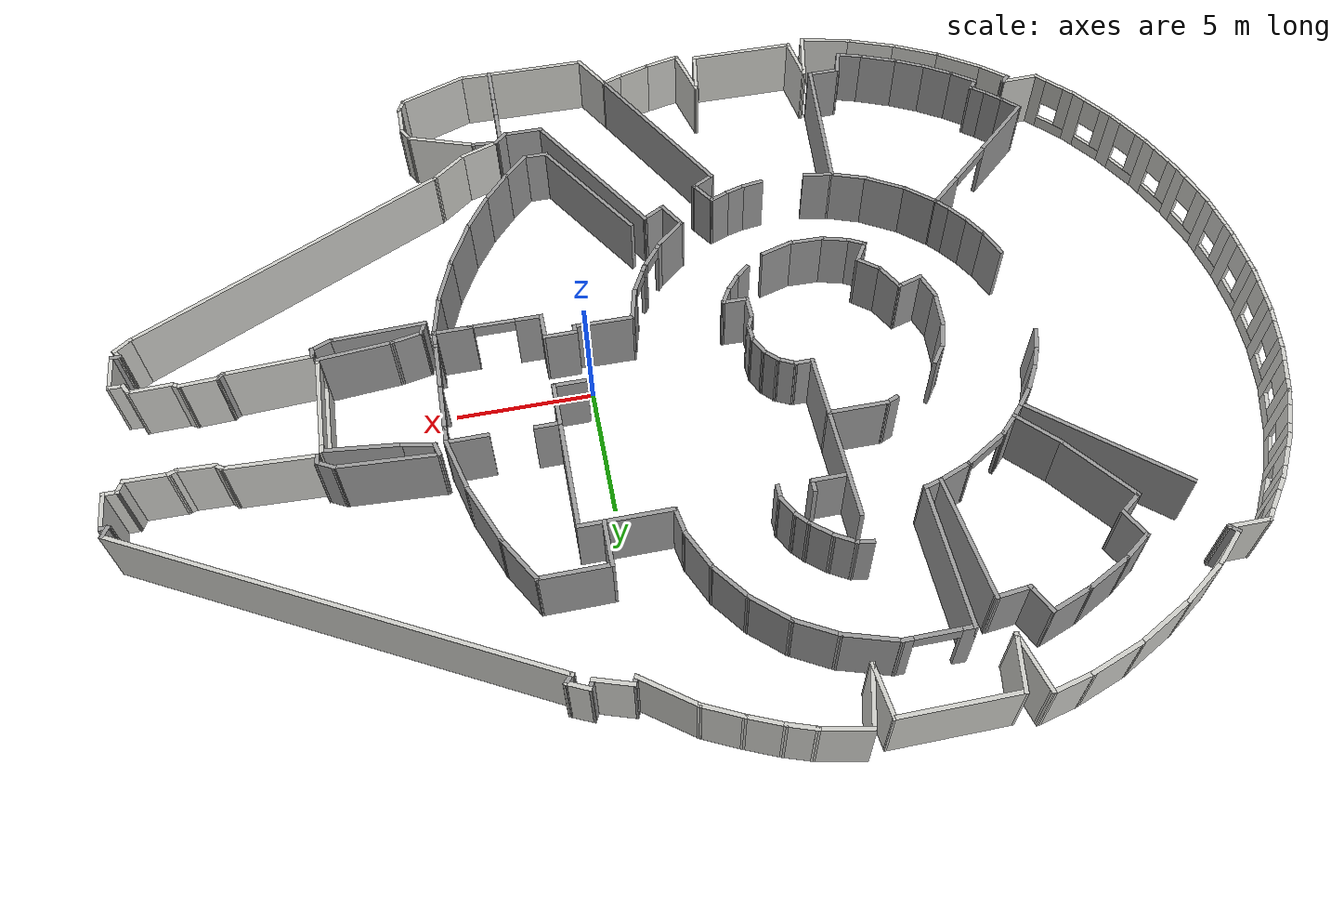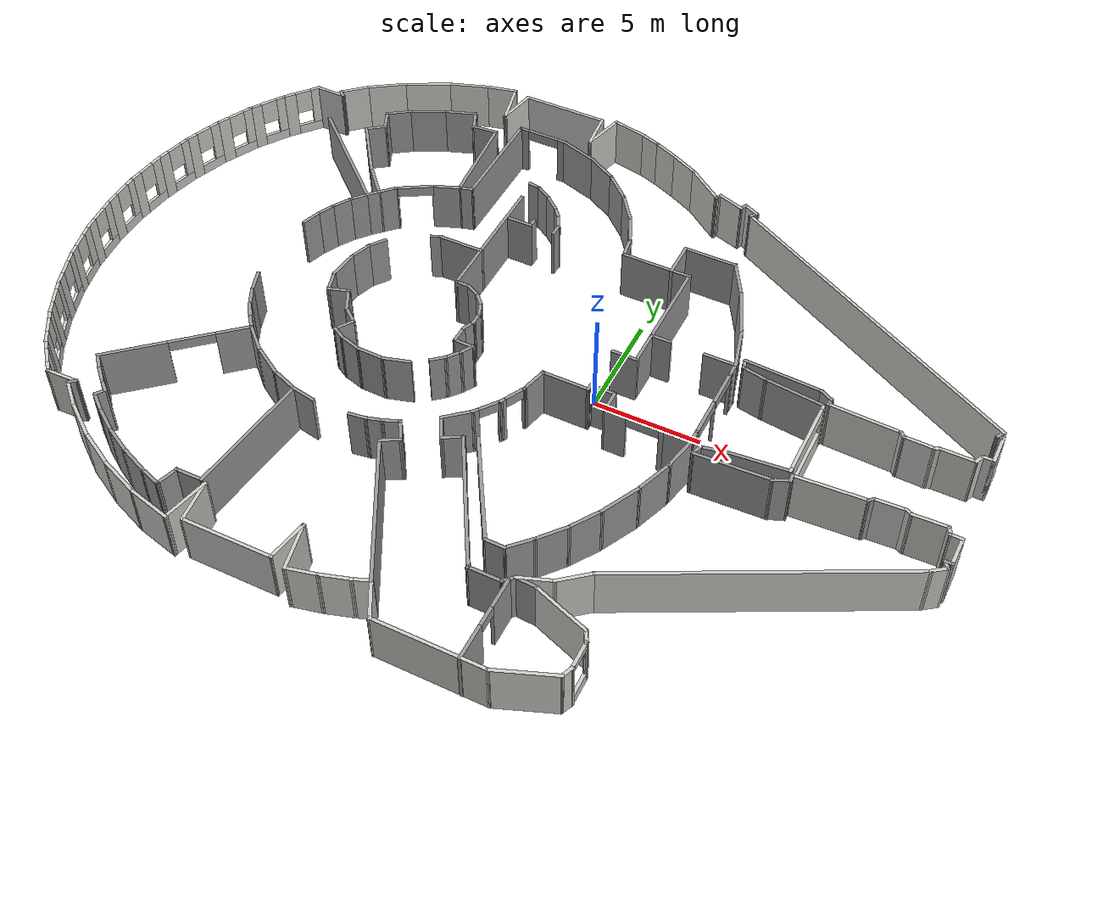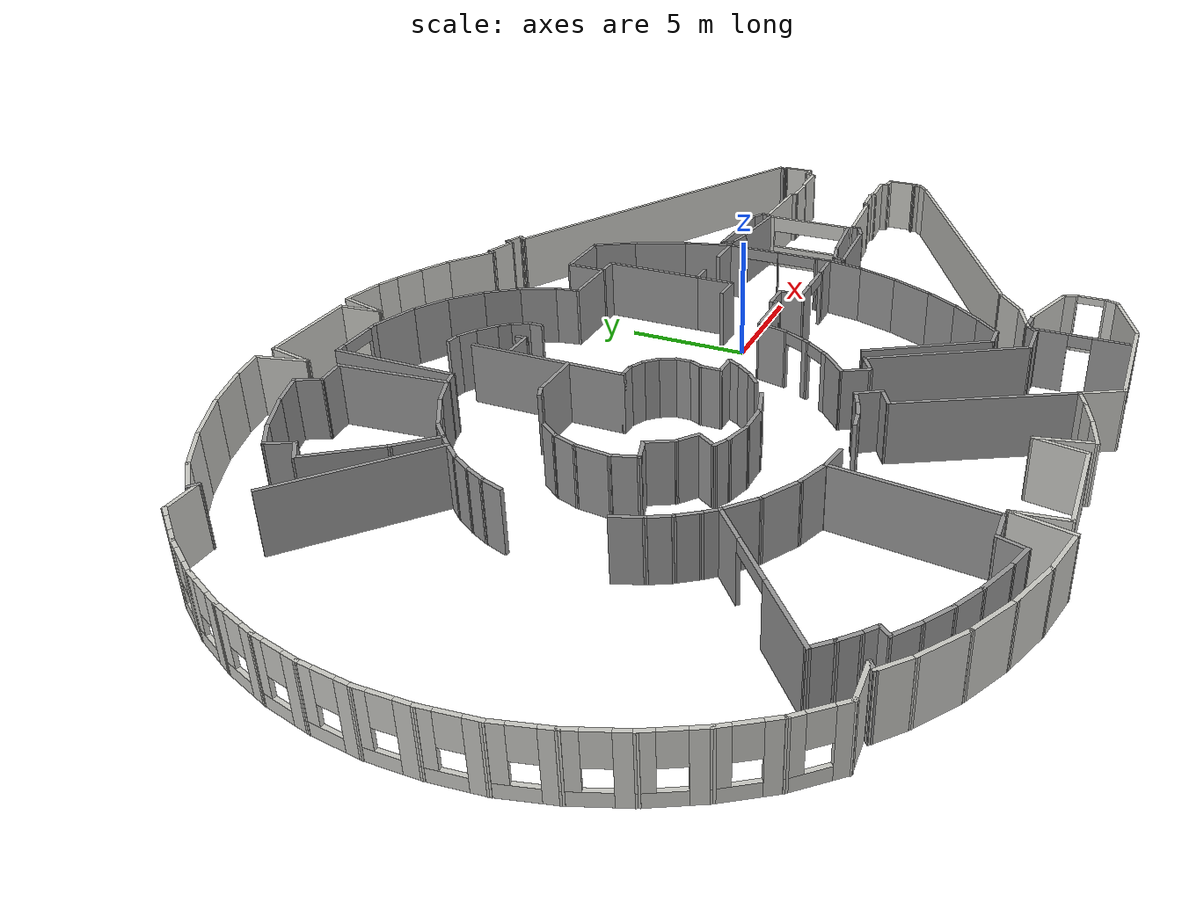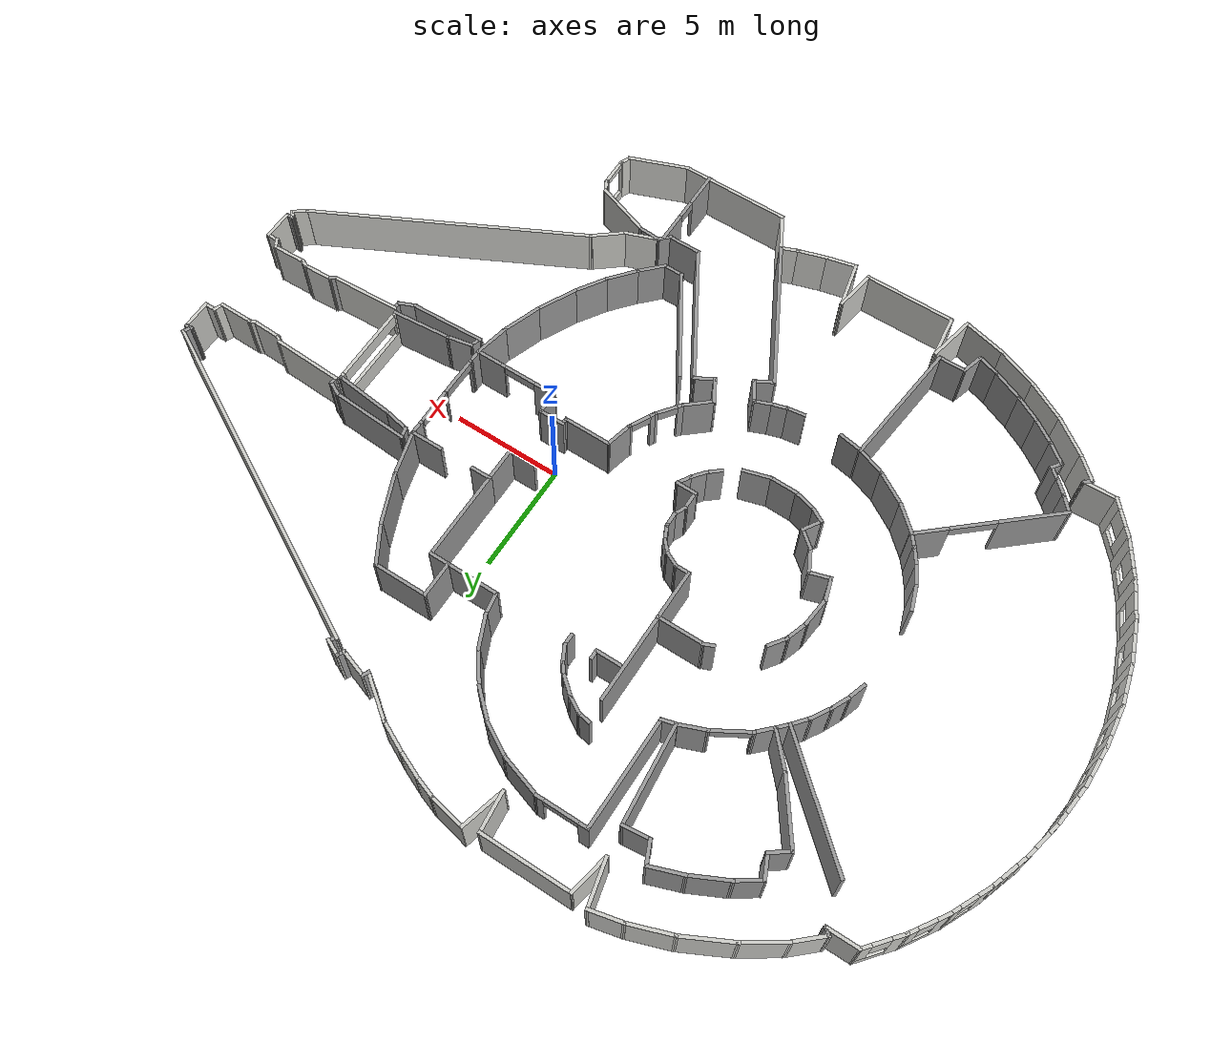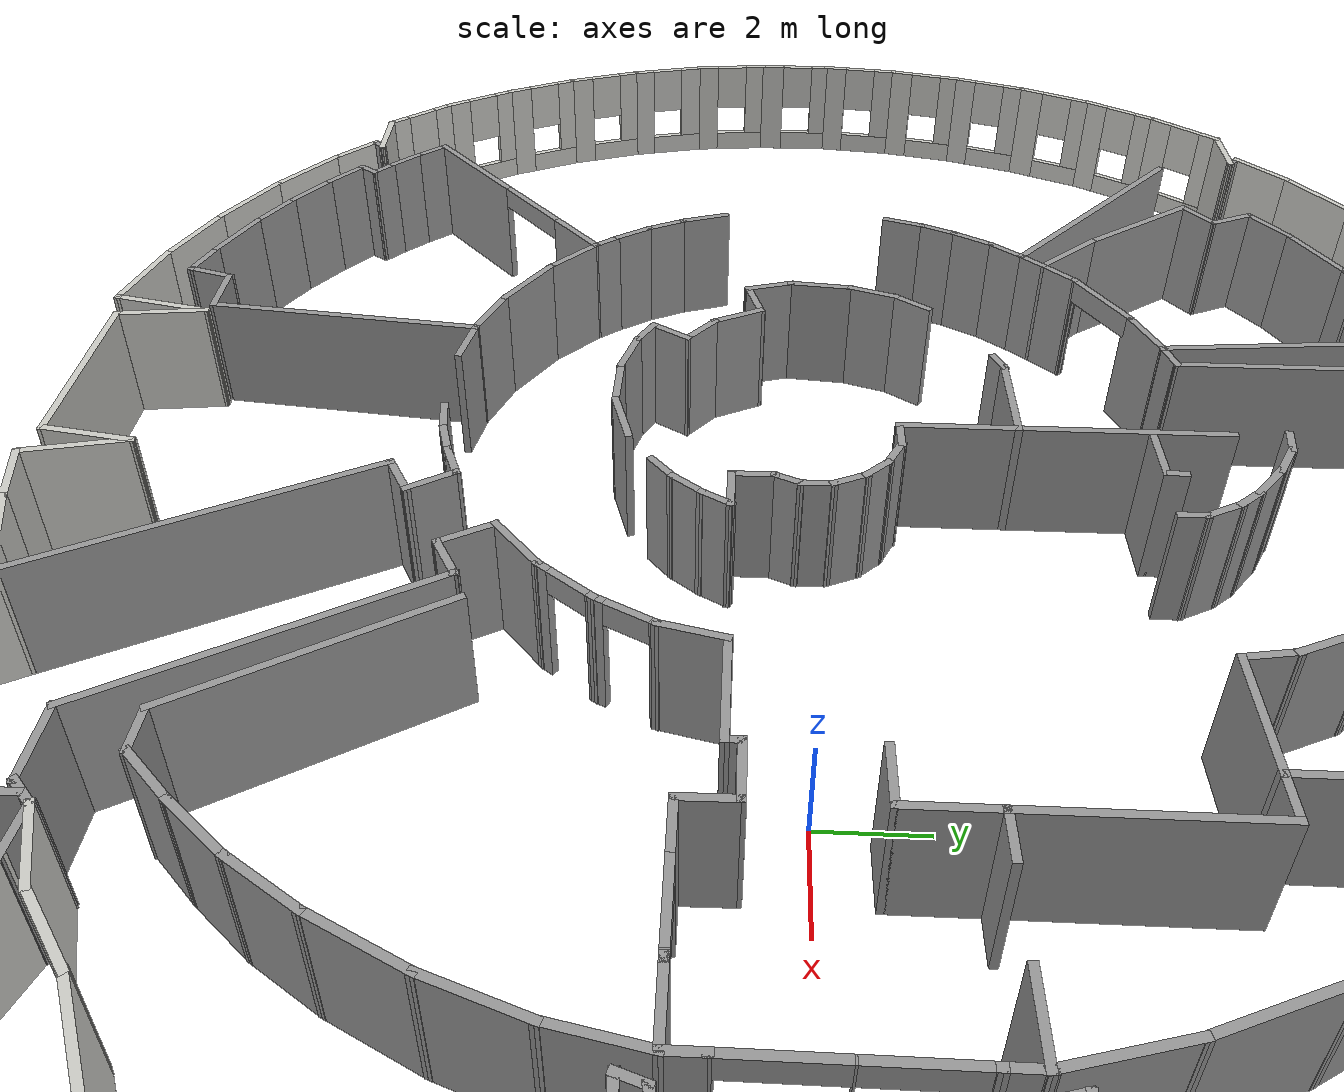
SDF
<?xml version='1.0'?>
<sdf version='1.7'>
  <model name='model'>
    <pose>-4.1341 -0.059214 0 0 -0 0</pose>
    <link name='Wall_10'>
      <collision name='Wall_10_Collision'>
        <geometry>
          <box>
            <size>1.42547 0.15 2.5</size>
          </box>
        </geometry>
        <pose>0 0 1.25 0 -0 0</pose>
      </collision>
      <visual name='Wall_10_Visual'>
        <pose>0 0 1.25 0 -0 0</pose>
        <geometry>
          <box>
            <size>1.42547 0.15 2.5</size>
          </box>
        </geometry>
        <material>
          <script>
            <uri>file://media/materials/scripts/gazebo.material</uri>
            <name>Gazebo/CeilingTiled</name>
          </script>
          <ambient>1 1 1 1</ambient>
        </material>
        <meta>
          <layer>0</layer>
        </meta>
      </visual>
      <pose>17.742 2.04987 0 0 -0 3.11021</pose>
    </link>
    <link name='Wall_101'>
      <collision name='Wall_101_Collision'>
        <geometry>
          <box>
            <size>0.462824 0.15 2.5</size>
          </box>
        </geometry>
        <pose>0 0 1.25 0 -0 0</pose>
      </collision>
      <visual name='Wall_101_Visual'>
        <pose>0 0 1.25 0 -0 0</pose>
        <geometry>
          <box>
            <size>0.462824 0.15 2.5</size>
          </box>
        </geometry>
        <material>
          <script>
            <uri>file://media/materials/scripts/gazebo.material</uri>
            <name>Gazebo/Grey</name>
          </script>
          <ambient>1 1 1 1</ambient>
        </material>
        <meta>
          <layer>0</layer>
        </meta>
      </visual>
      <pose>-15.2732 11.179 0 0 -0 2.42042</pose>
    </link>
    <link name='Wall_102'>
      <collision name='Wall_102_Collision'>
        <geometry>
          <box>
            <size>1.56641 0.15 2.5</size>
          </box>
        </geometry>
        <pose>0 0 1.25 0 -0 0</pose>
      </collision>
      <visual name='Wall_102_Visual'>
        <pose>0 0 1.25 0 -0 0</pose>
        <geometry>
          <box>
            <size>1.56641 0.15 2.5</size>
          </box>
        </geometry>
        <material>
          <script>
            <uri>file://media/materials/scripts/gazebo.material</uri>
            <name>Gazebo/CeilingTiled</name>
          </script>
          <ambient>0.964706 1 0.972549 1</ambient>
        </material>
        <meta>
          <layer>0</layer>
        </meta>
      </visual>
      <pose>-14.8674 11.7595 0 0 -0 0.739454</pose>
    </link>
    <link name='Wall_103'>
      <collision name='Wall_103_Collision'>
        <geometry>
          <box>
            <size>2.03182 0.15 2.5</size>
          </box>
        </geometry>
        <pose>0 0 1.25 0 -0 0</pose>
      </collision>
      <visual name='Wall_103_Visual'>
        <pose>0 0 1.25 0 -0 0</pose>
        <geometry>
          <box>
            <size>2.03182 0.15 2.5</size>
          </box>
        </geometry>
        <material>
          <script>
            <uri>file://media/materials/scripts/gazebo.material</uri>
            <name>Gazebo/CeilingTiled</name>
          </script>
          <ambient>0.964706 1 0.972549 1</ambient>
        </material>
        <meta>
          <layer>0</layer>
        </meta>
      </visual>
      <pose>-13.5621 12.76 0 0 -0 0.589698</pose>
    </link>
    <link name='Wall_104'>
      <collision name='Wall_104_Collision'>
        <geometry>
          <box>
            <size>2.39757 0.15 2.5</size>
          </box>
        </geometry>
        <pose>0 0 1.25 0 -0 0</pose>
      </collision>
      <visual name='Wall_104_Visual'>
        <pose>0 0 1.25 0 -0 0</pose>
        <geometry>
          <box>
            <size>2.39757 0.15 2.5</size>
          </box>
        </geometry>
        <material>
          <script>
            <uri>file://media/materials/scripts/gazebo.material</uri>
            <name>Gazebo/CeilingTiled</name>
          </script>
          <ambient>0.964706 1 0.972549 1</ambient>
        </material>
        <meta>
          <layer>0</layer>
        </meta>
      </visual>
      <pose>-11.7796 13.795 0 0 -0 0.472801</pose>
    </link>
    <link name='Wall_106'>
      <collision name='Wall_106_Collision'>
        <geometry>
          <box>
            <size>2.09081 0.15 2.5</size>
          </box>
        </geometry>
        <pose>0 0 1.25 0 -0 0</pose>
      </collision>
      <visual name='Wall_106_Visual'>
        <pose>0 0 1.25 0 -0 0</pose>
        <geometry>
          <box>
            <size>2.09081 0.15 2.5</size>
          </box>
        </geometry>
        <material>
          <script>
            <uri>file://media/materials/scripts/gazebo.material</uri>
            <name>Gazebo/CeilingTiled</name>
          </script>
          <ambient>0.964706 1 0.972549 1</ambient>
        </material>
        <meta>
          <layer>0</layer>
        </meta>
      </visual>
      <pose>-9.86354 14.6283 0 0 -0 0.337731</pose>
    </link>
    <link name='Wall_107'>
      <collision name='Wall_107_Collision'>
        <geometry>
          <box>
            <size>1.57879 0.15 2.5</size>
          </box>
        </geometry>
        <pose>0 0 1.25 0 -0 0</pose>
      </collision>
      <visual name='Wall_107_Visual'>
        <pose>0 0 1.25 0 -0 0</pose>
        <geometry>
          <box>
            <size>1.57879 0.15 2.5</size>
          </box>
        </geometry>
        <material>
          <script>
            <uri>file://media/materials/scripts/gazebo.material</uri>
            <name>Gazebo/CeilingTiled</name>
          </script>
          <ambient>0.964706 1 0.972549 1</ambient>
        </material>
        <meta>
          <layer>0</layer>
        </meta>
      </visual>
      <pose>-8.2523 15.1124 0 0 -0 0.229576</pose>
    </link>
    <link name='Wall_108'>
      <collision name='Wall_108_Collision'>
        <geometry>
          <box>
            <size>2.19881 0.15 2.5</size>
          </box>
        </geometry>
        <pose>0 0 1.25 0 -0 0</pose>
      </collision>
      <visual name='Wall_108_Visual'>
        <pose>0 0 1.25 0 -0 0</pose>
        <geometry>
          <box>
            <size>2.19881 0.15 2.5</size>
          </box>
        </geometry>
        <material>
          <script>
            <uri>file://media/materials/scripts/gazebo.material</uri>
            <name>Gazebo/CeilingTiled</name>
          </script>
          <ambient>0.964706 1 0.972549 1</ambient>
        </material>
        <meta>
          <layer>0</layer>
        </meta>
      </visual>
      <pose>-7.32602 14.2769 0 0 -0 -1.34372</pose>
    </link>
    <link name='Wall_109'>
      <collision name='Wall_109_Collision'>
        <geometry>
          <box>
            <size>1.99778 0.15 2.5</size>
          </box>
        </geometry>
        <pose>0 0 1.25 0 -0 0</pose>
      </collision>
      <visual name='Wall_109_Visual'>
        <pose>0 0 1.25 0 -0 0</pose>
        <geometry>
          <box>
            <size>1.99778 0.15 2.5</size>
          </box>
        </geometry>
        <material>
          <script>
            <uri>file://media/materials/scripts/gazebo.material</uri>
            <name>Gazebo/CeilingTiled</name>
          </script>
          <ambient>0.964706 1 0.972549 1</ambient>
        </material>
        <meta>
          <layer>0</layer>
        </meta>
      </visual>
      <pose>-6.92148 14.1861 0 0 -0 1.38143</pose>
    </link>
    <link name='Wall_11'>
      <collision name='Wall_11_Collision'>
        <geometry>
          <box>
            <size>0.422349 0.15 2.5</size>
          </box>
        </geometry>
        <pose>0 0 1.25 0 -0 0</pose>
      </collision>
      <visual name='Wall_11_Visual'>
        <pose>0 0 1.25 0 -0 0</pose>
        <geometry>
          <box>
            <size>0.422349 0.15 2.5</size>
          </box>
        </geometry>
        <material>
          <script>
            <uri>file://media/materials/scripts/gazebo.material</uri>
            <name>Gazebo/CeilingTiled</name>
          </script>
          <ambient>1 1 1 1</ambient>
        </material>
        <meta>
          <layer>0</layer>
        </meta>
      </visual>
      <pose>16.9987 2.15564 0 0 -0 2.46029</pose>
    </link>
    <link name='Wall_111'>
      <collision name='Wall_111_Collision'>
        <geometry>
          <box>
            <size>4.25 0.15 2.5</size>
          </box>
        </geometry>
        <pose>0 0 1.25 0 -0 0</pose>
      </collision>
      <visual name='Wall_111_Visual'>
        <pose>0 0 1.25 0 -0 0</pose>
        <geometry>
          <box>
            <size>4.25 0.15 2.5</size>
          </box>
        </geometry>
        <material>
          <script>
            <uri>file://media/materials/scripts/gazebo.material</uri>
            <name>Gazebo/CeilingTiled</name>
          </script>
          <ambient>0.964706 1 0.972549 1</ambient>
        </material>
        <meta>
          <layer>0</layer>
        </meta>
      </visual>
      <pose>-4.69757 15.0935 0 0 -0 0</pose>
    </link>
    <link name='Wall_112'>
      <collision name='Wall_112_Collision'>
        <geometry>
          <box>
            <size>1.93197 0.15 2.5</size>
          </box>
        </geometry>
        <pose>0 0 1.25 0 -0 0</pose>
      </collision>
      <visual name='Wall_112_Visual'>
        <pose>0 0 1.25 0 -0 0</pose>
        <geometry>
          <box>
            <size>1.93197 0.15 2.5</size>
          </box>
        </geometry>
        <material>
          <script>
            <uri>file://media/materials/scripts/gazebo.material</uri>
            <name>Gazebo/CeilingTiled</name>
          </script>
          <ambient>0.964706 1 0.972549 1</ambient>
        </material>
        <meta>
          <layer>0</layer>
        </meta>
      </visual>
      <pose>-2.56312 14.2065 0 0 -0 -1.47587</pose>
    </link>
    <link name='Wall_113'>
      <collision name='Wall_113_Collision'>
        <geometry>
          <box>
            <size>2.16942 0.15 2.5</size>
          </box>
        </geometry>
        <pose>0 0 1.25 0 -0 0</pose>
      </collision>
      <visual name='Wall_113_Visual'>
        <pose>0 0 1.25 0 -0 0</pose>
        <geometry>
          <box>
            <size>2.16942 0.15 2.5</size>
          </box>
        </geometry>
        <material>
          <script>
            <uri>file://media/materials/scripts/gazebo.material</uri>
            <name>Gazebo/CeilingTiled</name>
          </script>
          <ambient>0.964706 1 0.972549 1</ambient>
        </material>
        <meta>
          <layer>0</layer>
        </meta>
      </visual>
      <pose>-2.22567 14.2971 0 0 -0 1.31753</pose>
    </link>
    <link name='Wall_118'>
      <collision name='Wall_118_Collision'>
        <geometry>
          <box>
            <size>2.26593 0.15 2.5</size>
          </box>
        </geometry>
        <pose>0 0 1.25 0 -0 0</pose>
      </collision>
      <visual name='Wall_118_Visual'>
        <pose>0 0 1.25 0 -0 0</pose>
        <geometry>
          <box>
            <size>2.26593 0.15 2.5</size>
          </box>
        </geometry>
        <material>
          <script>
            <uri>file://media/materials/scripts/gazebo.material</uri>
            <name>Gazebo/CeilingTiled</name>
          </script>
          <ambient>0.964706 1 0.972549 1</ambient>
        </material>
        <meta>
          <layer>0</layer>
        </meta>
      </visual>
      <pose>3.7645 12.9158 0 0 -0 2.50012</pose>
    </link>
    <link name='Wall_119'>
      <collision name='Wall_119_Collision'>
        <geometry>
          <box>
            <size>1.52296 0.15 2.5</size>
          </box>
        </geometry>
        <pose>0 0 1.25 0 -0 0</pose>
      </collision>
      <visual name='Wall_119_Visual'>
        <pose>0 0 1.25 0 -0 0</pose>
        <geometry>
          <box>
            <size>1.52296 0.15 2.5</size>
          </box>
        </geometry>
        <material>
          <script>
            <uri>file://media/materials/scripts/gazebo.material</uri>
            <name>Gazebo/CeilingTiled</name>
          </script>
          <ambient>0.964706 1 0.972549 1</ambient>
        </material>
        <meta>
          <layer>0</layer>
        </meta>
      </visual>
      <pose>2.30059 13.8514 0 0 -0 2.68533</pose>
    </link>
    <link name='Wall_12'>
      <collision name='Wall_12_Collision'>
        <geometry>
          <box>
            <size>3.29739 0.15 2.5</size>
          </box>
        </geometry>
        <pose>0 0 1.25 0 -0 0</pose>
      </collision>
      <visual name='Wall_12_Visual'>
        <pose>0 0 1.25 0 -0 0</pose>
        <geometry>
          <box>
            <size>3.29739 0.15 2.5</size>
          </box>
        </geometry>
        <material>
          <script>
            <uri>file://media/materials/scripts/gazebo.material</uri>
            <name>Gazebo/CeilingTiled</name>
          </script>
          <ambient>0.964706 1 0.972549 1</ambient>
        </material>
        <meta>
          <layer>0</layer>
        </meta>
      </visual>
      <pose>15.3206 2.30716 0 0 -0 3.0998</pose>
    </link>
    <link name='Wall_120'>
      <collision name='Wall_120_Collision'>
        <geometry>
          <box>
            <size>1.38613 0.15 2.5</size>
          </box>
        </geometry>
        <pose>0 0 1.25 0 -0 0</pose>
      </collision>
      <visual name='Wall_120_Visual'>
        <pose>0 0 1.25 0 -0 0</pose>
        <geometry>
          <box>
            <size>1.38613 0.15 2.5</size>
          </box>
        </geometry>
        <material>
          <script>
            <uri>file://media/materials/scripts/gazebo.material</uri>
            <name>Gazebo/CeilingTiled</name>
          </script>
          <ambient>0.964706 1 0.972549 1</ambient>
        </material>
        <meta>
          <layer>0</layer>
        </meta>
      </visual>
      <pose>1.11722 14.3996 0 0 -0 2.73269</pose>
    </link>
    <link name='Wall_121'>
      <collision name='Wall_121_Collision'>
        <geometry>
          <box>
            <size>1.10172 0.15 2.5</size>
          </box>
        </geometry>
        <pose>0 0 1.25 0 -0 0</pose>
      </collision>
      <visual name='Wall_121_Visual'>
        <pose>0 0 1.25 0 -0 0</pose>
        <geometry>
          <box>
            <size>1.10172 0.15 2.5</size>
          </box>
        </geometry>
        <material>
          <script>
            <uri>file://media/materials/scripts/gazebo.material</uri>
            <name>Gazebo/CeilingTiled</name>
          </script>
          <ambient>0.964706 1 0.972549 1</ambient>
        </material>
        <meta>
          <layer>0</layer>
        </meta>
      </visual>
      <pose>0.100208 14.8003 0 0 -0 2.80979</pose>
    </link>
    <link name='Wall_122'>
      <collision name='Wall_122_Collision'>
        <geometry>
          <box>
            <size>1.79614 0.15 2.5</size>
          </box>
        </geometry>
        <pose>0 0 1.25 0 -0 0</pose>
      </collision>
      <visual name='Wall_122_Visual'>
        <pose>0 0 1.25 0 -0 0</pose>
        <geometry>
          <box>
            <size>1.79614 0.15 2.5</size>
          </box>
        </geometry>
        <material>
          <script>
            <uri>file://media/materials/scripts/gazebo.material</uri>
            <name>Gazebo/CeilingTiled</name>
          </script>
          <ambient>0.964706 1 0.972549 1</ambient>
        </material>
        <meta>
          <layer>0</layer>
        </meta>
      </visual>
      <pose>-1.15499 15.1255 0 0 -0 2.93339</pose>
    </link>
    <link name='Wall_124'>
      <collision name='Wall_124_Collision'>
        <geometry>
          <box>
            <size>0.404275 0.15 2.5</size>
          </box>
        </geometry>
        <pose>0 0 1.25 0 -0 0</pose>
      </collision>
      <visual name='Wall_124_Visual'>
        <pose>0 0 1.25 0 -0 0</pose>
        <geometry>
          <box>
            <size>0.404275 0.15 2.5</size>
          </box>
        </geometry>
        <material>
          <script>
            <uri>file://media/materials/scripts/gazebo.material</uri>
            <name>Gazebo/Grey</name>
          </script>
          <ambient>1 1 1 1</ambient>
        </material>
        <meta>
          <layer>0</layer>
        </meta>
      </visual>
      <pose>4.66935 12.3963 0 0 -0 1.10417</pose>
    </link>
    <link name='Wall_125'>
      <collision name='Wall_125_Collision'>
        <geometry>
          <box>
            <size>1.41013 0.15 2.5</size>
          </box>
        </geometry>
        <pose>0 0 1.25 0 -0 0</pose>
      </collision>
      <visual name='Wall_125_Visual'>
        <pose>0 0 1.25 0 -0 0</pose>
        <geometry>
          <box>
            <size>1.41013 0.15 2.5</size>
          </box>
        </geometry>
        <material>
          <script>
            <uri>file://media/materials/scripts/gazebo.material</uri>
            <name>Gazebo/CeilingTiled</name>
          </script>
          <ambient>0.964706 1 0.972549 1</ambient>
        </material>
        <meta>
          <layer>0</layer>
        </meta>
      </visual>
      <pose>5.3239 12.3095 0 0 -0 -0.323648</pose>
    </link>
    <link name='Wall_126'>
      <collision name='Wall_126_Collision'>
        <geometry>
          <box>
            <size>0.447598 0.15 2.5</size>
          </box>
        </geometry>
        <pose>0 0 1.25 0 -0 0</pose>
      </collision>
      <visual name='Wall_126_Visual'>
        <pose>0 0 1.25 0 -0 0</pose>
        <geometry>
          <box>
            <size>0.447598 0.15 2.5</size>
          </box>
        </geometry>
        <material>
          <script>
            <uri>file://media/materials/scripts/gazebo.material</uri>
            <name>Gazebo/Grey</name>
          </script>
          <ambient>1 1 1 1</ambient>
        </material>
        <meta>
          <layer>0</layer>
        </meta>
      </visual>
      <pose>5.98931 12.2414 0 0 -0 1.09579</pose>
    </link>
    <link name='Wall_127'>
      <collision name='Wall_127_Collision'>
        <geometry>
          <box>
            <size>0.894139 0.15 2.5</size>
          </box>
        </geometry>
        <pose>0 0 1.25 0 -0 0</pose>
      </collision>
      <visual name='Wall_127_Visual'>
        <pose>0 0 1.25 0 -0 0</pose>
        <geometry>
          <box>
            <size>0.894139 0.15 2.5</size>
          </box>
        </geometry>
        <material>
          <script>
            <uri>file://media/materials/scripts/gazebo.material</uri>
            <name>Gazebo/CeilingTiled</name>
          </script>
          <ambient>0.964706 1 0.972549 1</ambient>
        </material>
        <meta>
          <layer>0</layer>
        </meta>
      </visual>
      <pose>6.39384 12.215 0 0 -0 -0.440924</pose>
    </link>
    <link name='Wall_128'>
      <collision name='Wall_128_Collision'>
        <geometry>
          <box>
            <size>0.468928 0.15 2.5</size>
          </box>
        </geometry>
        <pose>0 0 1.25 0 -0 0</pose>
      </collision>
      <visual name='Wall_128_Visual'>
        <pose>0 0 1.25 0 -0 0</pose>
        <geometry>
          <box>
            <size>0.468928 0.15 2.5</size>
          </box>
        </geometry>
        <material>
          <script>
            <uri>file://media/materials/scripts/gazebo.material</uri>
            <name>Gazebo/Grey</name>
          </script>
          <ambient>1 1 1 1</ambient>
        </material>
        <meta>
          <layer>0</layer>
        </meta>
      </visual>
      <pose>6.62336 11.9379 0 0 -0 -2.30603</pose>
    </link>
    <link name='Wall_129'>
      <collision name='Wall_129_Collision'>
        <geometry>
          <box>
            <size>16.2931 0.15 2.5</size>
          </box>
        </geometry>
        <pose>0 0 1.25 0 -0 0</pose>
      </collision>
      <visual name='Wall_129_Visual'>
        <pose>0 0 1.25 0 -0 0</pose>
        <geometry>
          <box>
            <size>16.2931 0.15 2.5</size>
          </box>
        </geometry>
        <material>
          <script>
            <uri>file://media/materials/scripts/gazebo.material</uri>
            <name>Gazebo/CeilingTiled</name>
          </script>
          <ambient>0.964706 1 0.972549 1</ambient>
        </material>
        <meta>
          <layer>0</layer>
        </meta>
      </visual>
      <pose>13.6044 7.95817 0 0 -0 -0.498838</pose>
    </link>
    <link name='Wall_13'>
      <collision name='Wall_13_Collision'>
        <geometry>
          <box>
            <size>0.430684 0.15 2.5</size>
          </box>
        </geometry>
        <pose>0 0 1.25 0 -0 0</pose>
      </collision>
      <visual name='Wall_13_Visual'>
        <pose>0 0 1.25 0 -0 0</pose>
        <geometry>
          <box>
            <size>0.430684 0.15 2.5</size>
          </box>
        </geometry>
        <material>
          <script>
            <uri>file://media/materials/scripts/gazebo.material</uri>
            <name>Gazebo/Grey</name>
          </script>
          <ambient>1 1 1 1</ambient>
        </material>
        <meta>
          <layer>0</layer>
        </meta>
      </visual>
      <pose>13.7569 2.51299 0 0 -0 1.50965</pose>
    </link>
    <link name='Wall_135'>
      <collision name='Wall_135_Collision'>
        <geometry>
          <box>
            <size>6.29486 0.15 2.5</size>
          </box>
        </geometry>
        <pose>0 0 1.25 0 -0 0</pose>
      </collision>
      <visual name='Wall_135_Visual'>
        <pose>0 0 1.25 0 -0 0</pose>
        <geometry>
          <box>
            <size>6.29486 0.15 2.5</size>
          </box>
        </geometry>
        <material>
          <script>
            <uri>file://media/materials/scripts/gazebo.material</uri>
            <name>Gazebo/Grey</name>
          </script>
          <ambient>0.929412 0.960784 0.933333 1</ambient>
        </material>
        <meta>
          <layer>0</layer>
        </meta>
      </visual>
      <pose>-12.4823 7.17089 0 0 -0 -0.727536</pose>
    </link>
    <link name='Wall_136'>
      <collision name='Wall_136_Collision'>
        <geometry>
          <box>
            <size>0.730094 0.15 2.5</size>
          </box>
        </geometry>
        <pose>0 0 1.25 0 -0 0</pose>
      </collision>
      <visual name='Wall_136_Visual'>
        <pose>0 0 1.25 0 -0 0</pose>
        <geometry>
          <box>
            <size>0.730094 0.15 2.5</size>
          </box>
        </geometry>
        <material>
          <script>
            <uri>file://media/materials/scripts/gazebo.material</uri>
            <name>Gazebo/Grey</name>
          </script>
          <ambient>1 1 1 1</ambient>
        </material>
        <meta>
          <layer>0</layer>
        </meta>
      </visual>
      <pose>-9.98937 5.33923 0 0 -0 0.817645</pose>
    </link>
    <link name='Wall_139'>
      <collision name='Wall_139_Collision'>
        <geometry>
          <box>
            <size>0.967544 0.15 2.5</size>
          </box>
        </geometry>
        <pose>0 0 1.25 0 -0 0</pose>
      </collision>
      <visual name='Wall_139_Visual'>
        <pose>0 0 1.25 0 -0 0</pose>
        <geometry>
          <box>
            <size>0.967544 0.15 2.5</size>
          </box>
        </geometry>
        <material>
          <script>
            <uri>file://media/materials/scripts/gazebo.material</uri>
            <name>Gazebo/Grey</name>
          </script>
          <ambient>0.929412 0.960784 0.933333 1</ambient>
        </material>
        <meta>
          <layer>0</layer>
        </meta>
      </visual>
      <pose>-10.4508 4.81478 0 0 -0 -2.27001</pose>
    </link>
    <link name='Wall_140'>
      <collision name='Wall_140_Collision'>
        <geometry>
          <box>
            <size>1.07537 0.15 2.5</size>
          </box>
        </geometry>
        <pose>0 0 1.25 0 -0 0</pose>
      </collision>
      <visual name='Wall_140_Visual'>
        <pose>0 0 1.25 0 -0 0</pose>
        <geometry>
          <box>
            <size>1.07537 0.15 2.5</size>
          </box>
        </geometry>
        <material>
          <script>
            <uri>file://media/materials/scripts/gazebo.material</uri>
            <name>Gazebo/Grey</name>
          </script>
          <ambient>0.929412 0.960784 0.933333 1</ambient>
        </material>
        <meta>
          <layer>0</layer>
        </meta>
      </visual>
      <pose>-10.952 4.10518 0 0 -0 -2.11122</pose>
    </link>
    <link name='Wall_141'>
      <collision name='Wall_141_Collision'>
        <geometry>
          <box>
            <size>0.954554 0.15 2.5</size>
          </box>
        </geometry>
        <pose>0 0 1.25 0 -0 0</pose>
      </collision>
      <visual name='Wall_141_Visual'>
        <pose>0 0 1.25 0 -0 0</pose>
        <geometry>
          <box>
            <size>0.954554 0.15 2.5</size>
          </box>
        </geometry>
        <material>
          <script>
            <uri>file://media/materials/scripts/gazebo.material</uri>
            <name>Gazebo/Grey</name>
          </script>
          <ambient>0.929412 0.960784 0.933333 1</ambient>
        </material>
        <meta>
          <layer>0</layer>
        </meta>
      </visual>
      <pose>-11.362 3.34474 0 0 -0 -2.01239</pose>
    </link>
    <link name='Wall_142'>
      <collision name='Wall_142_Collision'>
        <geometry>
          <box>
            <size>0.998979 0.15 2.5</size>
          </box>
        </geometry>
        <pose>0 0 1.25 0 -0 0</pose>
      </collision>
      <visual name='Wall_142_Visual'>
        <pose>0 0 1.25 0 -0 0</pose>
        <geometry>
          <box>
            <size>0.998979 0.15 2.5</size>
          </box>
        </geometry>
        <material>
          <script>
            <uri>file://media/materials/scripts/gazebo.material</uri>
            <name>Gazebo/Grey</name>
          </script>
          <ambient>0.929412 0.960784 0.933333 1</ambient>
        </material>
        <meta>
          <layer>0</layer>
        </meta>
      </visual>
      <pose>-11.6661 2.57769 0 0 -0 -1.88762</pose>
    </link>
    <link name='Wall_144'>
      <collision name='Wall_144_Collision'>
        <geometry>
          <box>
            <size>1.19979 0.15 2.5</size>
          </box>
        </geometry>
        <pose>0 0 1.25 0 -0 0</pose>
      </collision>
      <visual name='Wall_144_Visual'>
        <pose>0 0 1.25 0 -0 0</pose>
        <geometry>
          <box>
            <size>1.19979 0.15 2.5</size>
          </box>
        </geometry>
        <material>
          <script>
            <uri>file://media/materials/scripts/gazebo.material</uri>
            <name>Gazebo/Grey</name>
          </script>
          <ambient>0.929412 0.960784 0.933333 1</ambient>
        </material>
        <meta>
          <layer>0</layer>
        </meta>
      </visual>
      <pose>-11.6485 -2.13121 0 0 -0 -1.23709</pose>
    </link>
    <link name='Wall_145'>
      <collision name='Wall_145_Collision'>
        <geometry>
          <box>
            <size>1.02535 0.15 2.5</size>
          </box>
        </geometry>
        <pose>0 0 1.25 0 -0 0</pose>
      </collision>
      <visual name='Wall_145_Visual'>
        <pose>0 0 1.25 0 -0 0</pose>
        <geometry>
          <box>
            <size>1.02535 0.15 2.5</size>
          </box>
        </geometry>
        <material>
          <script>
            <uri>file://media/materials/scripts/gazebo.material</uri>
            <name>Gazebo/Grey</name>
          </script>
          <ambient>0.929412 0.960784 0.933333 1</ambient>
        </material>
        <meta>
          <layer>0</layer>
        </meta>
      </visual>
      <pose>-11.2782 -3.01729 0 0 -0 -1.10039</pose>
    </link>
    <link name='Wall_146'>
      <collision name='Wall_146_Collision'>
        <geometry>
          <box>
            <size>0.997329 0.15 2.5</size>
          </box>
        </geometry>
        <pose>0 0 1.25 0 -0 0</pose>
      </collision>
      <visual name='Wall_146_Visual'>
        <pose>0 0 1.25 0 -0 0</pose>
        <geometry>
          <box>
            <size>0.997329 0.15 2.5</size>
          </box>
        </geometry>
        <material>
          <script>
            <uri>file://media/materials/scripts/gazebo.material</uri>
            <name>Gazebo/Grey</name>
          </script>
          <ambient>0.929412 0.960784 0.933333 1</ambient>
        </material>
        <meta>
          <layer>0</layer>
        </meta>
      </visual>
      <pose>-10.8418 -3.75789 0 0 -0 -0.974136</pose>
    </link>
    <link name='Wall_147'>
      <collision name='Wall_147_Collision'>
        <geometry>
          <box>
            <size>0.761361 0.15 2.5</size>
          </box>
        </geometry>
        <pose>0 0 1.25 0 -0 0</pose>
      </collision>
      <visual name='Wall_147_Visual'>
        <pose>0 0 1.25 0 -0 0</pose>
        <geometry>
          <box>
            <size>0.761361 0.15 2.5</size>
          </box>
        </geometry>
        <material>
          <script>
            <uri>file://media/materials/scripts/gazebo.material</uri>
            <name>Gazebo/Grey</name>
          </script>
          <ambient>0.929412 0.960784 0.933333 1</ambient>
        </material>
        <meta>
          <layer>0</layer>
        </meta>
      </visual>
      <pose>-10.4119 -4.3464 0 0 -0 -0.892677</pose>
    </link>
    <link name='Wall_149'>
      <pose>-12.6849 -6.76582 0 0 -0 -2.4171</pose>
      <visual name='Wall_149_Visual_0'>
        <pose>-2.54709 0 1.25 0 -0 0</pose>
        <geometry>
          <box>
            <size>1.63856 0.15 2.5</size>
          </box>
        </geometry>
        <material>
          <script>
            <uri>file://media/materials/scripts/gazebo.material</uri>
            <name>Gazebo/Grey</name>
          </script>
          <ambient>0.929412 0.960784 0.933333 1</ambient>
        </material>
        <meta>
          <layer>0</layer>
        </meta>
      </visual>
      <collision name='Wall_149_Collision_0'>
        <geometry>
          <box>
            <size>1.63856 0.15 2.5</size>
          </box>
        </geometry>
        <pose>-2.54709 0 1.25 0 -0 0</pose>
      </collision>
      <visual name='Wall_149_Visual_1'>
        <pose>1.84361 0 1.25 0 -0 0</pose>
        <geometry>
          <box>
            <size>3.04552 0.15 2.5</size>
          </box>
        </geometry>
        <material>
          <script>
            <uri>file://media/materials/scripts/gazebo.material</uri>
            <name>Gazebo/Grey</name>
          </script>
          <ambient>0.929412 0.960784 0.933333 1</ambient>
        </material>
        <meta>
          <layer>0</layer>
        </meta>
      </visual>
      <collision name='Wall_149_Collision_1'>
        <geometry>
          <box>
            <size>3.04552 0.15 2.5</size>
          </box>
        </geometry>
        <pose>1.84361 0 1.25 0 -0 0</pose>
      </collision>
      <visual name='Wall_149_Visual_2'>
        <pose>-0.703479 0 2.25 0 -0 0</pose>
        <geometry>
          <box>
            <size>2.04867 0.15 0.5</size>
          </box>
        </geometry>
        <material>
          <script>
            <uri>file://media/materials/scripts/gazebo.material</uri>
            <name>Gazebo/Grey</name>
          </script>
          <ambient>0.929412 0.960784 0.933333 1</ambient>
        </material>
        <meta>
          <layer>0</layer>
        </meta>
      </visual>
      <collision name='Wall_149_Collision_2'>
        <geometry>
          <box>
            <size>2.04867 0.15 0.5</size>
          </box>
        </geometry>
        <pose>-0.703479 0 2.25 0 -0 0</pose>
      </collision>
    </link>
    <link name='Wall_153'>
      <collision name='Wall_153_Collision'>
        <geometry>
          <box>
            <size>0.953287 0.15 2.5</size>
          </box>
        </geometry>
        <pose>0 0 1.25 0 -0 0</pose>
      </collision>
      <visual name='Wall_153_Visual'>
        <pose>0 0 1.25 0 -0 0</pose>
        <geometry>
          <box>
            <size>0.953287 0.15 2.5</size>
          </box>
        </geometry>
        <material>
          <script>
            <uri>file://media/materials/scripts/gazebo.material</uri>
            <name>Gazebo/Grey</name>
          </script>
          <ambient>1 1 1 1</ambient>
        </material>
        <meta>
          <layer>0</layer>
        </meta>
      </visual>
      <pose>-14.8797 -9.24465 0 0 -0 -0.833951</pose>
    </link>
    <link name='Wall_154'>
      <collision name='Wall_154_Collision'>
        <geometry>
          <box>
            <size>0.912545 0.15 2.5</size>
          </box>
        </geometry>
        <pose>0 0 1.25 0 -0 0</pose>
      </collision>
      <visual name='Wall_154_Visual'>
        <pose>0 0 1.25 0 -0 0</pose>
        <geometry>
          <box>
            <size>0.912545 0.15 2.5</size>
          </box>
        </geometry>
        <material>
          <script>
            <uri>file://media/materials/scripts/gazebo.material</uri>
            <name>Gazebo/Grey</name>
          </script>
          <ambient>1 1 1 1</ambient>
        </material>
        <meta>
          <layer>0</layer>
        </meta>
      </visual>
      <pose>-14.3359 -9.80732 0 0 -0 -0.769271</pose>
    </link>
    <link name='Wall_155'>
      <collision name='Wall_155_Collision'>
        <geometry>
          <box>
            <size>0.730072 0.15 2.5</size>
          </box>
        </geometry>
        <pose>0 0 1.25 0 -0 0</pose>
      </collision>
      <visual name='Wall_155_Visual'>
        <pose>0 0 1.25 0 -0 0</pose>
        <geometry>
          <box>
            <size>0.730072 0.15 2.5</size>
          </box>
        </geometry>
        <material>
          <script>
            <uri>file://media/materials/scripts/gazebo.material</uri>
            <name>Gazebo/Grey</name>
          </script>
          <ambient>1 1 1 1</ambient>
        </material>
        <meta>
          <layer>0</layer>
        </meta>
      </visual>
      <pose>-13.8402 -10.2595 0 0 -0 -0.700496</pose>
    </link>
    <link name='Wall_156'>
      <collision name='Wall_156_Collision'>
        <geometry>
          <box>
            <size>0.603926 0.15 2.5</size>
          </box>
        </geometry>
        <pose>0 0 1.25 0 -0 0</pose>
      </collision>
      <visual name='Wall_156_Visual'>
        <pose>0 0 1.25 0 -0 0</pose>
        <geometry>
          <box>
            <size>0.603926 0.15 2.5</size>
          </box>
        </geometry>
        <material>
          <script>
            <uri>file://media/materials/scripts/gazebo.material</uri>
            <name>Gazebo/Grey</name>
          </script>
          <ambient>1 1 1 1</ambient>
        </material>
        <meta>
          <layer>0</layer>
        </meta>
      </visual>
      <pose>-13.7533 -10.6291 0 0 -0 -2.20663</pose>
    </link>
    <link name='Wall_158'>
      <collision name='Wall_158_Collision'>
        <geometry>
          <box>
            <size>1.18744 0.15 2.5</size>
          </box>
        </geometry>
        <pose>0 0 1.25 0 -0 0</pose>
      </collision>
      <visual name='Wall_158_Visual'>
        <pose>0 0 1.25 0 -0 0</pose>
        <geometry>
          <box>
            <size>1.18744 0.15 2.5</size>
          </box>
        </geometry>
        <material>
          <script>
            <uri>file://media/materials/scripts/gazebo.material</uri>
            <name>Gazebo/Grey</name>
          </script>
          <ambient>1 1 1 1</ambient>
        </material>
        <meta>
          <layer>0</layer>
        </meta>
      </visual>
      <pose>-13.4803 -11.1323 0 0 -0 -0.666394</pose>
    </link>
    <link name='Wall_159'>
      <collision name='Wall_159_Collision'>
        <geometry>
          <box>
            <size>1.33983 0.15 2.5</size>
          </box>
        </geometry>
        <pose>0 0 1.25 0 -0 0</pose>
      </collision>
      <visual name='Wall_159_Visual'>
        <pose>0 0 1.25 0 -0 0</pose>
        <geometry>
          <box>
            <size>1.33983 0.15 2.5</size>
          </box>
        </geometry>
        <material>
          <script>
            <uri>file://media/materials/scripts/gazebo.material</uri>
            <name>Gazebo/Grey</name>
          </script>
          <ambient>1 1 1 1</ambient>
        </material>
        <meta>
          <layer>0</layer>
        </meta>
      </visual>
      <pose>-12.5776 -11.783 0 0 -0 -0.588003</pose>
    </link>
    <link name='Wall_16'>
      <collision name='Wall_16_Collision'>
        <geometry>
          <box>
            <size>0.771179 0.15 2.5</size>
          </box>
        </geometry>
        <pose>0 0 1.25 0 -0 0</pose>
      </collision>
      <visual name='Wall_16_Visual'>
        <pose>0 0 1.25 0 -0 0</pose>
        <geometry>
          <box>
            <size>0.771179 0.15 2.5</size>
          </box>
        </geometry>
        <material>
          <script>
            <uri>file://media/materials/scripts/gazebo.material</uri>
            <name>Gazebo/Grey</name>
          </script>
          <ambient>1 1 1 1</ambient>
        </material>
        <meta>
          <layer>0</layer>
        </meta>
      </visual>
      <pose>13.4901 2.7968 0 0 -0 2.6605</pose>
    </link>
    <link name='Wall_160'>
      <collision name='Wall_160_Collision'>
        <geometry>
          <box>
            <size>1.37119 0.15 2.5</size>
          </box>
        </geometry>
        <pose>0 0 1.25 0 -0 0</pose>
      </collision>
      <visual name='Wall_160_Visual'>
        <pose>0 0 1.25 0 -0 0</pose>
        <geometry>
          <box>
            <size>1.37119 0.15 2.5</size>
          </box>
        </geometry>
        <material>
          <script>
            <uri>file://media/materials/scripts/gazebo.material</uri>
            <name>Gazebo/Grey</name>
          </script>
          <ambient>1 1 1 1</ambient>
        </material>
        <meta>
          <layer>0</layer>
        </meta>
      </visual>
      <pose>-11.5426 -12.398 0 0 -0 -0.485622</pose>
    </link>
    <link name='Wall_161'>
      <collision name='Wall_161_Collision'>
        <geometry>
          <box>
            <size>1.62462 0.15 2.5</size>
          </box>
        </geometry>
        <pose>0 0 1.25 0 -0 0</pose>
      </collision>
      <visual name='Wall_161_Visual'>
        <pose>0 0 1.25 0 -0 0</pose>
        <geometry>
          <box>
            <size>1.62462 0.15 2.5</size>
          </box>
        </geometry>
        <material>
          <script>
            <uri>file://media/materials/scripts/gazebo.material</uri>
            <name>Gazebo/Grey</name>
          </script>
          <ambient>1 1 1 1</ambient>
        </material>
        <meta>
          <layer>0</layer>
        </meta>
      </visual>
      <pose>-10.3226 -12.968 0 0 -0 -0.396878</pose>
    </link>
    <link name='Wall_162'>
      <collision name='Wall_162_Collision'>
        <geometry>
          <box>
            <size>1.11768 0.15 2.5</size>
          </box>
        </geometry>
        <pose>0 0 1.25 0 -0 0</pose>
      </collision>
      <visual name='Wall_162_Visual'>
        <pose>0 0 1.25 0 -0 0</pose>
        <geometry>
          <box>
            <size>1.11768 0.15 2.5</size>
          </box>
        </geometry>
        <material>
          <script>
            <uri>file://media/materials/scripts/gazebo.material</uri>
            <name>Gazebo/Grey</name>
          </script>
          <ambient>1 1 1 1</ambient>
        </material>
        <meta>
          <layer>0</layer>
        </meta>
      </visual>
      <pose>-9.18259 -13.403 0 0 -0 -0.315215</pose>
    </link>
    <link name='Wall_163'>
      <collision name='Wall_163_Collision'>
        <geometry>
          <box>
            <size>1.12124 0.15 2.5</size>
          </box>
        </geometry>
        <pose>0 0 1.25 0 -0 0</pose>
      </collision>
      <visual name='Wall_163_Visual'>
        <pose>0 0 1.25 0 -0 0</pose>
        <geometry>
          <box>
            <size>1.12124 0.15 2.5</size>
          </box>
        </geometry>
        <material>
          <script>
            <uri>file://media/materials/scripts/gazebo.material</uri>
            <name>Gazebo/Grey</name>
          </script>
          <ambient>1 1 1 1</ambient>
        </material>
        <meta>
          <layer>0</layer>
        </meta>
      </visual>
      <pose>-8.58259 -13.088 0 0 -0 1.27835</pose>
    </link>
    <link name='Wall_164'>
      <collision name='Wall_164_Collision'>
        <geometry>
          <box>
            <size>1.33004 0.15 2.5</size>
          </box>
        </geometry>
        <pose>0 0 1.25 0 -0 0</pose>
      </collision>
      <visual name='Wall_164_Visual'>
        <pose>0 0 1.25 0 -0 0</pose>
        <geometry>
          <box>
            <size>1.33004 0.15 2.5</size>
          </box>
        </geometry>
        <material>
          <script>
            <uri>file://media/materials/scripts/gazebo.material</uri>
            <name>Gazebo/Grey</name>
          </script>
          <ambient>1 1 1 1</ambient>
        </material>
        <meta>
          <layer>0</layer>
        </meta>
      </visual>
      <pose>-7.85259 -12.618 0 0 -0 0.008474</pose>
    </link>
    <link name='Wall_166'>
      <collision name='Wall_166_Collision'>
        <geometry>
          <box>
            <size>5.98967 0.15 2.5</size>
          </box>
        </geometry>
        <pose>0 0 1.25 0 -0 0</pose>
      </collision>
      <visual name='Wall_166_Visual'>
        <pose>0 0 1.25 0 -0 0</pose>
        <geometry>
          <box>
            <size>5.98967 0.15 2.5</size>
          </box>
        </geometry>
        <material>
          <script>
            <uri>file://media/materials/scripts/gazebo.material</uri>
            <name>Gazebo/Grey</name>
          </script>
          <ambient>1 1 1 1</ambient>
        </material>
        <meta>
          <layer>0</layer>
        </meta>
      </visual>
      <pose>-6.94415 -9.71055 0 0 -0 1.46152</pose>
    </link>
    <link name='Wall_167'>
      <collision name='Wall_167_Collision'>
        <geometry>
          <box>
            <size>1.20017 0.15 2.5</size>
          </box>
        </geometry>
        <pose>0 0 1.25 0 -0 0</pose>
      </collision>
      <visual name='Wall_167_Visual'>
        <pose>0 0 1.25 0 -0 0</pose>
        <geometry>
          <box>
            <size>1.20017 0.15 2.5</size>
          </box>
        </geometry>
        <material>
          <script>
            <uri>file://media/materials/scripts/gazebo.material</uri>
            <name>Gazebo/Grey</name>
          </script>
          <ambient>1 1 1 1</ambient>
        </material>
        <meta>
          <layer>0</layer>
        </meta>
      </visual>
      <pose>-6.10861 -6.89938 0 0 -0 -0.174672</pose>
    </link>
    <link name='Wall_169'>
      <collision name='Wall_169_Collision'>
        <geometry>
          <box>
            <size>1.45339 0.15 2.5</size>
          </box>
        </geometry>
        <pose>0 0 1.25 0 -0 0</pose>
      </collision>
      <visual name='Wall_169_Visual'>
        <pose>0 0 1.25 0 -0 0</pose>
        <geometry>
          <box>
            <size>1.45339 0.15 2.5</size>
          </box>
        </geometry>
        <material>
          <script>
            <uri>file://media/materials/scripts/gazebo.material</uri>
            <name>Gazebo/Grey</name>
          </script>
          <ambient>1 1 1 1</ambient>
        </material>
        <meta>
          <layer>0</layer>
        </meta>
      </visual>
      <pose>-7.23666 -6.58131 0 0 -0 2.7861</pose>
    </link>
    <link name='Wall_17'>
      <collision name='Wall_17_Collision'>
        <geometry>
          <box>
            <size>3.65354 0.15 2.5</size>
          </box>
        </geometry>
        <pose>0 0 1.25 0 -0 0</pose>
      </collision>
      <visual name='Wall_17_Visual'>
        <pose>0 0 1.25 0 -0 0</pose>
        <geometry>
          <box>
            <size>3.65354 0.15 2.5</size>
          </box>
        </geometry>
        <material>
          <script>
            <uri>file://media/materials/scripts/gazebo.material</uri>
            <name>Gazebo/Grey</name>
          </script>
          <ambient>1 1 1 1</ambient>
        </material>
        <meta>
          <layer>0</layer>
        </meta>
      </visual>
      <pose>11.4658 3.03915 0 0 -0 3.08526</pose>
    </link>
    <link name='Wall_170'>
      <collision name='Wall_170_Collision'>
        <geometry>
          <box>
            <size>1.74678 0.15 2.5</size>
          </box>
        </geometry>
        <pose>0 0 1.25 0 -0 0</pose>
      </collision>
      <visual name='Wall_170_Visual'>
        <pose>0 0 1.25 0 -0 0</pose>
        <geometry>
          <box>
            <size>1.74678 0.15 2.5</size>
          </box>
        </geometry>
        <material>
          <script>
            <uri>file://media/materials/scripts/gazebo.material</uri>
            <name>Gazebo/Grey</name>
          </script>
          <ambient>1 1 1 1</ambient>
        </material>
        <meta>
          <layer>0</layer>
        </meta>
      </visual>
      <pose>-8.52869 -5.93789 0 0 -0 2.59265</pose>
    </link>
    <link name='Wall_171'>
      <collision name='Wall_171_Collision'>
        <geometry>
          <box>
            <size>1.49778 0.15 2.5</size>
          </box>
        </geometry>
        <pose>0 0 1.25 0 -0 0</pose>
      </collision>
      <visual name='Wall_171_Visual'>
        <pose>0 0 1.25 0 -0 0</pose>
        <geometry>
          <box>
            <size>1.49778 0.15 2.5</size>
          </box>
        </geometry>
        <material>
          <script>
            <uri>file://media/materials/scripts/gazebo.material</uri>
            <name>Gazebo/Grey</name>
          </script>
          <ambient>1 1 1 1</ambient>
        </material>
        <meta>
          <layer>0</layer>
        </meta>
      </visual>
      <pose>-9.70572 -5.06504 0 0 -0 2.39784</pose>
    </link>
    <link name='Wall_173'>
      <collision name='Wall_173_Collision'>
        <geometry>
          <box>
            <size>0.887742 0.15 2.5</size>
          </box>
        </geometry>
        <pose>0 0 1.25 0 -0 0</pose>
      </collision>
      <visual name='Wall_173_Visual'>
        <pose>0 0 1.25 0 -0 0</pose>
        <geometry>
          <box>
            <size>0.887742 0.15 2.5</size>
          </box>
        </geometry>
        <material>
          <script>
            <uri>file://media/materials/scripts/gazebo.material</uri>
            <name>Gazebo/Grey</name>
          </script>
          <ambient>1 1 1 1</ambient>
        </material>
        <meta>
          <layer>0</layer>
        </meta>
      </visual>
      <pose>-3.43446 -6.9344 0 0 -0 0.144812</pose>
    </link>
    <link name='Wall_174'>
      <collision name='Wall_174_Collision'>
        <geometry>
          <box>
            <size>0.847782 0.15 2.5</size>
          </box>
        </geometry>
        <pose>0 0 1.25 0 -0 0</pose>
      </collision>
      <visual name='Wall_174_Visual'>
        <pose>0 0 1.25 0 -0 0</pose>
        <geometry>
          <box>
            <size>0.847782 0.15 2.5</size>
          </box>
        </geometry>
        <material>
          <script>
            <uri>file://media/materials/scripts/gazebo.material</uri>
            <name>Gazebo/Grey</name>
          </script>
          <ambient>1 1 1 1</ambient>
        </material>
        <meta>
          <layer>0</layer>
        </meta>
      </visual>
      <pose>-2.73486 -6.78231 0 0 -0 0.287281</pose>
    </link>
    <link name='Wall_175'>
      <collision name='Wall_175_Collision'>
        <geometry>
          <box>
            <size>0.887115 0.15 2.5</size>
          </box>
        </geometry>
        <pose>0 0 1.25 0 -0 0</pose>
      </collision>
      <visual name='Wall_175_Visual'>
        <pose>0 0 1.25 0 -0 0</pose>
        <geometry>
          <box>
            <size>0.887115 0.15 2.5</size>
          </box>
        </geometry>
        <material>
          <script>
            <uri>file://media/materials/scripts/gazebo.material</uri>
            <name>Gazebo/Grey</name>
          </script>
          <ambient>1 1 1 1</ambient>
        </material>
        <meta>
          <layer>0</layer>
        </meta>
      </visual>
      <pose>-2.05807 -6.54657 0 0 -0 0.380506</pose>
    </link>
    <link name='Wall_176'>
      <collision name='Wall_176_Collision'>
        <geometry>
          <box>
            <size>1.13341 0.15 2.5</size>
          </box>
        </geometry>
        <pose>0 0 1.25 0 -0 0</pose>
      </collision>
      <visual name='Wall_176_Visual'>
        <pose>0 0 1.25 0 -0 0</pose>
        <geometry>
          <box>
            <size>1.13341 0.15 2.5</size>
          </box>
        </geometry>
        <material>
          <script>
            <uri>file://media/materials/scripts/gazebo.material</uri>
            <name>Gazebo/Grey</name>
          </script>
          <ambient>1 1 1 1</ambient>
        </material>
        <meta>
          <layer>0</layer>
        </meta>
      </visual>
      <pose>-1.45732 -6.82794 0 0 -0 -1.01711</pose>
    </link>
    <link name='Wall_177'>
      <collision name='Wall_177_Collision'>
        <geometry>
          <box>
            <size>1.02156 0.15 2.5</size>
          </box>
        </geometry>
        <pose>0 0 1.25 0 -0 0</pose>
      </collision>
      <visual name='Wall_177_Visual'>
        <pose>0 0 1.25 0 -0 0</pose>
        <geometry>
          <box>
            <size>1.02156 0.15 2.5</size>
          </box>
        </geometry>
        <material>
          <script>
            <uri>file://media/materials/scripts/gazebo.material</uri>
            <name>Gazebo/Grey</name>
          </script>
          <ambient>1 1 1 1</ambient>
        </material>
        <meta>
          <layer>0</layer>
        </meta>
      </visual>
      <pose>-1.57899 -7.4591 0 0 -0 -2.6311</pose>
    </link>
    <link name='Wall_18'>
      <collision name='Wall_18_Collision'>
        <geometry>
          <box>
            <size>0.585403 0.15 2.5</size>
          </box>
        </geometry>
        <pose>0 0 1.25 0 -0 0</pose>
      </collision>
      <visual name='Wall_18_Visual'>
        <pose>0 0 1.25 0 -0 0</pose>
        <geometry>
          <box>
            <size>0.585403 0.15 2.5</size>
          </box>
        </geometry>
        <material>
          <script>
            <uri>file://media/materials/scripts/gazebo.material</uri>
            <name>Gazebo/Grey</name>
          </script>
          <ambient>1 1 1 1</ambient>
        </material>
        <meta>
          <layer>0</layer>
        </meta>
      </visual>
      <pose>9.77269 2.92737 0 0 -0 -1.31117</pose>
    </link>
    <link name='Wall_180'>
      <collision name='Wall_180_Collision'>
        <geometry>
          <box>
            <size>7.09459 0.15 2.5</size>
          </box>
        </geometry>
        <pose>0 0 1.25 0 -0 0</pose>
      </collision>
      <visual name='Wall_180_Visual'>
        <pose>0 0 1.25 0 -0 0</pose>
        <geometry>
          <box>
            <size>7.09459 0.15 2.5</size>
          </box>
        </geometry>
        <material>
          <script>
            <uri>file://media/materials/scripts/gazebo.material</uri>
            <name>Gazebo/Grey</name>
          </script>
          <ambient>1 1 1 1</ambient>
        </material>
        <meta>
          <layer>0</layer>
        </meta>
      </visual>
      <pose>-0.326679 -10.7366 0 0 -0 -1.08132</pose>
    </link>
    <link name='Wall_182'>
      <collision name='Wall_182_Collision'>
        <geometry>
          <box>
            <size>1.35009 0.15 2.5</size>
          </box>
        </geometry>
        <pose>0 0 1.25 0 -0 0</pose>
      </collision>
      <visual name='Wall_182_Visual'>
        <pose>0 0 1.25 0 -0 0</pose>
        <geometry>
          <box>
            <size>1.35009 0.15 2.5</size>
          </box>
        </geometry>
        <material>
          <script>
            <uri>file://media/materials/scripts/gazebo.material</uri>
            <name>Gazebo/Grey</name>
          </script>
          <ambient>1 1 1 1</ambient>
        </material>
        <meta>
          <layer>0</layer>
        </meta>
      </visual>
      <pose>2.18096 -1.91168 0 0 -0 -1.80764</pose>
    </link>
    <link name='Wall_183'>
      <pose>1.75857 -3.03804 0 0 -0 -2.04915</pose>
      <visual name='Wall_183_Visual_0'>
        <pose>-0.599077 0 1.25 0 -0 0</pose>
        <geometry>
          <box>
            <size>0.175306 0.15 2.5</size>
          </box>
        </geometry>
        <material>
          <script>
            <uri>file://media/materials/scripts/gazebo.material</uri>
            <name>Gazebo/Grey</name>
          </script>
          <ambient>1 1 1 1</ambient>
        </material>
        <meta>
          <layer>0</layer>
        </meta>
      </visual>
      <collision name='Wall_183_Collision_0'>
        <geometry>
          <box>
            <size>0.175306 0.15 2.5</size>
          </box>
        </geometry>
        <pose>-0.599077 0 1.25 0 -0 0</pose>
      </collision>
      <visual name='Wall_183_Visual_1'>
        <pose>0.537653 0 1.25 0 -0 0</pose>
        <geometry>
          <box>
            <size>0.298155 0.15 2.5</size>
          </box>
        </geometry>
        <material>
          <script>
            <uri>file://media/materials/scripts/gazebo.material</uri>
            <name>Gazebo/Grey</name>
          </script>
          <ambient>1 1 1 1</ambient>
        </material>
        <meta>
          <layer>0</layer>
        </meta>
      </visual>
      <collision name='Wall_183_Collision_1'>
        <geometry>
          <box>
            <size>0.298155 0.15 2.5</size>
          </box>
        </geometry>
        <pose>0.537653 0 1.25 0 -0 0</pose>
      </collision>
      <visual name='Wall_183_Visual_2'>
        <pose>-0.061425 0 2.25 0 -0 0</pose>
        <geometry>
          <box>
            <size>0.9 0.15 0.5</size>
          </box>
        </geometry>
        <material>
          <script>
            <uri>file://media/materials/scripts/gazebo.material</uri>
            <name>Gazebo/Grey</name>
          </script>
          <ambient>1 1 1 1</ambient>
        </material>
        <meta>
          <layer>0</layer>
        </meta>
      </visual>
      <collision name='Wall_183_Collision_2'>
        <geometry>
          <box>
            <size>0.9 0.15 0.5</size>
          </box>
        </geometry>
        <pose>-0.061425 0 2.25 0 -0 0</pose>
      </collision>
    </link>
    <link name='Wall_184'>
      <pose>1.08477 -4.094 0 0 -0 -2.22364</pose>
      <visual name='Wall_184_Visual_0'>
        <pose>-0.623774 0 1.25 0 -0 0</pose>
        <geometry>
          <box>
            <size>0.193801 0.15 2.5</size>
          </box>
        </geometry>
        <material>
          <script>
            <uri>file://media/materials/scripts/gazebo.material</uri>
            <name>Gazebo/Grey</name>
          </script>
          <ambient>1 1 1 1</ambient>
        </material>
        <meta>
          <layer>0</layer>
        </meta>
      </visual>
      <collision name='Wall_184_Collision_0'>
        <geometry>
          <box>
            <size>0.193801 0.15 2.5</size>
          </box>
        </geometry>
        <pose>-0.623774 0 1.25 0 -0 0</pose>
      </collision>
      <visual name='Wall_184_Visual_1'>
        <pose>0.5469 0 1.25 0 -0 0</pose>
        <geometry>
          <box>
            <size>0.347547 0.15 2.5</size>
          </box>
        </geometry>
        <material>
          <script>
            <uri>file://media/materials/scripts/gazebo.material</uri>
            <name>Gazebo/Grey</name>
          </script>
          <ambient>1 1 1 1</ambient>
        </material>
        <meta>
          <layer>0</layer>
        </meta>
      </visual>
      <collision name='Wall_184_Collision_1'>
        <geometry>
          <box>
            <size>0.347547 0.15 2.5</size>
          </box>
        </geometry>
        <pose>0.5469 0 1.25 0 -0 0</pose>
      </collision>
      <visual name='Wall_184_Visual_2'>
        <pose>-0.076873 0 2.25 0 -0 0</pose>
        <geometry>
          <box>
            <size>0.9 0.15 0.5</size>
          </box>
        </geometry>
        <material>
          <script>
            <uri>file://media/materials/scripts/gazebo.material</uri>
            <name>Gazebo/Grey</name>
          </script>
          <ambient>1 1 1 1</ambient>
        </material>
        <meta>
          <layer>0</layer>
        </meta>
      </visual>
      <collision name='Wall_184_Collision_2'>
        <geometry>
          <box>
            <size>0.9 0.15 0.5</size>
          </box>
        </geometry>
        <pose>-0.076873 0 2.25 0 -0 0</pose>
      </collision>
    </link>
    <link name='Wall_185'>
      <collision name='Wall_185_Collision'>
        <geometry>
          <box>
            <size>1.4602 0.15 2.5</size>
          </box>
        </geometry>
        <pose>0 0 1.25 0 -0 0</pose>
      </collision>
      <visual name='Wall_185_Visual'>
        <pose>0 0 1.25 0 -0 0</pose>
        <geometry>
          <box>
            <size>1.4602 0.15 2.5</size>
          </box>
        </geometry>
        <material>
          <script>
            <uri>file://media/materials/scripts/gazebo.material</uri>
            <name>Gazebo/Grey</name>
          </script>
          <ambient>1 1 1 1</ambient>
        </material>
        <meta>
          <layer>0</layer>
        </meta>
      </visual>
      <pose>0.196945 -5.0353 0 0 -0 -2.4288</pose>
    </link>
    <link name='Wall_187'>
      <collision name='Wall_187_Collision'>
        <geometry>
          <box>
            <size>1.24375 0.15 2.5</size>
          </box>
        </geometry>
        <pose>0 0 1.25 0 -0 0</pose>
      </collision>
      <visual name='Wall_187_Visual'>
        <pose>0 0 1.25 0 -0 0</pose>
        <geometry>
          <box>
            <size>1.24375 0.15 2.5</size>
          </box>
        </geometry>
        <material>
          <script>
            <uri>file://media/materials/scripts/gazebo.material</uri>
            <name>Gazebo/Grey</name>
          </script>
          <ambient>1 1 1 1</ambient>
        </material>
        <meta>
          <layer>0</layer>
        </meta>
      </visual>
      <pose>-0.033447 -5.94196 0 0 -0 -1.06447</pose>
    </link>
    <link name='Wall_19'>
      <collision name='Wall_19_Collision'>
        <geometry>
          <box>
            <size>1.25295 0.15 2.5</size>
          </box>
        </geometry>
        <pose>0 0 1.25 0 -0 0</pose>
      </collision>
      <visual name='Wall_19_Visual'>
        <pose>0 0 1.25 0 -0 0</pose>
        <geometry>
          <box>
            <size>1.25295 0.15 2.5</size>
          </box>
        </geometry>
        <material>
          <script>
            <uri>file://media/materials/scripts/gazebo.material</uri>
            <name>Gazebo/Grey</name>
          </script>
          <ambient>1 1 1 1</ambient>
        </material>
        <meta>
          <layer>0</layer>
        </meta>
      </visual>
      <pose>10.3696 2.61005 0 0 -0 -0.195106</pose>
    </link>
    <link name='Wall_190'>
      <collision name='Wall_190_Collision'>
        <geometry>
          <box>
            <size>0.15 0.15 2.5</size>
          </box>
        </geometry>
        <pose>0 0 1.25 0 -0 0</pose>
      </collision>
      <visual name='Wall_190_Visual'>
        <pose>0 0 1.25 0 -0 0</pose>
        <geometry>
          <box>
            <size>0.15 0.15 2.5</size>
          </box>
        </geometry>
        <material>
          <script>
            <uri>file://media/materials/scripts/gazebo.material</uri>
            <name>Gazebo/Grey</name>
          </script>
          <ambient>1 1 1 1</ambient>
        </material>
        <meta>
          <layer>0</layer>
        </meta>
      </visual>
      <pose>1.00568 -5.98544 0 0 -0 0</pose>
    </link>
    <link name='Wall_192'>
      <collision name='Wall_192_Collision'>
        <geometry>
          <box>
            <size>0.15 0.15 2.5</size>
          </box>
        </geometry>
        <pose>0 0 1.25 0 -0 0</pose>
      </collision>
      <visual name='Wall_192_Visual'>
        <pose>0 0 1.25 0 -0 0</pose>
        <geometry>
          <box>
            <size>0.15 0.15 2.5</size>
          </box>
        </geometry>
        <material>
          <script>
            <uri>file://media/materials/scripts/gazebo.material</uri>
            <name>Gazebo/Grey</name>
          </script>
          <ambient>0 0 0 1</ambient>
        </material>
        <meta>
          <layer>0</layer>
        </meta>
      </visual>
      <pose>1.00568 -5.98544 0 0 -0 0</pose>
    </link>
    <link name='Wall_193'>
      <collision name='Wall_193_Collision'>
        <geometry>
          <box>
            <size>1.03768 0.15 2.5</size>
          </box>
        </geometry>
        <pose>0 0 1.25 0 -0 0</pose>
      </collision>
      <visual name='Wall_193_Visual'>
        <pose>0 0 1.25 0 -0 0</pose>
        <geometry>
          <box>
            <size>1.03768 0.15 2.5</size>
          </box>
        </geometry>
        <material>
          <script>
            <uri>file://media/materials/scripts/gazebo.material</uri>
            <name>Gazebo/Grey</name>
          </script>
          <ambient>1 1 1 1</ambient>
        </material>
        <meta>
          <layer>0</layer>
        </meta>
      </visual>
      <pose>0.618727 -6.20283 0 0 -0 0.511856</pose>
    </link>
    <link name='Wall_196'>
      <collision name='Wall_196_Collision'>
        <geometry>
          <box>
            <size>6.65835 0.15 2.5</size>
          </box>
        </geometry>
        <pose>0 0 1.25 0 -0 0</pose>
      </collision>
      <visual name='Wall_196_Visual'>
        <pose>0 0 1.25 0 -0 0</pose>
        <geometry>
          <box>
            <size>6.65835 0.15 2.5</size>
          </box>
        </geometry>
        <material>
          <script>
            <uri>file://media/materials/scripts/gazebo.material</uri>
            <name>Gazebo/Grey</name>
          </script>
          <ambient>1 1 1 1</ambient>
        </material>
        <meta>
          <layer>0</layer>
        </meta>
      </visual>
      <pose>2.64198 -8.7983 0 0 -0 -1.04393</pose>
    </link>
    <link name='Wall_197'>
      <collision name='Wall_197_Collision'>
        <geometry>
          <box>
            <size>1.59491 0.15 2.5</size>
          </box>
        </geometry>
        <pose>0 0 1.25 0 -0 0</pose>
      </collision>
      <visual name='Wall_197_Visual'>
        <pose>0 0 1.25 0 -0 0</pose>
        <geometry>
          <box>
            <size>1.59491 0.15 2.5</size>
          </box>
        </geometry>
        <material>
          <script>
            <uri>file://media/materials/scripts/gazebo.material</uri>
            <name>Gazebo/Grey</name>
          </script>
          <ambient>1 1 1 1</ambient>
        </material>
        <meta>
          <layer>0</layer>
        </meta>
      </visual>
      <pose>5.00069 -11.6112 0 0 -0 0</pose>
    </link>
    <link name='Wall_199'>
      <collision name='Wall_199_Collision'>
        <geometry>
          <box>
            <size>0.713098 0.15 2.5</size>
          </box>
        </geometry>
        <pose>0 0 1.25 0 -0 0</pose>
      </collision>
      <visual name='Wall_199_Visual'>
        <pose>0 0 1.25 0 -0 0</pose>
        <geometry>
          <box>
            <size>0.713098 0.15 2.5</size>
          </box>
        </geometry>
        <material>
          <script>
            <uri>file://media/materials/scripts/gazebo.material</uri>
            <name>Gazebo/Grey</name>
          </script>
          <ambient>1 1 1 1</ambient>
        </material>
        <meta>
          <layer>0</layer>
        </meta>
      </visual>
      <pose>5.9241 -11.414 0 0 -0 0.775769</pose>
    </link>
    <link name='Wall_2'>
      <collision name='Wall_2_Collision'>
        <geometry>
          <box>
            <size>0.5 0.15 2.5</size>
          </box>
        </geometry>
        <pose>0 0 1.25 0 -0 0</pose>
      </collision>
      <visual name='Wall_2_Visual'>
        <pose>0 0 1.25 0 -0 0</pose>
        <geometry>
          <box>
            <size>0.5 0.15 2.5</size>
          </box>
        </geometry>
        <material>
          <script>
            <uri>file://media/materials/scripts/gazebo.material</uri>
            <name>Gazebo/Grey</name>
          </script>
          <ambient>0.964706 1 0.972549 1</ambient>
        </material>
        <meta>
          <layer>0</layer>
        </meta>
      </visual>
      <pose>20.5997 3.94248 0 0 -0 -2.0944</pose>
    </link>
    <link name='Wall_20'>
      <collision name='Wall_20_Collision'>
        <geometry>
          <box>
            <size>2.84893 0.15 2.5</size>
          </box>
        </geometry>
        <pose>0 0 1.25 0 -0 0</pose>
      </collision>
      <visual name='Wall_20_Visual'>
        <pose>0 0 1.25 0 -0 0</pose>
        <geometry>
          <box>
            <size>2.84893 0.15 2.5</size>
          </box>
        </geometry>
        <material>
          <script>
            <uri>file://media/materials/scripts/gazebo.material</uri>
            <name>Gazebo/Grey</name>
          </script>
          <ambient>1 1 1 1</ambient>
        </material>
        <meta>
          <layer>0</layer>
        </meta>
      </visual>
      <pose>12.2519 2.35519 0 0 -0 -0.10985</pose>
    </link>
    <link name='Wall_204'>
      <pose>5.9425 -13.3805 0 0 -0 1.5708</pose>
      <visual name='Wall_204_Visual_0'>
        <pose>-1.17213 0 1.25 0 -0 0</pose>
        <geometry>
          <box>
            <size>1.65574 0.15 2.5</size>
          </box>
        </geometry>
        <material>
          <script>
            <uri>file://media/materials/scripts/gazebo.material</uri>
            <name>Gazebo/Grey</name>
          </script>
          <ambient>1 1 1 1</ambient>
        </material>
        <meta>
          <layer>0</layer>
        </meta>
      </visual>
      <collision name='Wall_204_Collision_0'>
        <geometry>
          <box>
            <size>1.65574 0.15 2.5</size>
          </box>
        </geometry>
        <pose>-1.17213 0 1.25 0 -0 0</pose>
      </collision>
      <visual name='Wall_204_Visual_1'>
        <pose>1.27787 0 1.25 0 -0 0</pose>
        <geometry>
          <box>
            <size>1.44426 0.15 2.5</size>
          </box>
        </geometry>
        <material>
          <script>
            <uri>file://media/materials/scripts/gazebo.material</uri>
            <name>Gazebo/Grey</name>
          </script>
          <ambient>1 1 1 1</ambient>
        </material>
        <meta>
          <layer>0</layer>
        </meta>
      </visual>
      <collision name='Wall_204_Collision_1'>
        <geometry>
          <box>
            <size>1.44426 0.15 2.5</size>
          </box>
        </geometry>
        <pose>1.27787 0 1.25 0 -0 0</pose>
      </collision>
      <visual name='Wall_204_Visual_2'>
        <pose>0.105736 0 2.25 0 -0 0</pose>
        <geometry>
          <box>
            <size>0.9 0.15 0.5</size>
          </box>
        </geometry>
        <material>
          <script>
            <uri>file://media/materials/scripts/gazebo.material</uri>
            <name>Gazebo/Grey</name>
          </script>
          <ambient>1 1 1 1</ambient>
        </material>
        <meta>
          <layer>0</layer>
        </meta>
      </visual>
      <collision name='Wall_204_Collision_2'>
        <geometry>
          <box>
            <size>0.9 0.15 0.5</size>
          </box>
        </geometry>
        <pose>0.105736 0 2.25 0 -0 0</pose>
      </collision>
    </link>
    <link name='Wall_206'>
      <collision name='Wall_206_Collision'>
        <geometry>
          <box>
            <size>2.27583 0.15 2.5</size>
          </box>
        </geometry>
        <pose>0 0 1.25 0 -0 0</pose>
      </collision>
      <visual name='Wall_206_Visual'>
        <pose>0 0 1.25 0 -0 0</pose>
        <geometry>
          <box>
            <size>2.27583 0.15 2.5</size>
          </box>
        </geometry>
        <material>
          <script>
            <uri>file://media/materials/scripts/gazebo.material</uri>
            <name>Gazebo/Grey</name>
          </script>
          <ambient>1 1 1 1</ambient>
        </material>
        <meta>
          <layer>0</layer>
        </meta>
      </visual>
      <pose>3.38467 -1.33441 0 0 -0 -0.005672</pose>
    </link>
    <link name='Wall_208'>
      <collision name='Wall_208_Collision'>
        <geometry>
          <box>
            <size>0.413006 0.15 2.5</size>
          </box>
        </geometry>
        <pose>0 0 1.25 0 -0 0</pose>
      </collision>
      <visual name='Wall_208_Visual'>
        <pose>0 0 1.25 0 -0 0</pose>
        <geometry>
          <box>
            <size>0.413006 0.15 2.5</size>
          </box>
        </geometry>
        <material>
          <script>
            <uri>file://media/materials/scripts/gazebo.material</uri>
            <name>Gazebo/Grey</name>
          </script>
          <ambient>1 1 1 1</ambient>
        </material>
        <meta>
          <layer>0</layer>
        </meta>
      </visual>
      <pose>4.44758 -1.20894 0 0 -0 1.5708</pose>
    </link>
    <link name='Wall_212'>
      <collision name='Wall_212_Collision'>
        <geometry>
          <box>
            <size>1.46175 0.15 2.5</size>
          </box>
        </geometry>
        <pose>0 0 1.25 0 -0 0</pose>
      </collision>
      <visual name='Wall_212_Visual'>
        <pose>0 0 1.25 0 -0 0</pose>
        <geometry>
          <box>
            <size>1.46175 0.15 2.5</size>
          </box>
        </geometry>
        <material>
          <script>
            <uri>file://media/materials/scripts/gazebo.material</uri>
            <name>Gazebo/Grey</name>
          </script>
          <ambient>1 1 1 1</ambient>
        </material>
        <meta>
          <layer>0</layer>
        </meta>
      </visual>
      <pose>8.77888 -2.04713 0 0 -0 0</pose>
    </link>
    <link name='Wall_213'>
      <collision name='Wall_213_Collision'>
        <geometry>
          <box>
            <size>1.72597 0.15 2.5</size>
          </box>
        </geometry>
        <pose>0 0 1.25 0 -0 0</pose>
      </collision>
      <visual name='Wall_213_Visual'>
        <pose>0 0 1.25 0 -0 0</pose>
        <geometry>
          <box>
            <size>1.72597 0.15 2.5</size>
          </box>
        </geometry>
        <material>
          <script>
            <uri>file://media/materials/scripts/gazebo.material</uri>
            <name>Gazebo/Grey</name>
          </script>
          <ambient>1 1 1 1</ambient>
        </material>
        <meta>
          <layer>0</layer>
        </meta>
      </visual>
      <pose>9.27571 -2.81563 0 0 -0 -1.77403</pose>
    </link>
    <link name='Wall_214'>
      <collision name='Wall_214_Collision'>
        <geometry>
          <box>
            <size>1.91476 0.15 2.5</size>
          </box>
        </geometry>
        <pose>0 0 1.25 0 -0 0</pose>
      </collision>
      <visual name='Wall_214_Visual'>
        <pose>0 0 1.25 0 -0 0</pose>
        <geometry>
          <box>
            <size>1.91476 0.15 2.5</size>
          </box>
        </geometry>
        <material>
          <script>
            <uri>file://media/materials/scripts/gazebo.material</uri>
            <name>Gazebo/Grey</name>
          </script>
          <ambient>1 1 1 1</ambient>
        </material>
        <meta>
          <layer>0</layer>
        </meta>
      </visual>
      <pose>8.81934 -4.41818 0 0 -0 -1.91449</pose>
    </link>
    <link name='Wall_215'>
      <collision name='Wall_215_Collision'>
        <geometry>
          <box>
            <size>2.02138 0.15 2.5</size>
          </box>
        </geometry>
        <pose>0 0 1.25 0 -0 0</pose>
      </collision>
      <visual name='Wall_215_Visual'>
        <pose>0 0 1.25 0 -0 0</pose>
        <geometry>
          <box>
            <size>2.02138 0.15 2.5</size>
          </box>
        </geometry>
        <material>
          <script>
            <uri>file://media/materials/scripts/gazebo.material</uri>
            <name>Gazebo/Grey</name>
          </script>
          <ambient>1 1 1 1</ambient>
        </material>
        <meta>
          <layer>0</layer>
        </meta>
      </visual>
      <pose>8.10465 -6.08641 0 0 -0 -2.03314</pose>
    </link>
    <link name='Wall_217'>
      <collision name='Wall_217_Collision'>
        <geometry>
          <box>
            <size>1.66874 0.15 2.5</size>
          </box>
        </geometry>
        <pose>0 0 1.25 0 -0 0</pose>
      </collision>
      <visual name='Wall_217_Visual'>
        <pose>0 0 1.25 0 -0 0</pose>
        <geometry>
          <box>
            <size>1.66874 0.15 2.5</size>
          </box>
        </geometry>
        <material>
          <script>
            <uri>file://media/materials/scripts/gazebo.material</uri>
            <name>Gazebo/Grey</name>
          </script>
          <ambient>1 1 1 1</ambient>
        </material>
        <meta>
          <layer>0</layer>
        </meta>
      </visual>
      <pose>7.27665 -7.56263 0 0 -0 -2.14213</pose>
    </link>
    <link name='Wall_218'>
      <collision name='Wall_218_Collision'>
        <geometry>
          <box>
            <size>1.57541 0.15 2.5</size>
          </box>
        </geometry>
        <pose>0 0 1.25 0 -0 0</pose>
      </collision>
      <visual name='Wall_218_Visual'>
        <pose>0 0 1.25 0 -0 0</pose>
        <geometry>
          <box>
            <size>1.57541 0.15 2.5</size>
          </box>
        </geometry>
        <material>
          <script>
            <uri>file://media/materials/scripts/gazebo.material</uri>
            <name>Gazebo/Grey</name>
          </script>
          <ambient>1 1 1 1</ambient>
        </material>
        <meta>
          <layer>0</layer>
        </meta>
      </visual>
      <pose>6.40975 -8.74891 0 0 -0 -2.26553</pose>
    </link>
    <link name='Wall_219'>
      <collision name='Wall_219_Collision'>
        <geometry>
          <box>
            <size>1.37617 0.15 2.5</size>
          </box>
        </geometry>
        <pose>0 0 1.25 0 -0 0</pose>
      </collision>
      <visual name='Wall_219_Visual'>
        <pose>0 0 1.25 0 -0 0</pose>
        <geometry>
          <box>
            <size>1.37617 0.15 2.5</size>
          </box>
        </geometry>
        <material>
          <script>
            <uri>file://media/materials/scripts/gazebo.material</uri>
            <name>Gazebo/Grey</name>
          </script>
          <ambient>1 1 1 1</ambient>
        </material>
        <meta>
          <layer>0</layer>
        </meta>
      </visual>
      <pose>5.52765 -9.73748 0 0 -0 -2.33865</pose>
    </link>
    <link name='Wall_220'>
      <collision name='Wall_220_Collision'>
        <geometry>
          <box>
            <size>1 0.15 2.5</size>
          </box>
        </geometry>
        <pose>0 0 1.25 0 -0 0</pose>
      </collision>
      <visual name='Wall_220_Visual'>
        <pose>0 0 1.25 0 -0 0</pose>
        <geometry>
          <box>
            <size>1 0.15 2.5</size>
          </box>
        </geometry>
        <material>
          <script>
            <uri>file://media/materials/scripts/gazebo.material</uri>
            <name>Gazebo/Grey</name>
          </script>
          <ambient>1 1 1 1</ambient>
        </material>
        <meta>
          <layer>0</layer>
        </meta>
      </visual>
      <pose>4.6768 -10.1785 0 0 -0 3.14159</pose>
    </link>
    <link name='Wall_221'>
      <collision name='Wall_221_Collision'>
        <geometry>
          <box>
            <size>5.30224 0.15 2.5</size>
          </box>
        </geometry>
        <pose>0 0 1.25 0 -0 0</pose>
      </collision>
      <visual name='Wall_221_Visual'>
        <pose>0 0 1.25 0 -0 0</pose>
        <geometry>
          <box>
            <size>5.30224 0.15 2.5</size>
          </box>
        </geometry>
        <material>
          <script>
            <uri>file://media/materials/scripts/gazebo.material</uri>
            <name>Gazebo/Grey</name>
          </script>
          <ambient>1 1 1 1</ambient>
        </material>
        <meta>
          <layer>0</layer>
        </meta>
      </visual>
      <pose>2.92019 -7.97326 0 0 -0 2.11403</pose>
    </link>
    <link name='Wall_223'>
      <pose>6.86071 -2.04841 0 0 -0 3.14159</pose>
      <visual name='Wall_223_Visual_0'>
        <pose>-1.26472 0 1.25 0 -0 0</pose>
        <geometry>
          <box>
            <size>0.220557 0.15 2.5</size>
          </box>
        </geometry>
        <material>
          <script>
            <uri>file://media/materials/scripts/gazebo.material</uri>
            <name>Gazebo/Grey</name>
          </script>
          <ambient>1 1 1 1</ambient>
        </material>
        <meta>
          <layer>0</layer>
        </meta>
      </visual>
      <collision name='Wall_223_Collision_0'>
        <geometry>
          <box>
            <size>0.220557 0.15 2.5</size>
          </box>
        </geometry>
        <pose>-1.26472 0 1.25 0 -0 0</pose>
      </collision>
      <visual name='Wall_223_Visual_1'>
        <pose>0.857841 0 1.25 0 -0 0</pose>
        <geometry>
          <box>
            <size>1.03432 0.15 2.5</size>
          </box>
        </geometry>
        <material>
          <script>
            <uri>file://media/materials/scripts/gazebo.material</uri>
            <name>Gazebo/Grey</name>
          </script>
          <ambient>1 1 1 1</ambient>
        </material>
        <meta>
          <layer>0</layer>
        </meta>
      </visual>
      <collision name='Wall_223_Collision_1'>
        <geometry>
          <box>
            <size>1.03432 0.15 2.5</size>
          </box>
        </geometry>
        <pose>0.857841 0 1.25 0 -0 0</pose>
      </collision>
      <visual name='Wall_223_Visual_2'>
        <pose>-0.406881 0 2.25 0 -0 0</pose>
        <geometry>
          <box>
            <size>1.49513 0.15 0.5</size>
          </box>
        </geometry>
        <material>
          <script>
            <uri>file://media/materials/scripts/gazebo.material</uri>
            <name>Gazebo/Grey</name>
          </script>
          <ambient>1 1 1 1</ambient>
        </material>
        <meta>
          <layer>0</layer>
        </meta>
      </visual>
      <collision name='Wall_223_Collision_2'>
        <geometry>
          <box>
            <size>1.49513 0.15 0.5</size>
          </box>
        </geometry>
        <pose>-0.406881 0 2.25 0 -0 0</pose>
      </collision>
    </link>
    <link name='Wall_226'>
      <collision name='Wall_226_Collision'>
        <geometry>
          <box>
            <size>1.25 0.15 2.5</size>
          </box>
        </geometry>
        <pose>0 0 1.25 0 -0 0</pose>
      </collision>
      <visual name='Wall_226_Visual'>
        <pose>0 0 1.25 0 -0 0</pose>
        <geometry>
          <box>
            <size>1.25 0.15 2.5</size>
          </box>
        </geometry>
        <material>
          <script>
            <uri>file://media/materials/scripts/gazebo.material</uri>
            <name>Gazebo/Grey</name>
          </script>
          <ambient>1 1 1 1</ambient>
        </material>
        <meta>
          <layer>0</layer>
        </meta>
      </visual>
      <pose>4.99758 -1.07743 0 0 -0 0</pose>
    </link>
    <link name='Wall_227'>
      <collision name='Wall_227_Collision'>
        <geometry>
          <box>
            <size>1.12106 0.15 2.5</size>
          </box>
        </geometry>
        <pose>0 0 1.25 0 -0 0</pose>
      </collision>
      <visual name='Wall_227_Visual'>
        <pose>0 0 1.25 0 -0 0</pose>
        <geometry>
          <box>
            <size>1.12106 0.15 2.5</size>
          </box>
        </geometry>
        <material>
          <script>
            <uri>file://media/materials/scripts/gazebo.material</uri>
            <name>Gazebo/Grey</name>
          </script>
          <ambient>1 1 1 1</ambient>
        </material>
        <meta>
          <layer>0</layer>
        </meta>
      </visual>
      <pose>5.55415 -1.56292 0 0 -0 -1.55727</pose>
    </link>
    <link name='Wall_229'>
      <collision name='Wall_229_Collision'>
        <geometry>
          <box>
            <size>0.75 0.15 2.5</size>
          </box>
        </geometry>
        <pose>0 0 1.25 0 -0 0</pose>
      </collision>
      <visual name='Wall_229_Visual'>
        <pose>0 0 1.25 0 -0 0</pose>
        <geometry>
          <box>
            <size>0.75 0.15 2.5</size>
          </box>
        </geometry>
        <material>
          <script>
            <uri>file://media/materials/scripts/gazebo.material</uri>
            <name>Gazebo/Grey</name>
          </script>
          <ambient>1 1 1 1</ambient>
        </material>
        <meta>
          <layer>0</layer>
        </meta>
      </visual>
      <pose>9.43476 -1.74386 0 0 -0 1.5708</pose>
    </link>
    <link name='Wall_23'>
      <pose>13.5923 0.25608 0 0 -0 -1.5713</pose>
      <visual name='Wall_23_Visual_0'>
        <pose>-1.87272 0 1.25 0 -0 0</pose>
        <geometry>
          <box>
            <size>0.306899 0.15 2.5</size>
          </box>
        </geometry>
        <material>
          <script>
            <uri>file://media/materials/scripts/gazebo.material</uri>
            <name>Gazebo/CeilingTiled</name>
          </script>
          <ambient>0.964706 1 0.972549 1</ambient>
        </material>
        <meta>
          <layer>0</layer>
        </meta>
      </visual>
      <collision name='Wall_23_Collision_0'>
        <geometry>
          <box>
            <size>0.306899 0.15 2.5</size>
          </box>
        </geometry>
        <pose>-1.87272 0 1.25 0 -0 0</pose>
      </collision>
      <visual name='Wall_23_Visual_1'>
        <pose>0.15345 0 0.5 0 -0 0</pose>
        <geometry>
          <box>
            <size>3.74545 0.15 1</size>
          </box>
        </geometry>
        <material>
          <script>
            <uri>file://media/materials/scripts/gazebo.material</uri>
            <name>Gazebo/CeilingTiled</name>
          </script>
          <ambient>0.964706 1 0.972549 1</ambient>
        </material>
        <meta>
          <layer>0</layer>
        </meta>
      </visual>
      <collision name='Wall_23_Collision_1'>
        <geometry>
          <box>
            <size>3.74545 0.15 1</size>
          </box>
        </geometry>
        <pose>0.15345 0 0.5 0 -0 0</pose>
      </collision>
      <visual name='Wall_23_Visual_2'>
        <pose>1.89845 0 1.75 0 -0 0</pose>
        <geometry>
          <box>
            <size>0.255448 0.15 1.5</size>
          </box>
        </geometry>
        <material>
          <script>
            <uri>file://media/materials/scripts/gazebo.material</uri>
            <name>Gazebo/CeilingTiled</name>
          </script>
          <ambient>0.964706 1 0.972549 1</ambient>
        </material>
        <meta>
          <layer>0</layer>
        </meta>
      </visual>
      <collision name='Wall_23_Collision_2'>
        <geometry>
          <box>
            <size>0.255448 0.15 1.5</size>
          </box>
        </geometry>
        <pose>1.89845 0 1.75 0 -0 0</pose>
      </collision>
      <visual name='Wall_23_Visual_3'>
        <pose>0.025726 0 2.15 0 -0 0</pose>
        <geometry>
          <box>
            <size>3.49 0.15 0.7</size>
          </box>
        </geometry>
        <material>
          <script>
            <uri>file://media/materials/scripts/gazebo.material</uri>
            <name>Gazebo/CeilingTiled</name>
          </script>
          <ambient>0.964706 1 0.972549 1</ambient>
        </material>
        <meta>
          <layer>0</layer>
        </meta>
      </visual>
      <collision name='Wall_23_Collision_3'>
        <geometry>
          <box>
            <size>3.49 0.15 0.7</size>
          </box>
        </geometry>
        <pose>0.025726 0 2.15 0 -0 0</pose>
      </collision>
    </link>
    <link name='Wall_231'>
      <collision name='Wall_231_Collision'>
        <geometry>
          <box>
            <size>0.75 0.15 2.5</size>
          </box>
        </geometry>
        <pose>0 0 1.25 0 -0 0</pose>
      </collision>
      <visual name='Wall_231_Visual'>
        <pose>0 0 1.25 0 -0 0</pose>
        <geometry>
          <box>
            <size>0.75 0.15 2.5</size>
          </box>
        </geometry>
        <material>
          <script>
            <uri>file://media/materials/scripts/gazebo.material</uri>
            <name>Gazebo/Grey</name>
          </script>
          <ambient>1 1 1 1</ambient>
        </material>
        <meta>
          <layer>0</layer>
        </meta>
      </visual>
      <pose>9.44804 2.42522 0 0 -0 1.5708</pose>
    </link>
    <link name='Wall_238'>
      <collision name='Wall_238_Collision'>
        <geometry>
          <box>
            <size>2.5 0.15 2.5</size>
          </box>
        </geometry>
        <pose>0 0 1.25 0 -0 0</pose>
      </collision>
      <visual name='Wall_238_Visual'>
        <pose>0 0 1.25 0 -0 0</pose>
        <geometry>
          <box>
            <size>2.5 0.15 2.5</size>
          </box>
        </geometry>
        <material>
          <script>
            <uri>file://media/materials/scripts/gazebo.material</uri>
            <name>Gazebo/Grey</name>
          </script>
          <ambient>1 1 1 1</ambient>
        </material>
        <meta>
          <layer>0</layer>
        </meta>
      </visual>
      <pose>3.52465 6.8111 0 0 -0 0</pose>
    </link>
    <link name='Wall_239'>
      <collision name='Wall_239_Collision'>
        <geometry>
          <box>
            <size>1.7501 0.15 2.5</size>
          </box>
        </geometry>
        <pose>0 0 1.25 0 -0 0</pose>
      </collision>
      <visual name='Wall_239_Visual'>
        <pose>0 0 1.25 0 -0 0</pose>
        <geometry>
          <box>
            <size>1.7501 0.15 2.5</size>
          </box>
        </geometry>
        <material>
          <script>
            <uri>file://media/materials/scripts/gazebo.material</uri>
            <name>Gazebo/Grey</name>
          </script>
          <ambient>1 1 1 1</ambient>
        </material>
        <meta>
          <layer>0</layer>
        </meta>
      </visual>
      <pose>4.69965 7.6111 0 0 -0 1.5708</pose>
    </link>
    <link name='Wall_24'>
      <collision name='Wall_24_Collision'>
        <geometry>
          <box>
            <size>2.8 0.15 2.5</size>
          </box>
        </geometry>
        <pose>0 0 1.25 0 -0 0</pose>
      </collision>
      <visual name='Wall_24_Visual'>
        <pose>0 0 1.25 0 -0 0</pose>
        <geometry>
          <box>
            <size>2.8 0.15 2.5</size>
          </box>
        </geometry>
        <material>
          <script>
            <uri>file://media/materials/scripts/gazebo.material</uri>
            <name>Gazebo/Grey</name>
          </script>
          <ambient>1 1 1 1</ambient>
        </material>
        <meta>
          <layer>0</layer>
        </meta>
      </visual>
      <pose>12.2713 -1.81009 0 0 -0 -3.05469</pose>
    </link>
    <link name='Wall_242'>
      <collision name='Wall_242_Collision'>
        <geometry>
          <box>
            <size>2.5748 0.15 2.5</size>
          </box>
        </geometry>
        <pose>0 0 1.25 0 -0 0</pose>
      </collision>
      <visual name='Wall_242_Visual'>
        <pose>0 0 1.25 0 -0 0</pose>
        <geometry>
          <box>
            <size>2.5748 0.15 2.5</size>
          </box>
        </geometry>
        <material>
          <script>
            <uri>file://media/materials/scripts/gazebo.material</uri>
            <name>Gazebo/Grey</name>
          </script>
          <ambient>1 1 1 1</ambient>
        </material>
        <meta>
          <layer>0</layer>
        </meta>
      </visual>
      <pose>5.91205 8.41564 0 0 -0 0.003747</pose>
    </link>
    <link name='Wall_243'>
      <collision name='Wall_243_Collision'>
        <geometry>
          <box>
            <size>2 0.15 2.5</size>
          </box>
        </geometry>
        <pose>0 0 1.25 0 -0 0</pose>
      </collision>
      <visual name='Wall_243_Visual'>
        <pose>0 0 1.25 0 -0 0</pose>
        <geometry>
          <box>
            <size>2 0.15 2.5</size>
          </box>
        </geometry>
        <material>
          <script>
            <uri>file://media/materials/scripts/gazebo.material</uri>
            <name>Gazebo/Grey</name>
          </script>
          <ambient>1 1 1 1</ambient>
        </material>
        <meta>
          <layer>0</layer>
        </meta>
      </visual>
      <pose>7.58694 7.61911 0 0 -0 -1.0472</pose>
    </link>
    <link name='Wall_244'>
      <collision name='Wall_244_Collision'>
        <geometry>
          <box>
            <size>2.46321 0.15 2.5</size>
          </box>
        </geometry>
        <pose>0 0 1.25 0 -0 0</pose>
      </collision>
      <visual name='Wall_244_Visual'>
        <pose>0 0 1.25 0 -0 0</pose>
        <geometry>
          <box>
            <size>2.46321 0.15 2.5</size>
          </box>
        </geometry>
        <material>
          <script>
            <uri>file://media/materials/scripts/gazebo.material</uri>
            <name>Gazebo/Grey</name>
          </script>
          <ambient>1 1 1 1</ambient>
        </material>
        <meta>
          <layer>0</layer>
        </meta>
      </visual>
      <pose>8.48768 5.74767 0 0 -0 -1.18219</pose>
    </link>
    <link name='Wall_245'>
      <collision name='Wall_245_Collision'>
        <geometry>
          <box>
            <size>2.19484 0.15 2.5</size>
          </box>
        </geometry>
        <pose>0 0 1.25 0 -0 0</pose>
      </collision>
      <visual name='Wall_245_Visual'>
        <pose>0 0 1.25 0 -0 0</pose>
        <geometry>
          <box>
            <size>2.19484 0.15 2.5</size>
          </box>
        </geometry>
        <material>
          <script>
            <uri>file://media/materials/scripts/gazebo.material</uri>
            <name>Gazebo/Grey</name>
          </script>
          <ambient>1 1 1 1</ambient>
        </material>
        <meta>
          <layer>0</layer>
        </meta>
      </visual>
      <pose>9.18827 3.68912 0 0 -0 -1.3113</pose>
    </link>
    <link name='Wall_247'>
      <collision name='Wall_247_Collision'>
        <geometry>
          <box>
            <size>1 0.15 2.5</size>
          </box>
        </geometry>
        <pose>0 0 1.25 0 -0 0</pose>
      </collision>
      <visual name='Wall_247_Visual'>
        <pose>0 0 1.25 0 -0 0</pose>
        <geometry>
          <box>
            <size>1 0.15 2.5</size>
          </box>
        </geometry>
        <material>
          <script>
            <uri>file://media/materials/scripts/gazebo.material</uri>
            <name>Gazebo/Grey</name>
          </script>
          <ambient>1 1 1 1</ambient>
        </material>
        <meta>
          <layer>0</layer>
        </meta>
      </visual>
      <pose>5.12465 6.8111 0 0 -0 0</pose>
    </link>
    <link name='Wall_249'>
      <collision name='Wall_249_Collision'>
        <geometry>
          <box>
            <size>4.25 0.15 2.5</size>
          </box>
        </geometry>
        <pose>0 0 1.25 0 -0 0</pose>
      </collision>
      <visual name='Wall_249_Visual'>
        <pose>0 0 1.25 0 -0 0</pose>
        <geometry>
          <box>
            <size>4.25 0.15 2.5</size>
          </box>
        </geometry>
        <material>
          <script>
            <uri>file://media/materials/scripts/gazebo.material</uri>
            <name>Gazebo/Grey</name>
          </script>
          <ambient>1 1 1 1</ambient>
        </material>
        <meta>
          <layer>0</layer>
        </meta>
      </visual>
      <pose>5.54965 4.7611 0 0 -0 -1.5708</pose>
    </link>
    <link name='Wall_25'>
      <collision name='Wall_25_Collision'>
        <geometry>
          <box>
            <size>1.24238 0.15 2.5</size>
          </box>
        </geometry>
        <pose>0 0 1.25 0 -0 0</pose>
      </collision>
      <visual name='Wall_25_Visual'>
        <pose>0 0 1.25 0 -0 0</pose>
        <geometry>
          <box>
            <size>1.24238 0.15 2.5</size>
          </box>
        </geometry>
        <material>
          <script>
            <uri>file://media/materials/scripts/gazebo.material</uri>
            <name>Gazebo/Grey</name>
          </script>
          <ambient>1 1 1 1</ambient>
        </material>
        <meta>
          <layer>0</layer>
        </meta>
      </visual>
      <pose>10.4163 -2.03509 0 0 -0 -2.93881</pose>
    </link>
    <link name='Wall_251'>
      <collision name='Wall_251_Collision'>
        <geometry>
          <box>
            <size>1 0.15 2.5</size>
          </box>
        </geometry>
        <pose>0 0 1.25 0 -0 0</pose>
      </collision>
      <visual name='Wall_251_Visual'>
        <pose>0 0 1.25 0 -0 0</pose>
        <geometry>
          <box>
            <size>1 0.15 2.5</size>
          </box>
        </geometry>
        <material>
          <script>
            <uri>file://media/materials/scripts/gazebo.material</uri>
            <name>Gazebo/Grey</name>
          </script>
          <ambient>1 1 1 1</ambient>
        </material>
        <meta>
          <layer>0</layer>
        </meta>
      </visual>
      <pose>5.97465 2.7111 0 0 -0 0</pose>
    </link>
    <link name='Wall_253'>
      <collision name='Wall_253_Collision'>
        <geometry>
          <box>
            <size>1.75 0.15 2.5</size>
          </box>
        </geometry>
        <pose>0 0 1.25 0 -0 0</pose>
      </collision>
      <visual name='Wall_253_Visual'>
        <pose>0 0 1.25 0 -0 0</pose>
        <geometry>
          <box>
            <size>1.75 0.15 2.5</size>
          </box>
        </geometry>
        <material>
          <script>
            <uri>file://media/materials/scripts/gazebo.material</uri>
            <name>Gazebo/Grey</name>
          </script>
          <ambient>1 1 1 1</ambient>
        </material>
        <meta>
          <layer>0</layer>
        </meta>
      </visual>
      <pose>5.54965 1.9111 0 0 -0 -1.5708</pose>
    </link>
    <link name='Wall_254'>
      <collision name='Wall_254_Collision'>
        <geometry>
          <box>
            <size>1.25 0.15 2.5</size>
          </box>
        </geometry>
        <pose>0 0 1.25 0 -0 0</pose>
      </collision>
      <visual name='Wall_254_Visual'>
        <pose>0 0 1.25 0 -0 0</pose>
        <geometry>
          <box>
            <size>1.25 0.15 2.5</size>
          </box>
        </geometry>
        <material>
          <script>
            <uri>file://media/materials/scripts/gazebo.material</uri>
            <name>Gazebo/Grey</name>
          </script>
          <ambient>1 1 1 1</ambient>
        </material>
        <meta>
          <layer>0</layer>
        </meta>
      </visual>
      <pose>4.99965 1.1111 0 0 -0 3.14159</pose>
    </link>
    <link name='Wall_258'>
      <collision name='Wall_258_Collision'>
        <geometry>
          <box>
            <size>1.5546 0.15 2.5</size>
          </box>
        </geometry>
        <pose>0 0 1.25 0 -0 0</pose>
      </collision>
      <visual name='Wall_258_Visual'>
        <pose>0 0 1.25 0 -0 0</pose>
        <geometry>
          <box>
            <size>1.5546 0.15 2.5</size>
          </box>
        </geometry>
        <material>
          <script>
            <uri>file://media/materials/scripts/gazebo.material</uri>
            <name>Gazebo/Grey</name>
          </script>
          <ambient>1 1 1 1</ambient>
        </material>
        <meta>
          <layer>0</layer>
        </meta>
      </visual>
      <pose>8.74832 2.69877 0 0 -0 0.003078</pose>
    </link>
    <link name='Wall_260'>
      <collision name='Wall_260_Collision'>
        <geometry>
          <box>
            <size>1.91837 0.15 2.5</size>
          </box>
        </geometry>
        <pose>0 0 1.25 0 -0 0</pose>
      </collision>
      <visual name='Wall_260_Visual'>
        <pose>0 0 1.25 0 -0 0</pose>
        <geometry>
          <box>
            <size>1.91837 0.15 2.5</size>
          </box>
        </geometry>
        <material>
          <script>
            <uri>file://media/materials/scripts/gazebo.material</uri>
            <name>Gazebo/Grey</name>
          </script>
          <ambient>1 1 1 1</ambient>
        </material>
        <meta>
          <layer>0</layer>
        </meta>
      </visual>
      <pose>-10.3841 6.20662 0 0 -0 2.30601</pose>
    </link>
    <link name='Wall_261'>
      <collision name='Wall_261_Collision'>
        <geometry>
          <box>
            <size>3.18479 0.15 2.5</size>
          </box>
        </geometry>
        <pose>0 0 1.25 0 -0 0</pose>
      </collision>
      <visual name='Wall_261_Visual'>
        <pose>0 0 1.25 0 -0 0</pose>
        <geometry>
          <box>
            <size>3.18479 0.15 2.5</size>
          </box>
        </geometry>
        <material>
          <script>
            <uri>file://media/materials/scripts/gazebo.material</uri>
            <name>Gazebo/Grey</name>
          </script>
          <ambient>1 1 1 1</ambient>
        </material>
        <meta>
          <layer>0</layer>
        </meta>
      </visual>
      <pose>-11.8566 8.09894 0 0 -0 2.18902</pose>
    </link>
    <link name='Wall_262'>
      <collision name='Wall_262_Collision'>
        <geometry>
          <box>
            <size>1.06788 0.15 2.5</size>
          </box>
        </geometry>
        <pose>0 0 1.25 0 -0 0</pose>
      </collision>
      <visual name='Wall_262_Visual'>
        <pose>0 0 1.25 0 -0 0</pose>
        <geometry>
          <box>
            <size>1.06788 0.15 2.5</size>
          </box>
        </geometry>
        <material>
          <script>
            <uri>file://media/materials/scripts/gazebo.material</uri>
            <name>Gazebo/Grey</name>
          </script>
          <ambient>1 1 1 1</ambient>
        </material>
        <meta>
          <layer>0</layer>
        </meta>
      </visual>
      <pose>-12.3657 9.60659 0 0 -0 0.631974</pose>
    </link>
    <link name='Wall_264'>
      <collision name='Wall_264_Collision'>
        <geometry>
          <box>
            <size>1.17754 0.15 2.5</size>
          </box>
        </geometry>
        <pose>0 0 1.25 0 -0 0</pose>
      </collision>
      <visual name='Wall_264_Visual'>
        <pose>0 0 1.25 0 -0 0</pose>
        <geometry>
          <box>
            <size>1.17754 0.15 2.5</size>
          </box>
        </geometry>
        <material>
          <script>
            <uri>file://media/materials/scripts/gazebo.material</uri>
            <name>Gazebo/Grey</name>
          </script>
          <ambient>1 1 1 1</ambient>
        </material>
        <meta>
          <layer>0</layer>
        </meta>
      </visual>
      <pose>-12.207 10.3459 0 0 -0 1.99515</pose>
    </link>
    <link name='Wall_265'>
      <collision name='Wall_265_Collision'>
        <geometry>
          <box>
            <size>1.31922 0.15 2.5</size>
          </box>
        </geometry>
        <pose>0 0 1.25 0 -0 0</pose>
      </collision>
      <visual name='Wall_265_Visual'>
        <pose>0 0 1.25 0 -0 0</pose>
        <geometry>
          <box>
            <size>1.31922 0.15 2.5</size>
          </box>
        </geometry>
        <material>
          <script>
            <uri>file://media/materials/scripts/gazebo.material</uri>
            <name>Gazebo/Grey</name>
          </script>
          <ambient>1 1 1 1</ambient>
        </material>
        <meta>
          <layer>0</layer>
        </meta>
      </visual>
      <pose>-11.9375 11.1464 0 0 -0 0.604599</pose>
    </link>
    <link name='Wall_266'>
      <collision name='Wall_266_Collision'>
        <geometry>
          <box>
            <size>1.88646 0.15 2.5</size>
          </box>
        </geometry>
        <pose>0 0 1.25 0 -0 0</pose>
      </collision>
      <visual name='Wall_266_Visual'>
        <pose>0 0 1.25 0 -0 0</pose>
        <geometry>
          <box>
            <size>1.88646 0.15 2.5</size>
          </box>
        </geometry>
        <material>
          <script>
            <uri>file://media/materials/scripts/gazebo.material</uri>
            <name>Gazebo/Grey</name>
          </script>
          <ambient>1 1 1 1</ambient>
        </material>
        <meta>
          <layer>0</layer>
        </meta>
      </visual>
      <pose>-10.6783 11.8635 0 0 -0 0.459143</pose>
    </link>
    <link name='Wall_267'>
      <collision name='Wall_267_Collision'>
        <geometry>
          <box>
            <size>1.6383 0.15 2.5</size>
          </box>
        </geometry>
        <pose>0 0 1.25 0 -0 0</pose>
      </collision>
      <visual name='Wall_267_Visual'>
        <pose>0 0 1.25 0 -0 0</pose>
        <geometry>
          <box>
            <size>1.6383 0.15 2.5</size>
          </box>
        </geometry>
        <material>
          <script>
            <uri>file://media/materials/scripts/gazebo.material</uri>
            <name>Gazebo/Grey</name>
          </script>
          <ambient>1 1 1 1</ambient>
        </material>
        <meta>
          <layer>0</layer>
        </meta>
      </visual>
      <pose>-9.20034 12.5019 0 0 -0 0.347767</pose>
    </link>
    <link name='Wall_268'>
      <collision name='Wall_268_Collision'>
        <geometry>
          <box>
            <size>1.16759 0.15 2.5</size>
          </box>
        </geometry>
        <pose>0 0 1.25 0 -0 0</pose>
      </collision>
      <visual name='Wall_268_Visual'>
        <pose>0 0 1.25 0 -0 0</pose>
        <geometry>
          <box>
            <size>1.16759 0.15 2.5</size>
          </box>
        </geometry>
        <material>
          <script>
            <uri>file://media/materials/scripts/gazebo.material</uri>
            <name>Gazebo/Grey</name>
          </script>
          <ambient>1 1 1 1</ambient>
        </material>
        <meta>
          <layer>0</layer>
        </meta>
      </visual>
      <pose>-8.29086 12.292 0 0 -0 -1.14559</pose>
    </link>
    <link name='Wall_269'>
      <collision name='Wall_269_Collision'>
        <geometry>
          <box>
            <size>1.31082 0.15 2.5</size>
          </box>
        </geometry>
        <pose>0 0 1.25 0 -0 0</pose>
      </collision>
      <visual name='Wall_269_Visual'>
        <pose>0 0 1.25 0 -0 0</pose>
        <geometry>
          <box>
            <size>1.31082 0.15 2.5</size>
          </box>
        </geometry>
        <material>
          <script>
            <uri>file://media/materials/scripts/gazebo.material</uri>
            <name>Gazebo/Grey</name>
          </script>
          <ambient>1 1 1 1</ambient>
        </material>
        <meta>
          <layer>0</layer>
        </meta>
      </visual>
      <pose>-7.5038 11.8897 0 0 -0 0.105666</pose>
    </link>
    <link name='Wall_27'>
      <collision name='Wall_27_Collision'>
        <geometry>
          <box>
            <size>0.603733 0.15 2.5</size>
          </box>
        </geometry>
        <pose>0 0 1.25 0 -0 0</pose>
      </collision>
      <visual name='Wall_27_Visual'>
        <pose>0 0 1.25 0 -0 0</pose>
        <geometry>
          <box>
            <size>0.603733 0.15 2.5</size>
          </box>
        </geometry>
        <material>
          <script>
            <uri>file://media/materials/scripts/gazebo.material</uri>
            <name>Gazebo/Grey</name>
          </script>
          <ambient>1 1 1 1</ambient>
        </material>
        <meta>
          <layer>0</layer>
        </meta>
      </visual>
      <pose>9.80722 -2.35952 0 0 -0 -1.90344</pose>
    </link>
    <link name='Wall_270'>
      <collision name='Wall_270_Collision'>
        <geometry>
          <box>
            <size>4.61065 0.15 2.5</size>
          </box>
        </geometry>
        <pose>0 0 1.25 0 -0 0</pose>
      </collision>
      <visual name='Wall_270_Visual'>
        <pose>0 0 1.25 0 -0 0</pose>
        <geometry>
          <box>
            <size>4.61065 0.15 2.5</size>
          </box>
        </geometry>
        <material>
          <script>
            <uri>file://media/materials/scripts/gazebo.material</uri>
            <name>Gazebo/Grey</name>
          </script>
          <ambient>1 1 1 1</ambient>
        </material>
        <meta>
          <layer>0</layer>
        </meta>
      </visual>
      <pose>-6.7255 9.72973 0 0 -0 -1.48049</pose>
    </link>
    <link name='Wall_271'>
      <collision name='Wall_271_Collision'>
        <geometry>
          <box>
            <size>1.39068 0.15 2.5</size>
          </box>
        </geometry>
        <pose>0 0 1.25 0 -0 0</pose>
      </collision>
      <visual name='Wall_271_Visual'>
        <pose>0 0 1.25 0 -0 0</pose>
        <geometry>
          <box>
            <size>1.39068 0.15 2.5</size>
          </box>
        </geometry>
        <material>
          <script>
            <uri>file://media/materials/scripts/gazebo.material</uri>
            <name>Gazebo/Grey</name>
          </script>
          <ambient>1 1 1 1</ambient>
        </material>
        <meta>
          <layer>0</layer>
        </meta>
      </visual>
      <pose>-7.10153 7.28112 0 0 -0 -2.76632</pose>
    </link>
    <link name='Wall_273'>
      <collision name='Wall_273_Collision'>
        <geometry>
          <box>
            <size>0.75 0.15 2.5</size>
          </box>
        </geometry>
        <pose>0 0 1.25 0 -0 0</pose>
      </collision>
      <visual name='Wall_273_Visual'>
        <pose>0 0 1.25 0 -0 0</pose>
        <geometry>
          <box>
            <size>0.75 0.15 2.5</size>
          </box>
        </geometry>
        <material>
          <script>
            <uri>file://media/materials/scripts/gazebo.material</uri>
            <name>Gazebo/Grey</name>
          </script>
          <ambient>1 1 1 1</ambient>
        </material>
        <meta>
          <layer>0</layer>
        </meta>
      </visual>
      <pose>-6.23458 7.58613 0 0 -0 0.261799</pose>
    </link>
    <link name='Wall_275'>
      <collision name='Wall_275_Collision'>
        <geometry>
          <box>
            <size>5.25 0.15 2.5</size>
          </box>
        </geometry>
        <pose>0 0 1.25 0 -0 0</pose>
      </collision>
      <visual name='Wall_275_Visual'>
        <pose>0 0 1.25 0 -0 0</pose>
        <geometry>
          <box>
            <size>5.25 0.15 2.5</size>
          </box>
        </geometry>
        <material>
          <script>
            <uri>file://media/materials/scripts/gazebo.material</uri>
            <name>Gazebo/Grey</name>
          </script>
          <ambient>1 1 1 1</ambient>
        </material>
        <meta>
          <layer>0</layer>
        </meta>
      </visual>
      <pose>-5.9448 10.2138 0 0 -0 1.5708</pose>
    </link>
    <link name='Wall_276'>
      <pose>-4.7698 12.7638 0 0 -0 0</pose>
      <visual name='Wall_276_Visual_0'>
        <pose>-1.00458 0 1.25 0 -0 0</pose>
        <geometry>
          <box>
            <size>0.490836 0.15 2.5</size>
          </box>
        </geometry>
        <material>
          <script>
            <uri>file://media/materials/scripts/gazebo.material</uri>
            <name>Gazebo/Grey</name>
          </script>
          <ambient>1 1 1 1</ambient>
        </material>
        <meta>
          <layer>0</layer>
        </meta>
      </visual>
      <collision name='Wall_276_Collision_0'>
        <geometry>
          <box>
            <size>0.490836 0.15 2.5</size>
          </box>
        </geometry>
        <pose>-1.00458 0 1.25 0 -0 0</pose>
      </collision>
      <visual name='Wall_276_Visual_1'>
        <pose>1.03647 0 1.25 0 -0 0</pose>
        <geometry>
          <box>
            <size>0.427052 0.15 2.5</size>
          </box>
        </geometry>
        <material>
          <script>
            <uri>file://media/materials/scripts/gazebo.material</uri>
            <name>Gazebo/Grey</name>
          </script>
          <ambient>1 1 1 1</ambient>
        </material>
        <meta>
          <layer>0</layer>
        </meta>
      </visual>
      <collision name='Wall_276_Collision_1'>
        <geometry>
          <box>
            <size>0.427052 0.15 2.5</size>
          </box>
        </geometry>
        <pose>1.03647 0 1.25 0 -0 0</pose>
      </collision>
      <visual name='Wall_276_Visual_2'>
        <pose>0.031892 0 2.25 0 -0 0</pose>
        <geometry>
          <box>
            <size>1.58211 0.15 0.5</size>
          </box>
        </geometry>
        <material>
          <script>
            <uri>file://media/materials/scripts/gazebo.material</uri>
            <name>Gazebo/Grey</name>
          </script>
          <ambient>1 1 1 1</ambient>
        </material>
        <meta>
          <layer>0</layer>
        </meta>
      </visual>
      <collision name='Wall_276_Collision_2'>
        <geometry>
          <box>
            <size>1.58211 0.15 0.5</size>
          </box>
        </geometry>
        <pose>0.031892 0 2.25 0 -0 0</pose>
      </collision>
    </link>
    <link name='Wall_277'>
      <collision name='Wall_277_Collision'>
        <geometry>
          <box>
            <size>2.04723 0.15 2.5</size>
          </box>
        </geometry>
        <pose>0 0 1.25 0 -0 0</pose>
      </collision>
      <visual name='Wall_277_Visual'>
        <pose>0 0 1.25 0 -0 0</pose>
        <geometry>
          <box>
            <size>2.04723 0.15 2.5</size>
          </box>
        </geometry>
        <material>
          <script>
            <uri>file://media/materials/scripts/gazebo.material</uri>
            <name>Gazebo/Grey</name>
          </script>
          <ambient>1 1 1 1</ambient>
        </material>
        <meta>
          <layer>0</layer>
        </meta>
      </visual>
      <pose>-2.69124 12.4749 0 0 -0 -0.30942</pose>
    </link>
    <link name='Wall_278'>
      <collision name='Wall_278_Collision'>
        <geometry>
          <box>
            <size>1.68932 0.15 2.5</size>
          </box>
        </geometry>
        <pose>0 0 1.25 0 -0 0</pose>
      </collision>
      <visual name='Wall_278_Visual'>
        <pose>0 0 1.25 0 -0 0</pose>
        <geometry>
          <box>
            <size>1.68932 0.15 2.5</size>
          </box>
        </geometry>
        <material>
          <script>
            <uri>file://media/materials/scripts/gazebo.material</uri>
            <name>Gazebo/Grey</name>
          </script>
          <ambient>1 1 1 1</ambient>
        </material>
        <meta>
          <layer>0</layer>
        </meta>
      </visual>
      <pose>-1.11848 11.8058 0 0 -0 -0.516695</pose>
    </link>
    <link name='Wall_279'>
      <collision name='Wall_279_Collision'>
        <geometry>
          <box>
            <size>1.69995 0.15 2.5</size>
          </box>
        </geometry>
        <pose>0 0 1.25 0 -0 0</pose>
      </collision>
      <visual name='Wall_279_Visual'>
        <pose>0 0 1.25 0 -0 0</pose>
        <geometry>
          <box>
            <size>1.69995 0.15 2.5</size>
          </box>
        </geometry>
        <material>
          <script>
            <uri>file://media/materials/scripts/gazebo.material</uri>
            <name>Gazebo/Grey</name>
          </script>
          <ambient>1 1 1 1</ambient>
        </material>
        <meta>
          <layer>0</layer>
        </meta>
      </visual>
      <pose>0.121028 10.9009 0 0 -0 -0.743756</pose>
    </link>
    <link name='Wall_28'>
      <collision name='Wall_28_Collision'>
        <geometry>
          <box>
            <size>3.51448 0.15 2.5</size>
          </box>
        </geometry>
        <pose>0 0 1.25 0 -0 0</pose>
      </collision>
      <visual name='Wall_28_Visual'>
        <pose>0 0 1.25 0 -0 0</pose>
        <geometry>
          <box>
            <size>3.51448 0.15 2.5</size>
          </box>
        </geometry>
        <material>
          <script>
            <uri>file://media/materials/scripts/gazebo.material</uri>
            <name>Gazebo/Grey</name>
          </script>
          <ambient>1 1 1 1</ambient>
        </material>
        <meta>
          <layer>0</layer>
        </meta>
      </visual>
      <pose>11.4141 -2.51106 0 0 -0 0.037398</pose>
    </link>
    <link name='Wall_280'>
      <collision name='Wall_280_Collision'>
        <geometry>
          <box>
            <size>1.67406 0.15 2.5</size>
          </box>
        </geometry>
        <pose>0 0 1.25 0 -0 0</pose>
      </collision>
      <visual name='Wall_280_Visual'>
        <pose>0 0 1.25 0 -0 0</pose>
        <geometry>
          <box>
            <size>1.67406 0.15 2.5</size>
          </box>
        </geometry>
        <material>
          <script>
            <uri>file://media/materials/scripts/gazebo.material</uri>
            <name>Gazebo/Grey</name>
          </script>
          <ambient>1 1 1 1</ambient>
        </material>
        <meta>
          <layer>0</layer>
        </meta>
      </visual>
      <pose>1.14001 9.76027 0 0 -0 -0.941266</pose>
    </link>
    <link name='Wall_281'>
      <collision name='Wall_281_Collision'>
        <geometry>
          <box>
            <size>1.6618 0.15 2.5</size>
          </box>
        </geometry>
        <pose>0 0 1.25 0 -0 0</pose>
      </collision>
      <visual name='Wall_281_Visual'>
        <pose>0 0 1.25 0 -0 0</pose>
        <geometry>
          <box>
            <size>1.6618 0.15 2.5</size>
          </box>
        </geometry>
        <material>
          <script>
            <uri>file://media/materials/scripts/gazebo.material</uri>
            <name>Gazebo/Grey</name>
          </script>
          <ambient>1 1 1 1</ambient>
        </material>
        <meta>
          <layer>0</layer>
        </meta>
      </visual>
      <pose>1.89285 8.45231 0 0 -0 -1.15666</pose>
    </link>
    <link name='Wall_282'>
      <collision name='Wall_282_Collision'>
        <geometry>
          <box>
            <size>1.07511 0.15 2.5</size>
          </box>
        </geometry>
        <pose>0 0 1.25 0 -0 0</pose>
      </collision>
      <visual name='Wall_282_Visual'>
        <pose>0 0 1.25 0 -0 0</pose>
        <geometry>
          <box>
            <size>1.07511 0.15 2.5</size>
          </box>
        </geometry>
        <material>
          <script>
            <uri>file://media/materials/scripts/gazebo.material</uri>
            <name>Gazebo/Grey</name>
          </script>
          <ambient>1 1 1 1</ambient>
        </material>
        <meta>
          <layer>0</layer>
        </meta>
      </visual>
      <pose>2.27307 7.30405 0 0 -0 -1.40565</pose>
    </link>
    <link name='Wall_288'>
      <collision name='Wall_288_Collision'>
        <geometry>
          <box>
            <size>0.6604 0.15 2.5</size>
          </box>
        </geometry>
        <pose>0 0 1.25 0 -0 0</pose>
      </collision>
      <visual name='Wall_288_Visual'>
        <pose>0 0 1.25 0 -0 0</pose>
        <geometry>
          <box>
            <size>0.6604 0.15 2.5</size>
          </box>
        </geometry>
        <material>
          <script>
            <uri>file://media/materials/scripts/gazebo.material</uri>
            <name>Gazebo/Grey</name>
          </script>
          <ambient>1 1 1 1</ambient>
        </material>
        <meta>
          <layer>0</layer>
        </meta>
      </visual>
      <pose>-3.42046 9.22796 0 0 -0 -0.168832</pose>
    </link>
    <link name='Wall_289'>
      <collision name='Wall_289_Collision'>
        <geometry>
          <box>
            <size>0.913863 0.15 2.5</size>
          </box>
        </geometry>
        <pose>0 0 1.25 0 -0 0</pose>
      </collision>
      <visual name='Wall_289_Visual'>
        <pose>0 0 1.25 0 -0 0</pose>
        <geometry>
          <box>
            <size>0.913863 0.15 2.5</size>
          </box>
        </geometry>
        <material>
          <script>
            <uri>file://media/materials/scripts/gazebo.material</uri>
            <name>Gazebo/Grey</name>
          </script>
          <ambient>1 1 1 1</ambient>
        </material>
        <meta>
          <layer>0</layer>
        </meta>
      </visual>
      <pose>-2.84013 8.99069 0 0 -0 -0.534001</pose>
    </link>
    <link name='Wall_290'>
      <collision name='Wall_290_Collision'>
        <geometry>
          <box>
            <size>1.03435 0.15 2.5</size>
          </box>
        </geometry>
        <pose>0 0 1.25 0 -0 0</pose>
      </collision>
      <visual name='Wall_290_Visual'>
        <pose>0 0 1.25 0 -0 0</pose>
        <geometry>
          <box>
            <size>1.03435 0.15 2.5</size>
          </box>
        </geometry>
        <material>
          <script>
            <uri>file://media/materials/scripts/gazebo.material</uri>
            <name>Gazebo/Grey</name>
          </script>
          <ambient>1 1 1 1</ambient>
        </material>
        <meta>
          <layer>0</layer>
        </meta>
      </visual>
      <pose>-2.17403 8.51041 0 0 -0 -0.703016</pose>
    </link>
    <link name='Wall_291'>
      <collision name='Wall_291_Collision'>
        <geometry>
          <box>
            <size>0.701971 0.15 2.5</size>
          </box>
        </geometry>
        <pose>0 0 1.25 0 -0 0</pose>
      </collision>
      <visual name='Wall_291_Visual'>
        <pose>0 0 1.25 0 -0 0</pose>
        <geometry>
          <box>
            <size>0.701971 0.15 2.5</size>
          </box>
        </geometry>
        <material>
          <script>
            <uri>file://media/materials/scripts/gazebo.material</uri>
            <name>Gazebo/Grey</name>
          </script>
          <ambient>1 1 1 1</ambient>
        </material>
        <meta>
          <layer>0</layer>
        </meta>
      </visual>
      <pose>-1.65946 8.01299 0 0 -0 -0.873406</pose>
    </link>
    <link name='Wall_292'>
      <collision name='Wall_292_Collision'>
        <geometry>
          <box>
            <size>0.911978 0.15 2.5</size>
          </box>
        </geometry>
        <pose>0 0 1.25 0 -0 0</pose>
      </collision>
      <visual name='Wall_292_Visual'>
        <pose>0 0 1.25 0 -0 0</pose>
        <geometry>
          <box>
            <size>0.911978 0.15 2.5</size>
          </box>
        </geometry>
        <material>
          <script>
            <uri>file://media/materials/scripts/gazebo.material</uri>
            <name>Gazebo/Grey</name>
          </script>
          <ambient>1 1 1 1</ambient>
        </material>
        <meta>
          <layer>0</layer>
        </meta>
      </visual>
      <pose>-1.31069 7.46125 0 0 -0 -1.10379</pose>
    </link>
    <link name='Wall_294'>
      <collision name='Wall_294_Collision'>
        <geometry>
          <box>
            <size>0.620114 0.15 2.5</size>
          </box>
        </geometry>
        <pose>0 0 1.25 0 -0 0</pose>
      </collision>
      <visual name='Wall_294_Visual'>
        <pose>0 0 1.25 0 -0 0</pose>
        <geometry>
          <box>
            <size>0.620114 0.15 2.5</size>
          </box>
        </geometry>
        <material>
          <script>
            <uri>file://media/materials/scripts/gazebo.material</uri>
            <name>Gazebo/Grey</name>
          </script>
          <ambient>1 1 1 1</ambient>
        </material>
        <meta>
          <layer>0</layer>
        </meta>
      </visual>
      <pose>-1.14078 6.886 0 0 -0 -1.57767</pose>
    </link>
    <link name='Wall_297'>
      <collision name='Wall_297_Collision'>
        <geometry>
          <box>
            <size>6.5 0.15 2.5</size>
          </box>
        </geometry>
        <pose>0 0 1.25 0 -0 0</pose>
      </collision>
      <visual name='Wall_297_Visual'>
        <pose>0 0 1.25 0 -0 0</pose>
        <geometry>
          <box>
            <size>6.5 0.15 2.5</size>
          </box>
        </geometry>
        <material>
          <script>
            <uri>file://media/materials/scripts/gazebo.material</uri>
            <name>Gazebo/Grey</name>
          </script>
          <ambient>1 1 1 1</ambient>
        </material>
        <meta>
          <layer>0</layer>
        </meta>
      </visual>
      <pose>-3.58502 5.03881 0 0 -0 -1.5708</pose>
    </link>
    <link name='Wall_299'>
      <collision name='Wall_299_Collision'>
        <geometry>
          <box>
            <size>1.25 0.15 2.5</size>
          </box>
        </geometry>
        <pose>0 0 1.25 0 -0 0</pose>
      </collision>
      <visual name='Wall_299_Visual'>
        <pose>0 0 1.25 0 -0 0</pose>
        <geometry>
          <box>
            <size>1.25 0.15 2.5</size>
          </box>
        </geometry>
        <material>
          <script>
            <uri>file://media/materials/scripts/gazebo.material</uri>
            <name>Gazebo/Grey</name>
          </script>
          <ambient>1 1 1 1</ambient>
        </material>
        <meta>
          <layer>0</layer>
        </meta>
      </visual>
      <pose>-2.87412 6.66507 0 0 -0 0</pose>
    </link>
    <link name='Wall_3'>
      <collision name='Wall_3_Collision'>
        <geometry>
          <box>
            <size>0.38758 0.15 2.5</size>
          </box>
        </geometry>
        <pose>0 0 1.25 0 -0 0</pose>
      </collision>
      <visual name='Wall_3_Visual'>
        <pose>0 0 1.25 0 -0 0</pose>
        <geometry>
          <box>
            <size>0.38758 0.15 2.5</size>
          </box>
        </geometry>
        <material>
          <script>
            <uri>file://media/materials/scripts/gazebo.material</uri>
            <name>Gazebo/Grey</name>
          </script>
          <ambient>1 1 1 1</ambient>
        </material>
        <meta>
          <layer>0</layer>
        </meta>
      </visual>
      <pose>20.6309 3.79128 0 0 -0 0.002945</pose>
    </link>
    <link name='Wall_300'>
      <collision name='Wall_300_Collision'>
        <geometry>
          <box>
            <size>0.5 0.15 2.5</size>
          </box>
        </geometry>
        <pose>0 0 1.25 0 -0 0</pose>
      </collision>
      <visual name='Wall_300_Visual'>
        <pose>0 0 1.25 0 -0 0</pose>
        <geometry>
          <box>
            <size>0.5 0.15 2.5</size>
          </box>
        </geometry>
        <material>
          <script>
            <uri>file://media/materials/scripts/gazebo.material</uri>
            <name>Gazebo/Grey</name>
          </script>
          <ambient>1 1 1 1</ambient>
        </material>
        <meta>
          <layer>0</layer>
        </meta>
      </visual>
      <pose>-2.32412 6.84007 0 0 -0 1.5708</pose>
    </link>
    <link name='Wall_302'>
      <collision name='Wall_302_Collision'>
        <geometry>
          <box>
            <size>0.75 0.15 2.5</size>
          </box>
        </geometry>
        <pose>0 0 1.25 0 -0 0</pose>
      </collision>
      <visual name='Wall_302_Visual'>
        <pose>0 0 1.25 0 -0 0</pose>
        <geometry>
          <box>
            <size>0.75 0.15 2.5</size>
          </box>
        </geometry>
        <material>
          <script>
            <uri>file://media/materials/scripts/gazebo.material</uri>
            <name>Gazebo/Grey</name>
          </script>
          <ambient>1 1 1 1</ambient>
        </material>
        <meta>
          <layer>0</layer>
        </meta>
      </visual>
      <pose>-3.28503 1.86381 0 0 -0 0</pose>
    </link>
    <link name='Wall_303'>
      <collision name='Wall_303_Collision'>
        <geometry>
          <box>
            <size>0.787599 0.15 2.5</size>
          </box>
        </geometry>
        <pose>0 0 1.25 0 -0 0</pose>
      </collision>
      <visual name='Wall_303_Visual'>
        <pose>0 0 1.25 0 -0 0</pose>
        <geometry>
          <box>
            <size>0.787599 0.15 2.5</size>
          </box>
        </geometry>
        <material>
          <script>
            <uri>file://media/materials/scripts/gazebo.material</uri>
            <name>Gazebo/Grey</name>
          </script>
          <ambient>1 1 1 1</ambient>
        </material>
        <meta>
          <layer>0</layer>
        </meta>
      </visual>
      <pose>-2.70044 1.72013 0 0 -0 -0.467553</pose>
    </link>
    <link name='Wall_304'>
      <collision name='Wall_304_Collision'>
        <geometry>
          <box>
            <size>0.748787 0.15 2.5</size>
          </box>
        </geometry>
        <pose>0 0 1.25 0 -0 0</pose>
      </collision>
      <visual name='Wall_304_Visual'>
        <pose>0 0 1.25 0 -0 0</pose>
        <geometry>
          <box>
            <size>0.748787 0.15 2.5</size>
          </box>
        </geometry>
        <material>
          <script>
            <uri>file://media/materials/scripts/gazebo.material</uri>
            <name>Gazebo/Grey</name>
          </script>
          <ambient>1 1 1 1</ambient>
        </material>
        <meta>
          <layer>0</layer>
        </meta>
      </visual>
      <pose>-2.21087 1.35823 0 0 -0 -0.816638</pose>
    </link>
    <link name='Wall_305'>
      <collision name='Wall_305_Collision'>
        <geometry>
          <box>
            <size>0.818746 0.15 2.5</size>
          </box>
        </geometry>
        <pose>0 0 1.25 0 -0 0</pose>
      </collision>
      <visual name='Wall_305_Visual'>
        <pose>0 0 1.25 0 -0 0</pose>
        <geometry>
          <box>
            <size>0.818746 0.15 2.5</size>
          </box>
        </geometry>
        <material>
          <script>
            <uri>file://media/materials/scripts/gazebo.material</uri>
            <name>Gazebo/Grey</name>
          </script>
          <ambient>1 1 1 1</ambient>
        </material>
        <meta>
          <layer>0</layer>
        </meta>
      </visual>
      <pose>-1.86702 0.835843 0 0 -0 -1.14253</pose>
    </link>
    <link name='Wall_306'>
      <collision name='Wall_306_Collision'>
        <geometry>
          <box>
            <size>0.745272 0.15 2.5</size>
          </box>
        </geometry>
        <pose>0 0 1.25 0 -0 0</pose>
      </collision>
      <visual name='Wall_306_Visual'>
        <pose>0 0 1.25 0 -0 0</pose>
        <geometry>
          <box>
            <size>0.745272 0.15 2.5</size>
          </box>
        </geometry>
        <material>
          <script>
            <uri>file://media/materials/scripts/gazebo.material</uri>
            <name>Gazebo/Grey</name>
          </script>
          <ambient>1 1 1 1</ambient>
        </material>
        <meta>
          <layer>0</layer>
        </meta>
      </visual>
      <pose>-1.72154 0.234105 0 0 -0 -1.54858</pose>
    </link>
    <link name='Wall_307'>
      <collision name='Wall_307_Collision'>
        <geometry>
          <box>
            <size>0.671005 0.15 2.5</size>
          </box>
        </geometry>
        <pose>0 0 1.25 0 -0 0</pose>
      </collision>
      <visual name='Wall_307_Visual'>
        <pose>0 0 1.25 0 -0 0</pose>
        <geometry>
          <box>
            <size>0.671005 0.15 2.5</size>
          </box>
        </geometry>
        <material>
          <script>
            <uri>file://media/materials/scripts/gazebo.material</uri>
            <name>Gazebo/Grey</name>
          </script>
          <ambient>1 1 1 1</ambient>
        </material>
        <meta>
          <layer>0</layer>
        </meta>
      </visual>
      <pose>-1.82073 -0.301507 0 0 -0 -1.98902</pose>
    </link>
    <link name='Wall_308'>
      <collision name='Wall_308_Collision'>
        <geometry>
          <box>
            <size>0.9435 0.15 2.5</size>
          </box>
        </geometry>
        <pose>0 0 1.25 0 -0 0</pose>
      </collision>
      <visual name='Wall_308_Visual'>
        <pose>0 0 1.25 0 -0 0</pose>
        <geometry>
          <box>
            <size>0.9435 0.15 2.5</size>
          </box>
        </geometry>
        <material>
          <script>
            <uri>file://media/materials/scripts/gazebo.material</uri>
            <name>Gazebo/Grey</name>
          </script>
          <ambient>1 1 1 1</ambient>
        </material>
        <meta>
          <layer>0</layer>
        </meta>
      </visual>
      <pose>-1.92653 -0.936307 0 0 -0 -1.5708</pose>
    </link>
    <link name='Wall_309'>
      <collision name='Wall_309_Collision'>
        <geometry>
          <box>
            <size>1.00973 0.15 2.5</size>
          </box>
        </geometry>
        <pose>0 0 1.25 0 -0 0</pose>
      </collision>
      <visual name='Wall_309_Visual'>
        <pose>0 0 1.25 0 -0 0</pose>
        <geometry>
          <box>
            <size>1.00973 0.15 2.5</size>
          </box>
        </geometry>
        <material>
          <script>
            <uri>file://media/materials/scripts/gazebo.material</uri>
            <name>Gazebo/Grey</name>
          </script>
          <ambient>1 1 1 1</ambient>
        </material>
        <meta>
          <layer>0</layer>
        </meta>
      </visual>
      <pose>-1.49672 -1.33967 0 0 -0 -0.015383</pose>
    </link>
    <link name='Wall_31'>
      <collision name='Wall_31_Collision'>
        <geometry>
          <box>
            <size>0.875248 0.15 2.5</size>
          </box>
        </geometry>
        <pose>0 0 1.25 0 -0 0</pose>
      </collision>
      <visual name='Wall_31_Visual'>
        <pose>0 0 1.25 0 -0 0</pose>
        <geometry>
          <box>
            <size>0.875248 0.15 2.5</size>
          </box>
        </geometry>
        <material>
          <script>
            <uri>file://media/materials/scripts/gazebo.material</uri>
            <name>Gazebo/Grey</name>
          </script>
          <ambient>1 1 1 1</ambient>
        </material>
        <meta>
          <layer>0</layer>
        </meta>
      </visual>
      <pose>13.4295 -2.30809 0 0 -0 0.39661</pose>
    </link>
    <link name='Wall_311'>
      <collision name='Wall_311_Collision'>
        <geometry>
          <box>
            <size>0.75 0.15 2.5</size>
          </box>
        </geometry>
        <pose>0 0 1.25 0 -0 0</pose>
      </collision>
      <visual name='Wall_311_Visual'>
        <pose>0 0 1.25 0 -0 0</pose>
        <geometry>
          <box>
            <size>0.75 0.15 2.5</size>
          </box>
        </geometry>
        <material>
          <script>
            <uri>file://media/materials/scripts/gazebo.material</uri>
            <name>Gazebo/Grey</name>
          </script>
          <ambient>1 1 1 1</ambient>
        </material>
        <meta>
          <layer>0</layer>
        </meta>
      </visual>
      <pose>-1.21691 -1.60609 0 0 -0 -2.0944</pose>
    </link>
    <link name='Wall_312'>
      <collision name='Wall_312_Collision'>
        <geometry>
          <box>
            <size>0.85304 0.15 2.5</size>
          </box>
        </geometry>
        <pose>0 0 1.25 0 -0 0</pose>
      </collision>
      <visual name='Wall_312_Visual'>
        <pose>0 0 1.25 0 -0 0</pose>
        <geometry>
          <box>
            <size>0.85304 0.15 2.5</size>
          </box>
        </geometry>
        <material>
          <script>
            <uri>file://media/materials/scripts/gazebo.material</uri>
            <name>Gazebo/Grey</name>
          </script>
          <ambient>1 1 1 1</ambient>
        </material>
        <meta>
          <layer>0</layer>
        </meta>
      </visual>
      <pose>-1.58538 -2.14128 0 0 -0 -2.24147</pose>
    </link>
    <link name='Wall_313'>
      <collision name='Wall_313_Collision'>
        <geometry>
          <box>
            <size>0.786149 0.15 2.5</size>
          </box>
        </geometry>
        <pose>0 0 1.25 0 -0 0</pose>
      </collision>
      <visual name='Wall_313_Visual'>
        <pose>0 0 1.25 0 -0 0</pose>
        <geometry>
          <box>
            <size>0.786149 0.15 2.5</size>
          </box>
        </geometry>
        <material>
          <script>
            <uri>file://media/materials/scripts/gazebo.material</uri>
            <name>Gazebo/Grey</name>
          </script>
          <ambient>1 1 1 1</ambient>
        </material>
        <meta>
          <layer>0</layer>
        </meta>
      </visual>
      <pose>-2.04536 -2.62366 0 0 -0 -2.43297</pose>
    </link>
    <link name='Wall_317'>
      <collision name='Wall_317_Collision'>
        <geometry>
          <box>
            <size>1.33513 0.15 2.5</size>
          </box>
        </geometry>
        <pose>0 0 1.25 0 -0 0</pose>
      </collision>
      <visual name='Wall_317_Visual'>
        <pose>0 0 1.25 0 -0 0</pose>
        <geometry>
          <box>
            <size>1.33513 0.15 2.5</size>
          </box>
        </geometry>
        <material>
          <script>
            <uri>file://media/materials/scripts/gazebo.material</uri>
            <name>Gazebo/Grey</name>
          </script>
          <ambient>1 1 1 1</ambient>
        </material>
        <meta>
          <layer>0</layer>
        </meta>
      </visual>
      <pose>-3.5968 -3.48902 0 0 -0 -2.85799</pose>
    </link>
    <link name='Wall_318'>
      <collision name='Wall_318_Collision'>
        <geometry>
          <box>
            <size>1.36212 0.15 2.5</size>
          </box>
        </geometry>
        <pose>0 0 1.25 0 -0 0</pose>
      </collision>
      <visual name='Wall_318_Visual'>
        <pose>0 0 1.25 0 -0 0</pose>
        <geometry>
          <box>
            <size>1.36212 0.15 2.5</size>
          </box>
        </geometry>
        <material>
          <script>
            <uri>file://media/materials/scripts/gazebo.material</uri>
            <name>Gazebo/Grey</name>
          </script>
          <ambient>1 1 1 1</ambient>
        </material>
        <meta>
          <layer>0</layer>
        </meta>
      </visual>
      <pose>-4.77176 -3.64339 0 0 -0 3.12273</pose>
    </link>
    <link name='Wall_319'>
      <collision name='Wall_319_Collision'>
        <geometry>
          <box>
            <size>1.16705 0.15 2.5</size>
          </box>
        </geometry>
        <pose>0 0 1.25 0 -0 0</pose>
      </collision>
      <visual name='Wall_319_Visual'>
        <pose>0 0 1.25 0 -0 0</pose>
        <geometry>
          <box>
            <size>1.16705 0.15 2.5</size>
          </box>
        </geometry>
        <material>
          <script>
            <uri>file://media/materials/scripts/gazebo.material</uri>
            <name>Gazebo/Grey</name>
          </script>
          <ambient>1 1 1 1</ambient>
        </material>
        <meta>
          <layer>0</layer>
        </meta>
      </visual>
      <pose>-5.86666 -3.49187 0 0 -0 2.86252</pose>
    </link>
    <link name='Wall_32'>
      <collision name='Wall_32_Collision'>
        <geometry>
          <box>
            <size>0.44165 0.15 2.5</size>
          </box>
        </geometry>
        <pose>0 0 1.25 0 -0 0</pose>
      </collision>
      <visual name='Wall_32_Visual'>
        <pose>0 0 1.25 0 -0 0</pose>
        <geometry>
          <box>
            <size>0.44165 0.15 2.5</size>
          </box>
        </geometry>
        <material>
          <script>
            <uri>file://media/materials/scripts/gazebo.material</uri>
            <name>Gazebo/Grey</name>
          </script>
          <ambient>1 1 1 1</ambient>
        </material>
        <meta>
          <layer>0</layer>
        </meta>
      </visual>
      <pose>13.7583 -2.02221 0 0 -0 1.60999</pose>
    </link>
    <link name='Wall_320'>
      <collision name='Wall_320_Collision'>
        <geometry>
          <box>
            <size>0.764202 0.15 2.5</size>
          </box>
        </geometry>
        <pose>0 0 1.25 0 -0 0</pose>
      </collision>
      <visual name='Wall_320_Visual'>
        <pose>0 0 1.25 0 -0 0</pose>
        <geometry>
          <box>
            <size>0.764202 0.15 2.5</size>
          </box>
        </geometry>
        <material>
          <script>
            <uri>file://media/materials/scripts/gazebo.material</uri>
            <name>Gazebo/Grey</name>
          </script>
          <ambient>1 1 1 1</ambient>
        </material>
        <meta>
          <layer>0</layer>
        </meta>
      </visual>
      <pose>-6.62424 -3.20314 0 0 -0 2.6363</pose>
    </link>
    <link name='Wall_321'>
      <collision name='Wall_321_Collision'>
        <geometry>
          <box>
            <size>1.01303 0.15 2.5</size>
          </box>
        </geometry>
        <pose>0 0 1.25 0 -0 0</pose>
      </collision>
      <visual name='Wall_321_Visual'>
        <pose>0 0 1.25 0 -0 0</pose>
        <geometry>
          <box>
            <size>1.01303 0.15 2.5</size>
          </box>
        </geometry>
        <material>
          <script>
            <uri>file://media/materials/scripts/gazebo.material</uri>
            <name>Gazebo/Grey</name>
          </script>
          <ambient>1 1 1 1</ambient>
        </material>
        <meta>
          <layer>0</layer>
        </meta>
      </visual>
      <pose>-6.66426 -2.68856 0 0 -0 1.0122</pose>
    </link>
    <link name='Wall_323'>
      <collision name='Wall_323_Collision'>
        <geometry>
          <box>
            <size>1.02555 0.15 2.5</size>
          </box>
        </geometry>
        <pose>0 0 1.25 0 -0 0</pose>
      </collision>
      <visual name='Wall_323_Visual'>
        <pose>0 0 1.25 0 -0 0</pose>
        <geometry>
          <box>
            <size>1.02555 0.15 2.5</size>
          </box>
        </geometry>
        <material>
          <script>
            <uri>file://media/materials/scripts/gazebo.material</uri>
            <name>Gazebo/Grey</name>
          </script>
          <ambient>1 1 1 1</ambient>
        </material>
        <meta>
          <layer>0</layer>
        </meta>
      </visual>
      <pose>-6.77373 -2.04463 0 0 -0 2.45352</pose>
    </link>
    <link name='Wall_324'>
      <collision name='Wall_324_Collision'>
        <geometry>
          <box>
            <size>1.23235 0.15 2.5</size>
          </box>
        </geometry>
        <pose>0 0 1.25 0 -0 0</pose>
      </collision>
      <visual name='Wall_324_Visual'>
        <pose>0 0 1.25 0 -0 0</pose>
        <geometry>
          <box>
            <size>1.23235 0.15 2.5</size>
          </box>
        </geometry>
        <material>
          <script>
            <uri>file://media/materials/scripts/gazebo.material</uri>
            <name>Gazebo/Grey</name>
          </script>
          <ambient>1 1 1 1</ambient>
        </material>
        <meta>
          <layer>0</layer>
        </meta>
      </visual>
      <pose>-7.35656 -1.28391 0 0 -0 2.03991</pose>
    </link>
    <link name='Wall_325'>
      <collision name='Wall_325_Collision'>
        <geometry>
          <box>
            <size>1.06205 0.15 2.5</size>
          </box>
        </geometry>
        <pose>0 0 1.25 0 -0 0</pose>
      </collision>
      <visual name='Wall_325_Visual'>
        <pose>0 0 1.25 0 -0 0</pose>
        <geometry>
          <box>
            <size>1.06205 0.15 2.5</size>
          </box>
        </geometry>
        <material>
          <script>
            <uri>file://media/materials/scripts/gazebo.material</uri>
            <name>Gazebo/Grey</name>
          </script>
          <ambient>1 1 1 1</ambient>
        </material>
        <meta>
          <layer>0</layer>
        </meta>
      </visual>
      <pose>-8.03764 -0.933445 0 0 -0 -2.84736</pose>
    </link>
    <link name='Wall_326'>
      <collision name='Wall_326_Collision'>
        <geometry>
          <box>
            <size>1.12919 0.15 2.5</size>
          </box>
        </geometry>
        <pose>0 0 1.25 0 -0 0</pose>
      </collision>
      <visual name='Wall_326_Visual'>
        <pose>0 0 1.25 0 -0 0</pose>
        <geometry>
          <box>
            <size>1.12919 0.15 2.5</size>
          </box>
        </geometry>
        <material>
          <script>
            <uri>file://media/materials/scripts/gazebo.material</uri>
            <name>Gazebo/Grey</name>
          </script>
          <ambient>1 1 1 1</ambient>
        </material>
        <meta>
          <layer>0</layer>
        </meta>
      </visual>
      <pose>-8.61293 -0.596208 0 0 -0 1.85837</pose>
    </link>
    <link name='Wall_327'>
      <collision name='Wall_327_Collision'>
        <geometry>
          <box>
            <size>1.4791 0.15 2.5</size>
          </box>
        </geometry>
        <pose>0 0 1.25 0 -0 0</pose>
      </collision>
      <visual name='Wall_327_Visual'>
        <pose>0 0 1.25 0 -0 0</pose>
        <geometry>
          <box>
            <size>1.4791 0.15 2.5</size>
          </box>
        </geometry>
        <material>
          <script>
            <uri>file://media/materials/scripts/gazebo.material</uri>
            <name>Gazebo/Grey</name>
          </script>
          <ambient>1 1 1 1</ambient>
        </material>
        <meta>
          <layer>0</layer>
        </meta>
      </visual>
      <pose>-8.68567 0.53453 0 0 -0 1.47113</pose>
    </link>
    <link name='Wall_329'>
      <collision name='Wall_329_Collision'>
        <geometry>
          <box>
            <size>1.14137 0.15 2.5</size>
          </box>
        </geometry>
        <pose>0 0 1.25 0 -0 0</pose>
      </collision>
      <visual name='Wall_329_Visual'>
        <pose>0 0 1.25 0 -0 0</pose>
        <geometry>
          <box>
            <size>1.14137 0.15 2.5</size>
          </box>
        </geometry>
        <material>
          <script>
            <uri>file://media/materials/scripts/gazebo.material</uri>
            <name>Gazebo/Grey</name>
          </script>
          <ambient>1 1 1 1</ambient>
        </material>
        <meta>
          <layer>0</layer>
        </meta>
      </visual>
      <pose>-8.46123 1.6655 0 0 -0 1.2457</pose>
    </link>
    <link name='Wall_330'>
      <collision name='Wall_330_Collision'>
        <geometry>
          <box>
            <size>0.964815 0.15 2.5</size>
          </box>
        </geometry>
        <pose>0 0 1.25 0 -0 0</pose>
      </collision>
      <visual name='Wall_330_Visual'>
        <pose>0 0 1.25 0 -0 0</pose>
        <geometry>
          <box>
            <size>0.964815 0.15 2.5</size>
          </box>
        </geometry>
        <material>
          <script>
            <uri>file://media/materials/scripts/gazebo.material</uri>
            <name>Gazebo/Grey</name>
          </script>
          <ambient>1 1 1 1</ambient>
        </material>
        <meta>
          <layer>0</layer>
        </meta>
      </visual>
      <pose>-8.06486 2.46585 0 0 -0 0.946773</pose>
    </link>
    <link name='Wall_332'>
      <collision name='Wall_332_Collision'>
        <geometry>
          <box>
            <size>0.565063 0.15 2.5</size>
          </box>
        </geometry>
        <pose>0 0 1.25 0 -0 0</pose>
      </collision>
      <visual name='Wall_332_Visual'>
        <pose>0 0 1.25 0 -0 0</pose>
        <geometry>
          <box>
            <size>0.565063 0.15 2.5</size>
          </box>
        </geometry>
        <material>
          <script>
            <uri>file://media/materials/scripts/gazebo.material</uri>
            <name>Gazebo/Grey</name>
          </script>
          <ambient>1 1 1 1</ambient>
        </material>
        <meta>
          <layer>0</layer>
        </meta>
      </visual>
      <pose>-5.86289 4.05285 0 0 -0 0.39234</pose>
    </link>
    <link name='Wall_333'>
      <collision name='Wall_333_Collision'>
        <geometry>
          <box>
            <size>2.23955 0.15 2.5</size>
          </box>
        </geometry>
        <pose>0 0 1.25 0 -0 0</pose>
      </collision>
      <visual name='Wall_333_Visual'>
        <pose>0 0 1.25 0 -0 0</pose>
        <geometry>
          <box>
            <size>2.23955 0.15 2.5</size>
          </box>
        </geometry>
        <material>
          <script>
            <uri>file://media/materials/scripts/gazebo.material</uri>
            <name>Gazebo/Grey</name>
          </script>
          <ambient>1 1 1 1</ambient>
        </material>
        <meta>
          <layer>0</layer>
        </meta>
      </visual>
      <pose>-4.62636 4.1322 0 0 -0 0</pose>
    </link>
    <link name='Wall_335'>
      <collision name='Wall_335_Collision'>
        <geometry>
          <box>
            <size>1 0.15 2.5</size>
          </box>
        </geometry>
        <pose>0 0 1.25 0 -0 0</pose>
      </collision>
      <visual name='Wall_335_Visual'>
        <pose>0 0 1.25 0 -0 0</pose>
        <geometry>
          <box>
            <size>1 0.15 2.5</size>
          </box>
        </geometry>
        <material>
          <script>
            <uri>file://media/materials/scripts/gazebo.material</uri>
            <name>Gazebo/Grey</name>
          </script>
          <ambient>1 1 1 1</ambient>
        </material>
        <meta>
          <layer>0</layer>
        </meta>
      </visual>
      <pose>-9.49047 5.85135 0 0 -0 0.785398</pose>
    </link>
    <link name='Wall_336'>
      <pose>-8.43433 6.60281 0 0 -0 0.538045</pose>
      <visual name='Wall_336_Visual_0'>
        <pose>-0.883843 0 1.25 0 -0 0</pose>
        <geometry>
          <box>
            <size>0.142213 0.15 2.5</size>
          </box>
        </geometry>
        <material>
          <script>
            <uri>file://media/materials/scripts/gazebo.material</uri>
            <name>Gazebo/Grey</name>
          </script>
          <ambient>1 1 1 1</ambient>
        </material>
        <meta>
          <layer>0</layer>
        </meta>
      </visual>
      <collision name='Wall_336_Collision_0'>
        <geometry>
          <box>
            <size>0.142213 0.15 2.5</size>
          </box>
        </geometry>
        <pose>-0.883843 0 1.25 0 -0 0</pose>
      </collision>
      <visual name='Wall_336_Visual_1'>
        <pose>0.917568 0 1.25 0 -0 0</pose>
        <geometry>
          <box>
            <size>0.074763 0.15 2.5</size>
          </box>
        </geometry>
        <material>
          <script>
            <uri>file://media/materials/scripts/gazebo.material</uri>
            <name>Gazebo/Grey</name>
          </script>
          <ambient>1 1 1 1</ambient>
        </material>
        <meta>
          <layer>0</layer>
        </meta>
      </visual>
      <collision name='Wall_336_Collision_1'>
        <geometry>
          <box>
            <size>0.074763 0.15 2.5</size>
          </box>
        </geometry>
        <pose>0.917568 0 1.25 0 -0 0</pose>
      </collision>
      <visual name='Wall_336_Visual_2'>
        <pose>0.033725 0 2.25 0 -0 0</pose>
        <geometry>
          <box>
            <size>1.69292 0.15 0.5</size>
          </box>
        </geometry>
        <material>
          <script>
            <uri>file://media/materials/scripts/gazebo.material</uri>
            <name>Gazebo/Grey</name>
          </script>
          <ambient>1 1 1 1</ambient>
        </material>
        <meta>
          <layer>0</layer>
        </meta>
      </visual>
      <collision name='Wall_336_Collision_2'>
        <geometry>
          <box>
            <size>1.69292 0.15 0.5</size>
          </box>
        </geometry>
        <pose>0.033725 0 2.25 0 -0 0</pose>
      </collision>
    </link>
    <link name='Wall_338'>
      <pose>9.4414 0.340677 0 0 -0 -1.57452</pose>
      <visual name='Wall_338_Visual_0'>
        <pose>-1.77744 0 1.25 0 -0 0</pose>
        <geometry>
          <box>
            <size>0.164214 0.15 2.5</size>
          </box>
        </geometry>
        <material>
          <script>
            <uri>file://media/materials/scripts/gazebo.material</uri>
            <name>Gazebo/Grey</name>
          </script>
          <ambient>1 1 1 1</ambient>
        </material>
        <meta>
          <layer>0</layer>
        </meta>
      </visual>
      <collision name='Wall_338_Collision_0'>
        <geometry>
          <box>
            <size>0.164214 0.15 2.5</size>
          </box>
        </geometry>
        <pose>-1.77744 0 1.25 0 -0 0</pose>
      </collision>
      <visual name='Wall_338_Visual_1'>
        <pose>-0.017237 0 1.25 0 -0 0</pose>
        <geometry>
          <box>
            <size>0.035105 0.15 2.5</size>
          </box>
        </geometry>
        <material>
          <script>
            <uri>file://media/materials/scripts/gazebo.material</uri>
            <name>Gazebo/Grey</name>
          </script>
          <ambient>1 1 1 1</ambient>
        </material>
        <meta>
          <layer>0</layer>
        </meta>
      </visual>
      <collision name='Wall_338_Collision_1'>
        <geometry>
          <box>
            <size>0.035105 0.15 2.5</size>
          </box>
        </geometry>
        <pose>-0.017237 0 1.25 0 -0 0</pose>
      </collision>
      <visual name='Wall_338_Visual_2'>
        <pose>1.79806 0 1.25 0 -0 0</pose>
        <geometry>
          <box>
            <size>0.122985 0.15 2.5</size>
          </box>
        </geometry>
        <material>
          <script>
            <uri>file://media/materials/scripts/gazebo.material</uri>
            <name>Gazebo/Grey</name>
          </script>
          <ambient>1 1 1 1</ambient>
        </material>
        <meta>
          <layer>0</layer>
        </meta>
      </visual>
      <collision name='Wall_338_Collision_2'>
        <geometry>
          <box>
            <size>0.122985 0.15 2.5</size>
          </box>
        </geometry>
        <pose>1.79806 0 1.25 0 -0 0</pose>
      </collision>
      <visual name='Wall_338_Visual_3'>
        <pose>-0.865063 0 2.25 0 -0 0</pose>
        <geometry>
          <box>
            <size>1.66054 0.15 0.5</size>
          </box>
        </geometry>
        <material>
          <script>
            <uri>file://media/materials/scripts/gazebo.material</uri>
            <name>Gazebo/Grey</name>
          </script>
          <ambient>1 1 1 1</ambient>
        </material>
        <meta>
          <layer>0</layer>
        </meta>
      </visual>
      <collision name='Wall_338_Collision_3'>
        <geometry>
          <box>
            <size>1.66054 0.15 0.5</size>
          </box>
        </geometry>
        <pose>-0.865063 0 2.25 0 -0 0</pose>
      </collision>
      <visual name='Wall_338_Visual_4'>
        <pose>0.86844 0 2.25 0 -0 0</pose>
        <geometry>
          <box>
            <size>1.73625 0.15 0.5</size>
          </box>
        </geometry>
        <material>
          <script>
            <uri>file://media/materials/scripts/gazebo.material</uri>
            <name>Gazebo/Grey</name>
          </script>
          <ambient>1 1 1 1</ambient>
        </material>
        <meta>
          <layer>0</layer>
        </meta>
      </visual>
      <collision name='Wall_338_Collision_4'>
        <geometry>
          <box>
            <size>1.73625 0.15 0.5</size>
          </box>
        </geometry>
        <pose>0.86844 0 2.25 0 -0 0</pose>
      </collision>
    </link>
    <link name='Wall_34'>
      <collision name='Wall_34_Collision'>
        <geometry>
          <box>
            <size>3.2685 0.15 2.5</size>
          </box>
        </geometry>
        <pose>0 0 1.25 0 -0 0</pose>
      </collision>
      <visual name='Wall_34_Visual'>
        <pose>0 0 1.25 0 -0 0</pose>
        <geometry>
          <box>
            <size>3.2685 0.15 2.5</size>
          </box>
        </geometry>
        <material>
          <script>
            <uri>file://media/materials/scripts/gazebo.material</uri>
            <name>Gazebo/CeilingTiled</name>
          </script>
          <ambient>0.964706 1 0.972549 1</ambient>
        </material>
        <meta>
          <layer>0</layer>
        </meta>
      </visual>
      <pose>15.3097 -1.79513 0 0 -0 0.052154</pose>
    </link>
    <link name='Wall_35'>
      <collision name='Wall_35_Collision'>
        <geometry>
          <box>
            <size>0.392084 0.15 2.5</size>
          </box>
        </geometry>
        <pose>0 0 1.25 0 -0 0</pose>
      </collision>
      <visual name='Wall_35_Visual'>
        <pose>0 0 1.25 0 -0 0</pose>
        <geometry>
          <box>
            <size>0.392084 0.15 2.5</size>
          </box>
        </geometry>
        <material>
          <script>
            <uri>file://media/materials/scripts/gazebo.material</uri>
            <name>Gazebo/Grey</name>
          </script>
          <ambient>0.964706 1 0.972549 1</ambient>
        </material>
        <meta>
          <layer>0</layer>
        </meta>
      </visual>
      <pose>16.9613 -1.63823 0 0 -0 0.674741</pose>
    </link>
    <link name='Wall_36'>
      <collision name='Wall_36_Collision'>
        <geometry>
          <box>
            <size>1.44442 0.15 2.5</size>
          </box>
        </geometry>
        <pose>0 0 1.25 0 -0 0</pose>
      </collision>
      <visual name='Wall_36_Visual'>
        <pose>0 0 1.25 0 -0 0</pose>
        <geometry>
          <box>
            <size>1.44442 0.15 2.5</size>
          </box>
        </geometry>
        <material>
          <script>
            <uri>file://media/materials/scripts/gazebo.material</uri>
            <name>Gazebo/CeilingTiled</name>
          </script>
          <ambient>0.964706 1 0.972549 1</ambient>
        </material>
        <meta>
          <layer>0</layer>
        </meta>
      </visual>
      <pose>17.7024 -1.53237 0 0 -0 0.04675</pose>
    </link>
    <link name='Wall_37'>
      <collision name='Wall_37_Collision'>
        <geometry>
          <box>
            <size>0.447886 0.15 2.5</size>
          </box>
        </geometry>
        <pose>0 0 1.25 0 -0 0</pose>
      </collision>
      <visual name='Wall_37_Visual'>
        <pose>0 0 1.25 0 -0 0</pose>
        <geometry>
          <box>
            <size>0.447886 0.15 2.5</size>
          </box>
        </geometry>
        <material>
          <script>
            <uri>file://media/materials/scripts/gazebo.material</uri>
            <name>Gazebo/CeilingTiled</name>
          </script>
          <ambient>0.964706 1 0.972549 1</ambient>
        </material>
        <meta>
          <layer>0</layer>
        </meta>
      </visual>
      <pose>18.485 -1.56262 0 0 -0 -0.418224</pose>
    </link>
    <link name='Wall_39'>
      <collision name='Wall_39_Collision'>
        <geometry>
          <box>
            <size>1.63299 0.15 2.5</size>
          </box>
        </geometry>
        <pose>0 0 1.25 0 -0 0</pose>
      </collision>
      <visual name='Wall_39_Visual'>
        <pose>0 0 1.25 0 -0 0</pose>
        <geometry>
          <box>
            <size>1.63299 0.15 2.5</size>
          </box>
        </geometry>
        <material>
          <script>
            <uri>file://media/materials/scripts/gazebo.material</uri>
            <name>Gazebo/CeilingTiled</name>
          </script>
          <ambient>0.964706 1 0.972549 1</ambient>
        </material>
        <meta>
          <layer>0</layer>
        </meta>
      </visual>
      <pose>19.3621 -1.60043 0 0 -0 0.030603</pose>
    </link>
    <link name='Wall_4'>
      <collision name='Wall_4_Collision'>
        <geometry>
          <box>
            <size>1.46 0.15 2.5</size>
          </box>
        </geometry>
        <pose>0 0 1.25 0 -0 0</pose>
      </collision>
      <visual name='Wall_4_Visual'>
        <pose>0 0 1.25 0 -0 0</pose>
        <geometry>
          <box>
            <size>1.46 0.15 2.5</size>
          </box>
        </geometry>
        <material>
          <script>
            <uri>file://media/materials/scripts/gazebo.material</uri>
            <name>Gazebo/CeilingTiled</name>
          </script>
          <ambient>0.964706 1 0.972549 1</ambient>
        </material>
        <meta>
          <layer>0</layer>
        </meta>
      </visual>
      <pose>20.7496 3.13663 0 0 -0 -1.5708</pose>
    </link>
    <link name='Wall_40'>
      <collision name='Wall_40_Collision'>
        <geometry>
          <box>
            <size>0.512082 0.15 2.5</size>
          </box>
        </geometry>
        <pose>0 0 1.25 0 -0 0</pose>
      </collision>
      <visual name='Wall_40_Visual'>
        <pose>0 0 1.25 0 -0 0</pose>
        <geometry>
          <box>
            <size>0.512082 0.15 2.5</size>
          </box>
        </geometry>
        <material>
          <script>
            <uri>file://media/materials/scripts/gazebo.material</uri>
            <name>Gazebo/CeilingTiled</name>
          </script>
          <ambient>0.964706 1 0.972549 1</ambient>
        </material>
        <meta>
          <layer>0</layer>
        </meta>
      </visual>
      <pose>20.1901 -1.73653 0 0 -0 -1.06978</pose>
    </link>
    <link name='Wall_41'>
      <collision name='Wall_41_Collision'>
        <geometry>
          <box>
            <size>0.62661 0.15 2.5</size>
          </box>
        </geometry>
        <pose>0 0 1.25 0 -0 0</pose>
      </collision>
      <visual name='Wall_41_Visual'>
        <pose>0 0 1.25 0 -0 0</pose>
        <geometry>
          <box>
            <size>0.62661 0.15 2.5</size>
          </box>
        </geometry>
        <material>
          <script>
            <uri>file://media/materials/scripts/gazebo.material</uri>
            <name>Gazebo/CeilingTiled</name>
          </script>
          <ambient>0.964706 1 0.972549 1</ambient>
        </material>
        <meta>
          <layer>0</layer>
        </meta>
      </visual>
      <pose>20.5152 -1.90288 0 0 -0 -0.031735</pose>
    </link>
    <link name='Wall_42'>
      <collision name='Wall_42_Collision'>
        <geometry>
          <box>
            <size>1.46578 0.15 2.5</size>
          </box>
        </geometry>
        <pose>0 0 1.25 0 -0 0</pose>
      </collision>
      <visual name='Wall_42_Visual'>
        <pose>0 0 1.25 0 -0 0</pose>
        <geometry>
          <box>
            <size>1.46578 0.15 2.5</size>
          </box>
        </geometry>
        <material>
          <script>
            <uri>file://media/materials/scripts/gazebo.material</uri>
            <name>Gazebo/CeilingTiled</name>
          </script>
          <ambient>0.964706 1 0.972549 1</ambient>
        </material>
        <meta>
          <layer>0</layer>
        </meta>
      </visual>
      <pose>20.7458 -2.56829 0 0 -0 -1.58229</pose>
    </link>
    <link name='Wall_43'>
      <collision name='Wall_43_Collision'>
        <geometry>
          <box>
            <size>0.422212 0.15 2.5</size>
          </box>
        </geometry>
        <pose>0 0 1.25 0 -0 0</pose>
      </collision>
      <visual name='Wall_43_Visual'>
        <pose>0 0 1.25 0 -0 0</pose>
        <geometry>
          <box>
            <size>0.422212 0.15 2.5</size>
          </box>
        </geometry>
        <material>
          <script>
            <uri>file://media/materials/scripts/gazebo.material</uri>
            <name>Gazebo/Grey</name>
          </script>
          <ambient>1 1 1 1</ambient>
        </material>
        <meta>
          <layer>0</layer>
        </meta>
      </visual>
      <pose>20.6022 -3.22614 0 0 -0 3.14159</pose>
    </link>
    <link name='Wall_44'>
      <collision name='Wall_44_Collision'>
        <geometry>
          <box>
            <size>0.477158 0.15 2.5</size>
          </box>
        </geometry>
        <pose>0 0 1.25 0 -0 0</pose>
      </collision>
      <visual name='Wall_44_Visual'>
        <pose>0 0 1.25 0 -0 0</pose>
        <geometry>
          <box>
            <size>0.477158 0.15 2.5</size>
          </box>
        </geometry>
        <material>
          <script>
            <uri>file://media/materials/scripts/gazebo.material</uri>
            <name>Gazebo/CeilingTiled</name>
          </script>
          <ambient>0.964706 1 0.972549 1</ambient>
        </material>
        <meta>
          <layer>0</layer>
        </meta>
      </visual>
      <pose>20.5568 -3.36224 0 0 -0 -0.982794</pose>
    </link>
    <link name='Wall_46'>
      <collision name='Wall_46_Collision'>
        <geometry>
          <box>
            <size>0.829776 0.15 2.5</size>
          </box>
        </geometry>
        <pose>0 0 1.25 0 -0 0</pose>
      </collision>
      <visual name='Wall_46_Visual'>
        <pose>0 0 1.25 0 -0 0</pose>
        <geometry>
          <box>
            <size>0.829776 0.15 2.5</size>
          </box>
        </geometry>
        <material>
          <script>
            <uri>file://media/materials/scripts/gazebo.material</uri>
            <name>Gazebo/CeilingTiled</name>
          </script>
          <ambient>0.964706 1 0.972549 1</ambient>
        </material>
        <meta>
          <layer>0</layer>
        </meta>
      </visual>
      <pose>20.3768 -3.70389 0 0 -0 -2.49216</pose>
    </link>
    <link name='Wall_48'>
      <collision name='Wall_48_Collision'>
        <geometry>
          <box>
            <size>12.9371 0.15 2.5</size>
          </box>
        </geometry>
        <pose>0 0 1.25 0 -0 0</pose>
      </collision>
      <visual name='Wall_48_Visual'>
        <pose>0 0 1.25 0 -0 0</pose>
        <geometry>
          <box>
            <size>12.9371 0.15 2.5</size>
          </box>
        </geometry>
        <material>
          <script>
            <uri>file://media/materials/scripts/gazebo.material</uri>
            <name>Gazebo/CeilingTiled</name>
          </script>
          <ambient>0.964706 1 0.972549 1</ambient>
        </material>
        <meta>
          <layer>0</layer>
        </meta>
      </visual>
      <pose>14.4129 -6.81893 0 0 -0 -2.66914</pose>
    </link>
    <link name='Wall_49'>
      <collision name='Wall_49_Collision'>
        <geometry>
          <box>
            <size>1.70812 0.15 2.5</size>
          </box>
        </geometry>
        <pose>0 0 1.25 0 -0 0</pose>
      </collision>
      <visual name='Wall_49_Visual'>
        <pose>0 0 1.25 0 -0 0</pose>
        <geometry>
          <box>
            <size>1.70812 0.15 2.5</size>
          </box>
        </geometry>
        <material>
          <script>
            <uri>file://media/materials/scripts/gazebo.material</uri>
            <name>Gazebo/CeilingTiled</name>
          </script>
          <ambient>0.964706 1 0.972549 1</ambient>
        </material>
        <meta>
          <layer>0</layer>
        </meta>
      </visual>
      <pose>8.11633 -10.2212 0 0 -0 -2.45677</pose>
    </link>
    <link name='Wall_5'>
      <collision name='Wall_5_Collision'>
        <geometry>
          <box>
            <size>0.620106 0.15 2.5</size>
          </box>
        </geometry>
        <pose>0 0 1.25 0 -0 0</pose>
      </collision>
      <visual name='Wall_5_Visual'>
        <pose>0 0 1.25 0 -0 0</pose>
        <geometry>
          <box>
            <size>0.620106 0.15 2.5</size>
          </box>
        </geometry>
        <material>
          <script>
            <uri>file://media/materials/scripts/gazebo.material</uri>
            <name>Gazebo/CeilingTiled</name>
          </script>
          <ambient>0.964706 1 0.972549 1</ambient>
        </material>
        <meta>
          <layer>0</layer>
        </meta>
      </visual>
      <pose>20.5146 2.48163 0 0 -0 3.14159</pose>
    </link>
    <link name='Wall_50'>
      <collision name='Wall_50_Collision'>
        <geometry>
          <box>
            <size>1.62612 0.15 2.5</size>
          </box>
        </geometry>
        <pose>0 0 1.25 0 -0 0</pose>
      </collision>
      <visual name='Wall_50_Visual'>
        <pose>0 0 1.25 0 -0 0</pose>
        <geometry>
          <box>
            <size>1.62612 0.15 2.5</size>
          </box>
        </geometry>
        <material>
          <script>
            <uri>file://media/materials/scripts/gazebo.material</uri>
            <name>Gazebo/CeilingTiled</name>
          </script>
          <ambient>0.964706 1 0.972549 1</ambient>
        </material>
        <meta>
          <layer>0</layer>
        </meta>
      </visual>
      <pose>6.81901 -10.9654 0 0 -0 -2.79399</pose>
    </link>
    <link name='Wall_51'>
      <collision name='Wall_51_Collision'>
        <geometry>
          <box>
            <size>1.05712 0.15 2.5</size>
          </box>
        </geometry>
        <pose>0 0 1.25 0 -0 0</pose>
      </collision>
      <visual name='Wall_51_Visual'>
        <pose>0 0 1.25 0 -0 0</pose>
        <geometry>
          <box>
            <size>1.05712 0.15 2.5</size>
          </box>
        </geometry>
        <material>
          <script>
            <uri>file://media/materials/scripts/gazebo.material</uri>
            <name>Gazebo/Grey</name>
          </script>
          <ambient>0.964706 1 0.972549 1</ambient>
        </material>
        <meta>
          <layer>0</layer>
        </meta>
      </visual>
      <pose>6.57765 -11.247 0 0 -0 -0.066568</pose>
    </link>
    <link name='Wall_53'>
      <collision name='Wall_53_Collision'>
        <geometry>
          <box>
            <size>2.80305 0.15 2.5</size>
          </box>
        </geometry>
        <pose>0 0 1.25 0 -0 0</pose>
      </collision>
      <visual name='Wall_53_Visual'>
        <pose>0 0 1.25 0 -0 0</pose>
        <geometry>
          <box>
            <size>2.80305 0.15 2.5</size>
          </box>
        </geometry>
        <material>
          <script>
            <uri>file://media/materials/scripts/gazebo.material</uri>
            <name>Gazebo/CeilingTiled</name>
          </script>
          <ambient>0.964706 1 0.972549 1</ambient>
        </material>
        <meta>
          <layer>0</layer>
        </meta>
      </visual>
      <pose>8.27876 -11.7253 0 0 -0 -0.344555</pose>
    </link>
    <link name='Wall_54'>
      <collision name='Wall_54_Collision'>
        <geometry>
          <box>
            <size>0.68108 0.15 2.5</size>
          </box>
        </geometry>
        <pose>0 0 1.25 0 -0 0</pose>
      </collision>
      <visual name='Wall_54_Visual'>
        <pose>0 0 1.25 0 -0 0</pose>
        <geometry>
          <box>
            <size>0.68108 0.15 2.5</size>
          </box>
        </geometry>
        <material>
          <script>
            <uri>file://media/materials/scripts/gazebo.material</uri>
            <name>Gazebo/CeilingTiled</name>
          </script>
          <ambient>1 1 1 1</ambient>
        </material>
        <meta>
          <layer>0</layer>
        </meta>
      </visual>
      <pose>9.65208 -12.4077 0 0 -0 -1.08168</pose>
    </link>
    <link name='Wall_55'>
      <pose>9.78063 -13.2622 0 0 -0 -1.5647</pose>
      <visual name='Wall_55_Visual_0'>
        <pose>-0.617424 0 1.25 0 -0 0</pose>
        <geometry>
          <box>
            <size>0.15525 0.15 2.5</size>
          </box>
        </geometry>
        <material>
          <script>
            <uri>file://media/materials/scripts/gazebo.material</uri>
            <name>Gazebo/CeilingTiled</name>
          </script>
          <ambient>0.964706 1 0.972549 1</ambient>
        </material>
        <meta>
          <layer>0</layer>
        </meta>
      </visual>
      <collision name='Wall_55_Collision_0'>
        <geometry>
          <box>
            <size>0.15525 0.15 2.5</size>
          </box>
        </geometry>
        <pose>-0.617424 0 1.25 0 -0 0</pose>
      </collision>
      <visual name='Wall_55_Visual_1'>
        <pose>0.077625 0 0.25 0 -0 0</pose>
        <geometry>
          <box>
            <size>1.23485 0.15 0.5</size>
          </box>
        </geometry>
        <material>
          <script>
            <uri>file://media/materials/scripts/gazebo.material</uri>
            <name>Gazebo/CeilingTiled</name>
          </script>
          <ambient>0.964706 1 0.972549 1</ambient>
        </material>
        <meta>
          <layer>0</layer>
        </meta>
      </visual>
      <collision name='Wall_55_Collision_1'>
        <geometry>
          <box>
            <size>1.23485 0.15 0.5</size>
          </box>
        </geometry>
        <pose>0.077625 0 0.25 0 -0 0</pose>
      </collision>
      <visual name='Wall_55_Visual_2'>
        <pose>0.612625 0 1.5 0 -0 0</pose>
        <geometry>
          <box>
            <size>0.164848 0.15 2</size>
          </box>
        </geometry>
        <material>
          <script>
            <uri>file://media/materials/scripts/gazebo.material</uri>
            <name>Gazebo/CeilingTiled</name>
          </script>
          <ambient>0.964706 1 0.972549 1</ambient>
        </material>
        <meta>
          <layer>0</layer>
        </meta>
      </visual>
      <collision name='Wall_55_Collision_2'>
        <geometry>
          <box>
            <size>0.164848 0.15 2</size>
          </box>
        </geometry>
        <pose>0.612625 0 1.5 0 -0 0</pose>
      </collision>
      <visual name='Wall_55_Visual_3'>
        <pose>-0.004799 0 2.35 0 -0 0</pose>
        <geometry>
          <box>
            <size>1.07 0.15 0.3</size>
          </box>
        </geometry>
        <material>
          <script>
            <uri>file://media/materials/scripts/gazebo.material</uri>
            <name>Gazebo/CeilingTiled</name>
          </script>
          <ambient>0.964706 1 0.972549 1</ambient>
        </material>
        <meta>
          <layer>0</layer>
        </meta>
      </visual>
      <collision name='Wall_55_Collision_3'>
        <geometry>
          <box>
            <size>1.07 0.15 0.3</size>
          </box>
        </geometry>
        <pose>-0.004799 0 2.35 0 -0 0</pose>
      </collision>
    </link>
    <link name='Wall_57'>
      <collision name='Wall_57_Collision'>
        <geometry>
          <box>
            <size>0.624626 0.15 2.5</size>
          </box>
        </geometry>
        <pose>0 0 1.25 0 -0 0</pose>
      </collision>
      <visual name='Wall_57_Visual'>
        <pose>0 0 1.25 0 -0 0</pose>
        <geometry>
          <box>
            <size>0.624626 0.15 2.5</size>
          </box>
        </geometry>
        <material>
          <script>
            <uri>file://media/materials/scripts/gazebo.material</uri>
            <name>Gazebo/CeilingTiled</name>
          </script>
          <ambient>0.964706 1 0.972549 1</ambient>
        </material>
        <meta>
          <layer>0</layer>
        </meta>
      </visual>
      <pose>9.69387 -14.1016 0 0 -0 -1.96225</pose>
    </link>
    <link name='Wall_58'>
      <collision name='Wall_58_Collision'>
        <geometry>
          <box>
            <size>2.829 0.15 2.5</size>
          </box>
        </geometry>
        <pose>0 0 1.25 0 -0 0</pose>
      </collision>
      <visual name='Wall_58_Visual'>
        <pose>0 0 1.25 0 -0 0</pose>
        <geometry>
          <box>
            <size>2.829 0.15 2.5</size>
          </box>
        </geometry>
        <material>
          <script>
            <uri>file://media/materials/scripts/gazebo.material</uri>
            <name>Gazebo/CeilingTiled</name>
          </script>
          <ambient>0.964706 1 0.972549 1</ambient>
        </material>
        <meta>
          <layer>0</layer>
        </meta>
      </visual>
      <pose>8.35404 -14.8042 0 0 -0 -2.77248</pose>
    </link>
    <link name='Wall_60'>
      <collision name='Wall_60_Collision'>
        <geometry>
          <box>
            <size>5.14219 0.15 2.5</size>
          </box>
        </geometry>
        <pose>0 0 1.25 0 -0 0</pose>
      </collision>
      <visual name='Wall_60_Visual'>
        <pose>0 0 1.25 0 -0 0</pose>
        <geometry>
          <box>
            <size>5.14219 0.15 2.5</size>
          </box>
        </geometry>
        <material>
          <script>
            <uri>file://media/materials/scripts/gazebo.material</uri>
            <name>Gazebo/CeilingTiled</name>
          </script>
          <ambient>0.964706 1 0.972549 1</ambient>
        </material>
        <meta>
          <layer>0</layer>
        </meta>
      </visual>
      <pose>4.60867 -15.2849 0 0 -0 3.14057</pose>
    </link>
    <link name='Wall_61'>
      <collision name='Wall_61_Collision'>
        <geometry>
          <box>
            <size>1.83664 0.15 2.5</size>
          </box>
        </geometry>
        <pose>0 0 1.25 0 -0 0</pose>
      </collision>
      <visual name='Wall_61_Visual'>
        <pose>0 0 1.25 0 -0 0</pose>
        <geometry>
          <box>
            <size>1.83664 0.15 2.5</size>
          </box>
        </geometry>
        <material>
          <script>
            <uri>file://media/materials/scripts/gazebo.material</uri>
            <name>Gazebo/CeilingTiled</name>
          </script>
          <ambient>0.964706 1 0.972549 1</ambient>
        </material>
        <meta>
          <layer>0</layer>
        </meta>
      </visual>
      <pose>1.70922 -14.5418 0 0 -0 2.06952</pose>
    </link>
    <link name='Wall_62'>
      <collision name='Wall_62_Collision'>
        <geometry>
          <box>
            <size>0.903941 0.15 2.5</size>
          </box>
        </geometry>
        <pose>0 0 1.25 0 -0 0</pose>
      </collision>
      <visual name='Wall_62_Visual'>
        <pose>0 0 1.25 0 -0 0</pose>
        <geometry>
          <box>
            <size>0.903941 0.15 2.5</size>
          </box>
        </geometry>
        <material>
          <script>
            <uri>file://media/materials/scripts/gazebo.material</uri>
            <name>Gazebo/CeilingTiled</name>
          </script>
          <ambient>0.964706 1 0.972549 1</ambient>
        </material>
        <meta>
          <layer>0</layer>
        </meta>
      </visual>
      <pose>0.955392 -13.94 0 0 -0 -2.76434</pose>
    </link>
    <link name='Wall_63'>
      <collision name='Wall_63_Collision'>
        <geometry>
          <box>
            <size>1.45097 0.15 2.5</size>
          </box>
        </geometry>
        <pose>0 0 1.25 0 -0 0</pose>
      </collision>
      <visual name='Wall_63_Visual'>
        <pose>0 0 1.25 0 -0 0</pose>
        <geometry>
          <box>
            <size>1.45097 0.15 2.5</size>
          </box>
        </geometry>
        <material>
          <script>
            <uri>file://media/materials/scripts/gazebo.material</uri>
            <name>Gazebo/CeilingTiled</name>
          </script>
          <ambient>0.964706 1 0.972549 1</ambient>
        </material>
        <meta>
          <layer>0</layer>
        </meta>
      </visual>
      <pose>-0.016645 -14.2707 0 0 -0 -2.84235</pose>
    </link>
    <link name='Wall_64'>
      <collision name='Wall_64_Collision'>
        <geometry>
          <box>
            <size>1.49414 0.15 2.5</size>
          </box>
        </geometry>
        <pose>0 0 1.25 0 -0 0</pose>
      </collision>
      <visual name='Wall_64_Visual'>
        <pose>0 0 1.25 0 -0 0</pose>
        <geometry>
          <box>
            <size>1.49414 0.15 2.5</size>
          </box>
        </geometry>
        <material>
          <script>
            <uri>file://media/materials/scripts/gazebo.material</uri>
            <name>Gazebo/CeilingTiled</name>
          </script>
          <ambient>0.964706 1 0.972549 1</ambient>
        </material>
        <meta>
          <layer>0</layer>
        </meta>
      </visual>
      <pose>-1.29286 -14.6145 0 0 -0 -2.91332</pose>
    </link>
    <link name='Wall_65'>
      <collision name='Wall_65_Collision'>
        <geometry>
          <box>
            <size>2.2357 0.15 2.5</size>
          </box>
        </geometry>
        <pose>0 0 1.25 0 -0 0</pose>
      </collision>
      <visual name='Wall_65_Visual'>
        <pose>0 0 1.25 0 -0 0</pose>
        <geometry>
          <box>
            <size>2.2357 0.15 2.5</size>
          </box>
        </geometry>
        <material>
          <script>
            <uri>file://media/materials/scripts/gazebo.material</uri>
            <name>Gazebo/CeilingTiled</name>
          </script>
          <ambient>0.964706 1 0.972549 1</ambient>
        </material>
        <meta>
          <layer>0</layer>
        </meta>
      </visual>
      <pose>-2.17232 -13.7483 0 0 -0 1.78809</pose>
    </link>
    <link name='Wall_66'>
      <collision name='Wall_66_Collision'>
        <geometry>
          <box>
            <size>2.01327 0.15 2.5</size>
          </box>
        </geometry>
        <pose>0 0 1.25 0 -0 0</pose>
      </collision>
      <visual name='Wall_66_Visual'>
        <pose>0 0 1.25 0 -0 0</pose>
        <geometry>
          <box>
            <size>2.01327 0.15 2.5</size>
          </box>
        </geometry>
        <material>
          <script>
            <uri>file://media/materials/scripts/gazebo.material</uri>
            <name>Gazebo/CeilingTiled</name>
          </script>
          <ambient>0.964706 1 0.972549 1</ambient>
        </material>
        <meta>
          <layer>0</layer>
        </meta>
      </visual>
      <pose>-2.54923 -13.6491 0 0 -0 -1.73478</pose>
    </link>
    <link name='Wall_68'>
      <collision name='Wall_68_Collision'>
        <geometry>
          <box>
            <size>4.23655 0.15 2.5</size>
          </box>
        </geometry>
        <pose>0 0 1.25 0 -0 0</pose>
      </collision>
      <visual name='Wall_68_Visual'>
        <pose>0 0 1.25 0 -0 0</pose>
        <geometry>
          <box>
            <size>4.23655 0.15 2.5</size>
          </box>
        </geometry>
        <material>
          <script>
            <uri>file://media/materials/scripts/gazebo.material</uri>
            <name>Gazebo/CeilingTiled</name>
          </script>
          <ambient>0.964706 1 0.972549 1</ambient>
        </material>
        <meta>
          <layer>0</layer>
        </meta>
      </visual>
      <pose>-4.74458 -14.5748 0 0 -0 -3.13836</pose>
    </link>
    <link name='Wall_69'>
      <collision name='Wall_69_Collision'>
        <geometry>
          <box>
            <size>2.02823 0.15 2.5</size>
          </box>
        </geometry>
        <pose>0 0 1.25 0 -0 0</pose>
      </collision>
      <visual name='Wall_69_Visual'>
        <pose>0 0 1.25 0 -0 0</pose>
        <geometry>
          <box>
            <size>2.02823 0.15 2.5</size>
          </box>
        </geometry>
        <material>
          <script>
            <uri>file://media/materials/scripts/gazebo.material</uri>
            <name>Gazebo/CeilingTiled</name>
          </script>
          <ambient>0.964706 1 0.972549 1</ambient>
        </material>
        <meta>
          <layer>0</layer>
        </meta>
      </visual>
      <pose>-6.90026 -13.6491 0 0 -0 1.69078</pose>
    </link>
    <link name='Wall_7'>
      <collision name='Wall_7_Collision'>
        <geometry>
          <box>
            <size>0.563016 0.15 2.5</size>
          </box>
        </geometry>
        <pose>0 0 1.25 0 -0 0</pose>
      </collision>
      <visual name='Wall_7_Visual'>
        <pose>0 0 1.25 0 -0 0</pose>
        <geometry>
          <box>
            <size>0.563016 0.15 2.5</size>
          </box>
        </geometry>
        <material>
          <script>
            <uri>file://media/materials/scripts/gazebo.material</uri>
            <name>Gazebo/CeilingTiled</name>
          </script>
          <ambient>0.964706 1 0.972549 1</ambient>
        </material>
        <meta>
          <layer>0</layer>
        </meta>
      </visual>
      <pose>20.1958 2.29291 0 0 -0 -1.98889</pose>
    </link>
    <link name='Wall_70'>
      <collision name='Wall_70_Collision'>
        <geometry>
          <box>
            <size>2.26153 0.15 2.5</size>
          </box>
        </geometry>
        <pose>0 0 1.25 0 -0 0</pose>
      </collision>
      <visual name='Wall_70_Visual'>
        <pose>0 0 1.25 0 -0 0</pose>
        <geometry>
          <box>
            <size>2.26153 0.15 2.5</size>
          </box>
        </geometry>
        <material>
          <script>
            <uri>file://media/materials/scripts/gazebo.material</uri>
            <name>Gazebo/CeilingTiled</name>
          </script>
          <ambient>0.964706 1 0.972549 1</ambient>
        </material>
        <meta>
          <layer>0</layer>
        </meta>
      </visual>
      <pose>-7.2375 -13.7483 0 0 -0 -1.78539</pose>
    </link>
    <link name='Wall_71'>
      <collision name='Wall_71_Collision'>
        <geometry>
          <box>
            <size>2.1227 0.15 2.5</size>
          </box>
        </geometry>
        <pose>0 0 1.25 0 -0 0</pose>
      </collision>
      <visual name='Wall_71_Visual'>
        <pose>0 0 1.25 0 -0 0</pose>
        <geometry>
          <box>
            <size>2.1227 0.15 2.5</size>
          </box>
        </geometry>
        <material>
          <script>
            <uri>file://media/materials/scripts/gazebo.material</uri>
            <name>Gazebo/CeilingTiled</name>
          </script>
          <ambient>0.964706 1 0.972549 1</ambient>
        </material>
        <meta>
          <layer>0</layer>
        </meta>
      </visual>
      <pose>-8.42113 -14.5484 0 0 -0 2.90474</pose>
    </link>
    <link name='Wall_72'>
      <collision name='Wall_72_Collision'>
        <geometry>
          <box>
            <size>2.08035 0.15 2.5</size>
          </box>
        </geometry>
        <pose>0 0 1.25 0 -0 0</pose>
      </collision>
      <visual name='Wall_72_Visual'>
        <pose>0 0 1.25 0 -0 0</pose>
        <geometry>
          <box>
            <size>2.08035 0.15 2.5</size>
          </box>
        </geometry>
        <material>
          <script>
            <uri>file://media/materials/scripts/gazebo.material</uri>
            <name>Gazebo/CeilingTiled</name>
          </script>
          <ambient>0.964706 1 0.972549 1</ambient>
        </material>
        <meta>
          <layer>0</layer>
        </meta>
      </visual>
      <pose>-10.2792 -13.9665 0 0 -0 2.76999</pose>
    </link>
    <link name='Wall_73'>
      <collision name='Wall_73_Collision'>
        <geometry>
          <box>
            <size>2.06685 0.15 2.5</size>
          </box>
        </geometry>
        <pose>0 0 1.25 0 -0 0</pose>
      </collision>
      <visual name='Wall_73_Visual'>
        <pose>0 0 1.25 0 -0 0</pose>
        <geometry>
          <box>
            <size>2.06685 0.15 2.5</size>
          </box>
        </geometry>
        <material>
          <script>
            <uri>file://media/materials/scripts/gazebo.material</uri>
            <name>Gazebo/CeilingTiled</name>
          </script>
          <ambient>0.964706 1 0.972549 1</ambient>
        </material>
        <meta>
          <layer>0</layer>
        </meta>
      </visual>
      <pose>-12.0249 -13.1664 0 0 -0 2.65326</pose>
    </link>
    <link name='Wall_75'>
      <collision name='Wall_75_Collision'>
        <geometry>
          <box>
            <size>2.02562 0.15 2.5</size>
          </box>
        </geometry>
        <pose>0 0 1.25 0 -0 0</pose>
      </collision>
      <visual name='Wall_75_Visual'>
        <pose>0 0 1.25 0 -0 0</pose>
        <geometry>
          <box>
            <size>2.02562 0.15 2.5</size>
          </box>
        </geometry>
        <material>
          <script>
            <uri>file://media/materials/scripts/gazebo.material</uri>
            <name>Gazebo/CeilingTiled</name>
          </script>
          <ambient>0.964706 1 0.972549 1</ambient>
        </material>
        <meta>
          <layer>0</layer>
        </meta>
      </visual>
      <pose>-13.6318 -12.1679 0 0 -0 2.51642</pose>
    </link>
    <link name='Wall_76'>
      <collision name='Wall_76_Collision'>
        <geometry>
          <box>
            <size>1.39463 0.15 2.5</size>
          </box>
        </geometry>
        <pose>0 0 1.25 0 -0 0</pose>
      </collision>
      <visual name='Wall_76_Visual'>
        <pose>0 0 1.25 0 -0 0</pose>
        <geometry>
          <box>
            <size>1.39463 0.15 2.5</size>
          </box>
        </geometry>
        <material>
          <script>
            <uri>file://media/materials/scripts/gazebo.material</uri>
            <name>Gazebo/CeilingTiled</name>
          </script>
          <ambient>0.964706 1 0.972549 1</ambient>
        </material>
        <meta>
          <layer>0</layer>
        </meta>
      </visual>
      <pose>-14.8485 -11.1959 0 0 -0 2.39377</pose>
    </link>
    <link name='Wall_77'>
      <collision name='Wall_77_Collision'>
        <geometry>
          <box>
            <size>0.478502 0.15 2.5</size>
          </box>
        </geometry>
        <pose>0 0 1.25 0 -0 0</pose>
      </collision>
      <visual name='Wall_77_Visual'>
        <pose>0 0 1.25 0 -0 0</pose>
        <geometry>
          <box>
            <size>0.478502 0.15 2.5</size>
          </box>
        </geometry>
        <material>
          <script>
            <uri>file://media/materials/scripts/gazebo.material</uri>
            <name>Gazebo/Grey</name>
          </script>
          <ambient>1 1 1 1</ambient>
        </material>
        <meta>
          <layer>0</layer>
        </meta>
      </visual>
      <pose>-15.1791 -10.6669 0 0 -0 0.699893</pose>
    </link>
    <link name='Wall_78'>
      <collision name='Wall_78_Collision'>
        <geometry>
          <box>
            <size>1.59207 0.15 2.5</size>
          </box>
        </geometry>
        <pose>0 0 1.25 0 -0 0</pose>
      </collision>
      <visual name='Wall_78_Visual'>
        <pose>0 0 1.25 0 -0 0</pose>
        <geometry>
          <box>
            <size>1.59207 0.15 2.5</size>
          </box>
        </geometry>
        <material>
          <script>
            <uri>file://media/materials/scripts/gazebo.material</uri>
            <name>Gazebo/CeilingTiled</name>
          </script>
          <ambient>0.964706 1 0.972549 1</ambient>
        </material>
        <meta>
          <layer>0</layer>
        </meta>
      </visual>
      <pose>-15.7742 -10.5809 0 0 -0 -3.11408</pose>
    </link>
    <link name='Wall_8'>
      <collision name='Wall_8_Collision'>
        <geometry>
          <box>
            <size>1.64232 0.15 2.5</size>
          </box>
        </geometry>
        <pose>0 0 1.25 0 -0 0</pose>
      </collision>
      <visual name='Wall_8_Visual'>
        <pose>0 0 1.25 0 -0 0</pose>
        <geometry>
          <box>
            <size>1.64232 0.15 2.5</size>
          </box>
        </geometry>
        <material>
          <script>
            <uri>file://media/materials/scripts/gazebo.material</uri>
            <name>Gazebo/CeilingTiled</name>
          </script>
          <ambient>0.964706 1 0.972549 1</ambient>
        </material>
        <meta>
          <layer>0</layer>
        </meta>
      </visual>
      <pose>19.3658 2.1099 0 0 -0 3.13393</pose>
    </link>
    <link name='Wall_80'>
      <pose>-17.0835 -9.92626 0 0 -0 2.28824</pose>
      <visual name='Wall_80_Visual_0'>
        <pose>-0.679132 0 1.25 0 -0 0</pose>
        <geometry>
          <box>
            <size>0.582002 0.15 2.5</size>
          </box>
        </geometry>
        <material>
          <script>
            <uri>file://media/materials/scripts/gazebo.material</uri>
            <name>Gazebo/CeilingTiled</name>
          </script>
          <ambient>0 0.423529 0.960784 1</ambient>
        </material>
        <meta>
          <layer>0</layer>
        </meta>
      </visual>
      <collision name='Wall_80_Collision_0'>
        <geometry>
          <box>
            <size>0.582002 0.15 2.5</size>
          </box>
        </geometry>
        <pose>-0.679132 0 1.25 0 -0 0</pose>
      </collision>
      <visual name='Wall_80_Visual_1'>
        <pose>0.291001 0 0.25 0 -0 0</pose>
        <geometry>
          <box>
            <size>1.35826 0.15 0.5</size>
          </box>
        </geometry>
        <material>
          <script>
            <uri>file://media/materials/scripts/gazebo.material</uri>
            <name>Gazebo/CeilingTiled</name>
          </script>
          <ambient>0 0.423529 0.960784 1</ambient>
        </material>
        <meta>
          <layer>0</layer>
        </meta>
      </visual>
      <collision name='Wall_80_Collision_1'>
        <geometry>
          <box>
            <size>1.35826 0.15 0.5</size>
          </box>
        </geometry>
        <pose>0.291001 0 0.25 0 -0 0</pose>
      </collision>
      <visual name='Wall_80_Visual_2'>
        <pose>0.691001 0 1.5 0 -0 0</pose>
        <geometry>
          <box>
            <size>0.558264 0.15 2</size>
          </box>
        </geometry>
        <material>
          <script>
            <uri>file://media/materials/scripts/gazebo.material</uri>
            <name>Gazebo/CeilingTiled</name>
          </script>
          <ambient>0 0.423529 0.960784 1</ambient>
        </material>
        <meta>
          <layer>0</layer>
        </meta>
      </visual>
      <collision name='Wall_80_Collision_2'>
        <geometry>
          <box>
            <size>0.558264 0.15 2</size>
          </box>
        </geometry>
        <pose>0.691001 0 1.5 0 -0 0</pose>
      </collision>
      <visual name='Wall_80_Visual_3'>
        <pose>0.011869 0 1.9 0 -0 0</pose>
        <geometry>
          <box>
            <size>0.8 0.15 1.2</size>
          </box>
        </geometry>
        <material>
          <script>
            <uri>file://media/materials/scripts/gazebo.material</uri>
            <name>Gazebo/CeilingTiled</name>
          </script>
          <ambient>0 0.423529 0.960784 1</ambient>
        </material>
        <meta>
          <layer>0</layer>
        </meta>
      </visual>
      <collision name='Wall_80_Collision_3'>
        <geometry>
          <box>
            <size>0.8 0.15 1.2</size>
          </box>
        </geometry>
        <pose>0.011869 0 1.9 0 -0 0</pose>
      </collision>
    </link>
    <link name='Wall_81'>
      <pose>-18.1613 -8.48473 0 0 -0 2.13864</pose>
      <visual name='Wall_81_Visual_0'>
        <pose>-0.666849 0 1.25 0 -0 0</pose>
        <geometry>
          <box>
            <size>0.635978 0.15 2.5</size>
          </box>
        </geometry>
        <material>
          <script>
            <uri>file://media/materials/scripts/gazebo.material</uri>
            <name>Gazebo/CeilingTiled</name>
          </script>
          <ambient>0 0.423529 0.960784 1</ambient>
        </material>
        <meta>
          <layer>0</layer>
        </meta>
      </visual>
      <collision name='Wall_81_Collision_0'>
        <geometry>
          <box>
            <size>0.635978 0.15 2.5</size>
          </box>
        </geometry>
        <pose>-0.666849 0 1.25 0 -0 0</pose>
      </collision>
      <visual name='Wall_81_Visual_1'>
        <pose>0.317989 0 0.25 0 -0 0</pose>
        <geometry>
          <box>
            <size>1.3337 0.15 0.5</size>
          </box>
        </geometry>
        <material>
          <script>
            <uri>file://media/materials/scripts/gazebo.material</uri>
            <name>Gazebo/CeilingTiled</name>
          </script>
          <ambient>0 0.423529 0.960784 1</ambient>
        </material>
        <meta>
          <layer>0</layer>
        </meta>
      </visual>
      <collision name='Wall_81_Collision_1'>
        <geometry>
          <box>
            <size>1.3337 0.15 0.5</size>
          </box>
        </geometry>
        <pose>0.317989 0 0.25 0 -0 0</pose>
      </collision>
      <visual name='Wall_81_Visual_2'>
        <pose>0.717989 0 1.5 0 -0 0</pose>
        <geometry>
          <box>
            <size>0.533697 0.15 2</size>
          </box>
        </geometry>
        <material>
          <script>
            <uri>file://media/materials/scripts/gazebo.material</uri>
            <name>Gazebo/CeilingTiled</name>
          </script>
          <ambient>0 0.423529 0.960784 1</ambient>
        </material>
        <meta>
          <layer>0</layer>
        </meta>
      </visual>
      <collision name='Wall_81_Collision_2'>
        <geometry>
          <box>
            <size>0.533697 0.15 2</size>
          </box>
        </geometry>
        <pose>0.717989 0 1.5 0 -0 0</pose>
      </collision>
      <visual name='Wall_81_Visual_3'>
        <pose>0.05114 0 1.9 0 -0 0</pose>
        <geometry>
          <box>
            <size>0.8 0.15 1.2</size>
          </box>
        </geometry>
        <material>
          <script>
            <uri>file://media/materials/scripts/gazebo.material</uri>
            <name>Gazebo/CeilingTiled</name>
          </script>
          <ambient>0 0.423529 0.960784 1</ambient>
        </material>
        <meta>
          <layer>0</layer>
        </meta>
      </visual>
      <collision name='Wall_81_Collision_3'>
        <geometry>
          <box>
            <size>0.8 0.15 1.2</size>
          </box>
        </geometry>
        <pose>0.05114 0 1.9 0 -0 0</pose>
      </collision>
    </link>
    <link name='Wall_83'>
      <pose>-19.0596 -6.89911 0 0 -0 2.03407</pose>
      <visual name='Wall_83_Visual_0'>
        <pose>-0.667927 0 1.25 0 -0 0</pose>
        <geometry>
          <box>
            <size>0.644177 0.15 2.5</size>
          </box>
        </geometry>
        <material>
          <script>
            <uri>file://media/materials/scripts/gazebo.material</uri>
            <name>Gazebo/CeilingTiled</name>
          </script>
          <ambient>0 0.423529 0.960784 1</ambient>
        </material>
        <meta>
          <layer>0</layer>
        </meta>
      </visual>
      <collision name='Wall_83_Collision_0'>
        <geometry>
          <box>
            <size>0.644177 0.15 2.5</size>
          </box>
        </geometry>
        <pose>-0.667927 0 1.25 0 -0 0</pose>
      </collision>
      <visual name='Wall_83_Visual_1'>
        <pose>0.322089 0 0.25 0 -0 0</pose>
        <geometry>
          <box>
            <size>1.33585 0.15 0.5</size>
          </box>
        </geometry>
        <material>
          <script>
            <uri>file://media/materials/scripts/gazebo.material</uri>
            <name>Gazebo/CeilingTiled</name>
          </script>
          <ambient>0 0.423529 0.960784 1</ambient>
        </material>
        <meta>
          <layer>0</layer>
        </meta>
      </visual>
      <collision name='Wall_83_Collision_1'>
        <geometry>
          <box>
            <size>1.33585 0.15 0.5</size>
          </box>
        </geometry>
        <pose>0.322089 0 0.25 0 -0 0</pose>
      </collision>
      <visual name='Wall_83_Visual_2'>
        <pose>0.722089 0 1.5 0 -0 0</pose>
        <geometry>
          <box>
            <size>0.535853 0.15 2</size>
          </box>
        </geometry>
        <material>
          <script>
            <uri>file://media/materials/scripts/gazebo.material</uri>
            <name>Gazebo/CeilingTiled</name>
          </script>
          <ambient>0 0.423529 0.960784 1</ambient>
        </material>
        <meta>
          <layer>0</layer>
        </meta>
      </visual>
      <collision name='Wall_83_Collision_2'>
        <geometry>
          <box>
            <size>0.535853 0.15 2</size>
          </box>
        </geometry>
        <pose>0.722089 0 1.5 0 -0 0</pose>
      </collision>
      <visual name='Wall_83_Visual_3'>
        <pose>0.054162 0 1.9 0 -0 0</pose>
        <geometry>
          <box>
            <size>0.8 0.15 1.2</size>
          </box>
        </geometry>
        <material>
          <script>
            <uri>file://media/materials/scripts/gazebo.material</uri>
            <name>Gazebo/CeilingTiled</name>
          </script>
          <ambient>0 0.423529 0.960784 1</ambient>
        </material>
        <meta>
          <layer>0</layer>
        </meta>
      </visual>
      <collision name='Wall_83_Collision_3'>
        <geometry>
          <box>
            <size>0.8 0.15 1.2</size>
          </box>
        </geometry>
        <pose>0.054162 0 1.9 0 -0 0</pose>
      </collision>
    </link>
    <link name='Wall_84'>
      <pose>-19.7859 -5.2077 0 0 -0 1.91957</pose>
      <visual name='Wall_84_Visual_0'>
        <pose>-0.683971 0 1.25 0 -0 0</pose>
        <geometry>
          <box>
            <size>0.639593 0.15 2.5</size>
          </box>
        </geometry>
        <material>
          <script>
            <uri>file://media/materials/scripts/gazebo.material</uri>
            <name>Gazebo/CeilingTiled</name>
          </script>
          <ambient>0 0.423529 0.960784 1</ambient>
        </material>
        <meta>
          <layer>0</layer>
        </meta>
      </visual>
      <collision name='Wall_84_Collision_0'>
        <geometry>
          <box>
            <size>0.639593 0.15 2.5</size>
          </box>
        </geometry>
        <pose>-0.683971 0 1.25 0 -0 0</pose>
      </collision>
      <visual name='Wall_84_Visual_1'>
        <pose>0.319797 0 0.25 0 -0 0</pose>
        <geometry>
          <box>
            <size>1.36794 0.15 0.5</size>
          </box>
        </geometry>
        <material>
          <script>
            <uri>file://media/materials/scripts/gazebo.material</uri>
            <name>Gazebo/CeilingTiled</name>
          </script>
          <ambient>0 0.423529 0.960784 1</ambient>
        </material>
        <meta>
          <layer>0</layer>
        </meta>
      </visual>
      <collision name='Wall_84_Collision_1'>
        <geometry>
          <box>
            <size>1.36794 0.15 0.5</size>
          </box>
        </geometry>
        <pose>0.319797 0 0.25 0 -0 0</pose>
      </collision>
      <visual name='Wall_84_Visual_2'>
        <pose>0.719797 0 1.5 0 -0 0</pose>
        <geometry>
          <box>
            <size>0.567942 0.15 2</size>
          </box>
        </geometry>
        <material>
          <script>
            <uri>file://media/materials/scripts/gazebo.material</uri>
            <name>Gazebo/CeilingTiled</name>
          </script>
          <ambient>0 0.423529 0.960784 1</ambient>
        </material>
        <meta>
          <layer>0</layer>
        </meta>
      </visual>
      <collision name='Wall_84_Collision_2'>
        <geometry>
          <box>
            <size>0.567942 0.15 2</size>
          </box>
        </geometry>
        <pose>0.719797 0 1.5 0 -0 0</pose>
      </collision>
      <visual name='Wall_84_Visual_3'>
        <pose>0.035826 0 1.9 0 -0 0</pose>
        <geometry>
          <box>
            <size>0.8 0.15 1.2</size>
          </box>
        </geometry>
        <material>
          <script>
            <uri>file://media/materials/scripts/gazebo.material</uri>
            <name>Gazebo/CeilingTiled</name>
          </script>
          <ambient>0 0.423529 0.960784 1</ambient>
        </material>
        <meta>
          <layer>0</layer>
        </meta>
      </visual>
      <collision name='Wall_84_Collision_3'>
        <geometry>
          <box>
            <size>0.8 0.15 1.2</size>
          </box>
        </geometry>
        <pose>0.035826 0 1.9 0 -0 0</pose>
      </collision>
    </link>
    <link name='Wall_86'>
      <pose>-20.3246 -3.43824 0 0 -0 1.81282</pose>
      <visual name='Wall_86_Visual_0'>
        <pose>-0.710407 0 1.25 0 -0 0</pose>
        <geometry>
          <box>
            <size>0.576238 0.15 2.5</size>
          </box>
        </geometry>
        <material>
          <script>
            <uri>file://media/materials/scripts/gazebo.material</uri>
            <name>Gazebo/CeilingTiled</name>
          </script>
          <ambient>0 0.423529 0.960784 1</ambient>
        </material>
        <meta>
          <layer>0</layer>
        </meta>
      </visual>
      <collision name='Wall_86_Collision_0'>
        <geometry>
          <box>
            <size>0.576238 0.15 2.5</size>
          </box>
        </geometry>
        <pose>-0.710407 0 1.25 0 -0 0</pose>
      </collision>
      <visual name='Wall_86_Visual_1'>
        <pose>0.288119 0 0.25 0 -0 0</pose>
        <geometry>
          <box>
            <size>1.42081 0.15 0.5</size>
          </box>
        </geometry>
        <material>
          <script>
            <uri>file://media/materials/scripts/gazebo.material</uri>
            <name>Gazebo/CeilingTiled</name>
          </script>
          <ambient>0 0.423529 0.960784 1</ambient>
        </material>
        <meta>
          <layer>0</layer>
        </meta>
      </visual>
      <collision name='Wall_86_Collision_1'>
        <geometry>
          <box>
            <size>1.42081 0.15 0.5</size>
          </box>
        </geometry>
        <pose>0.288119 0 0.25 0 -0 0</pose>
      </collision>
      <visual name='Wall_86_Visual_2'>
        <pose>0.688119 0 1.5 0 -0 0</pose>
        <geometry>
          <box>
            <size>0.620814 0.15 2</size>
          </box>
        </geometry>
        <material>
          <script>
            <uri>file://media/materials/scripts/gazebo.material</uri>
            <name>Gazebo/CeilingTiled</name>
          </script>
          <ambient>0 0.423529 0.960784 1</ambient>
        </material>
        <meta>
          <layer>0</layer>
        </meta>
      </visual>
      <collision name='Wall_86_Collision_2'>
        <geometry>
          <box>
            <size>0.620814 0.15 2</size>
          </box>
        </geometry>
        <pose>0.688119 0 1.5 0 -0 0</pose>
      </collision>
      <visual name='Wall_86_Visual_3'>
        <pose>-0.022288 0 1.9 0 -0 0</pose>
        <geometry>
          <box>
            <size>0.8 0.15 1.2</size>
          </box>
        </geometry>
        <material>
          <script>
            <uri>file://media/materials/scripts/gazebo.material</uri>
            <name>Gazebo/CeilingTiled</name>
          </script>
          <ambient>0 0.423529 0.960784 1</ambient>
        </material>
        <meta>
          <layer>0</layer>
        </meta>
      </visual>
      <collision name='Wall_86_Collision_3'>
        <geometry>
          <box>
            <size>0.8 0.15 1.2</size>
          </box>
        </geometry>
        <pose>-0.022288 0 1.9 0 -0 0</pose>
      </collision>
    </link>
    <link name='Wall_88'>
      <pose>-20.6401 -1.63694 0 0 -0 1.67453</pose>
      <visual name='Wall_88_Visual_0'>
        <pose>-0.680255 0 1.25 0 -0 0</pose>
        <geometry>
          <box>
            <size>0.608646 0.15 2.5</size>
          </box>
        </geometry>
        <material>
          <script>
            <uri>file://media/materials/scripts/gazebo.material</uri>
            <name>Gazebo/CeilingTiled</name>
          </script>
          <ambient>0 0.423529 0.960784 1</ambient>
        </material>
        <meta>
          <layer>0</layer>
        </meta>
      </visual>
      <collision name='Wall_88_Collision_0'>
        <geometry>
          <box>
            <size>0.608646 0.15 2.5</size>
          </box>
        </geometry>
        <pose>-0.680255 0 1.25 0 -0 0</pose>
      </collision>
      <visual name='Wall_88_Visual_1'>
        <pose>0.304323 0 0.25 0 -0 0</pose>
        <geometry>
          <box>
            <size>1.36051 0.15 0.5</size>
          </box>
        </geometry>
        <material>
          <script>
            <uri>file://media/materials/scripts/gazebo.material</uri>
            <name>Gazebo/CeilingTiled</name>
          </script>
          <ambient>0 0.423529 0.960784 1</ambient>
        </material>
        <meta>
          <layer>0</layer>
        </meta>
      </visual>
      <collision name='Wall_88_Collision_1'>
        <geometry>
          <box>
            <size>1.36051 0.15 0.5</size>
          </box>
        </geometry>
        <pose>0.304323 0 0.25 0 -0 0</pose>
      </collision>
      <visual name='Wall_88_Visual_2'>
        <pose>0.704323 0 1.5 0 -0 0</pose>
        <geometry>
          <box>
            <size>0.560511 0.15 2</size>
          </box>
        </geometry>
        <material>
          <script>
            <uri>file://media/materials/scripts/gazebo.material</uri>
            <name>Gazebo/CeilingTiled</name>
          </script>
          <ambient>0 0.423529 0.960784 1</ambient>
        </material>
        <meta>
          <layer>0</layer>
        </meta>
      </visual>
      <collision name='Wall_88_Collision_2'>
        <geometry>
          <box>
            <size>0.560511 0.15 2</size>
          </box>
        </geometry>
        <pose>0.704323 0 1.5 0 -0 0</pose>
      </collision>
      <visual name='Wall_88_Visual_3'>
        <pose>0.024068 0 1.9 0 -0 0</pose>
        <geometry>
          <box>
            <size>0.8 0.15 1.2</size>
          </box>
        </geometry>
        <material>
          <script>
            <uri>file://media/materials/scripts/gazebo.material</uri>
            <name>Gazebo/CeilingTiled</name>
          </script>
          <ambient>0 0.423529 0.960784 1</ambient>
        </material>
        <meta>
          <layer>0</layer>
        </meta>
      </visual>
      <collision name='Wall_88_Collision_3'>
        <geometry>
          <box>
            <size>0.8 0.15 1.2</size>
          </box>
        </geometry>
        <pose>0.024068 0 1.9 0 -0 0</pose>
      </collision>
    </link>
    <link name='Wall_89'>
      <pose>-20.7409 0.186888 0 0 -0 1.57799</pose>
      <visual name='Wall_89_Visual_0'>
        <pose>-0.657941 0 1.25 0 -0 0</pose>
        <geometry>
          <box>
            <size>0.672441 0.15 2.5</size>
          </box>
        </geometry>
        <material>
          <script>
            <uri>file://media/materials/scripts/gazebo.material</uri>
            <name>Gazebo/CeilingTiled</name>
          </script>
          <ambient>0 0.423529 0.960784 1</ambient>
        </material>
        <meta>
          <layer>0</layer>
        </meta>
      </visual>
      <collision name='Wall_89_Collision_0'>
        <geometry>
          <box>
            <size>0.672441 0.15 2.5</size>
          </box>
        </geometry>
        <pose>-0.657941 0 1.25 0 -0 0</pose>
      </collision>
      <visual name='Wall_89_Visual_1'>
        <pose>0.33622 0 0.25 0 -0 0</pose>
        <geometry>
          <box>
            <size>1.31588 0.15 0.5</size>
          </box>
        </geometry>
        <material>
          <script>
            <uri>file://media/materials/scripts/gazebo.material</uri>
            <name>Gazebo/CeilingTiled</name>
          </script>
          <ambient>0 0.423529 0.960784 1</ambient>
        </material>
        <meta>
          <layer>0</layer>
        </meta>
      </visual>
      <collision name='Wall_89_Collision_1'>
        <geometry>
          <box>
            <size>1.31588 0.15 0.5</size>
          </box>
        </geometry>
        <pose>0.33622 0 0.25 0 -0 0</pose>
      </collision>
      <visual name='Wall_89_Visual_2'>
        <pose>0.73622 0 1.5 0 -0 0</pose>
        <geometry>
          <box>
            <size>0.515882 0.15 2</size>
          </box>
        </geometry>
        <material>
          <script>
            <uri>file://media/materials/scripts/gazebo.material</uri>
            <name>Gazebo/CeilingTiled</name>
          </script>
          <ambient>0 0.423529 0.960784 1</ambient>
        </material>
        <meta>
          <layer>0</layer>
        </meta>
      </visual>
      <collision name='Wall_89_Collision_2'>
        <geometry>
          <box>
            <size>0.515882 0.15 2</size>
          </box>
        </geometry>
        <pose>0.73622 0 1.5 0 -0 0</pose>
      </collision>
      <visual name='Wall_89_Visual_3'>
        <pose>0.07828 0 1.9 0 -0 0</pose>
        <geometry>
          <box>
            <size>0.8 0.15 1.2</size>
          </box>
        </geometry>
        <material>
          <script>
            <uri>file://media/materials/scripts/gazebo.material</uri>
            <name>Gazebo/CeilingTiled</name>
          </script>
          <ambient>0 0.423529 0.960784 1</ambient>
        </material>
        <meta>
          <layer>0</layer>
        </meta>
      </visual>
      <collision name='Wall_89_Collision_3'>
        <geometry>
          <box>
            <size>0.8 0.15 1.2</size>
          </box>
        </geometry>
        <pose>0.07828 0 1.9 0 -0 0</pose>
      </collision>
    </link>
    <link name='Wall_9'>
      <collision name='Wall_9_Collision'>
        <geometry>
          <box>
            <size>0.404992 0.15 2.5</size>
          </box>
        </geometry>
        <pose>0 0 1.25 0 -0 0</pose>
      </collision>
      <visual name='Wall_9_Visual'>
        <pose>0 0 1.25 0 -0 0</pose>
        <geometry>
          <box>
            <size>0.404992 0.15 2.5</size>
          </box>
        </geometry>
        <material>
          <script>
            <uri>file://media/materials/scripts/gazebo.material</uri>
            <name>Gazebo/CeilingTiled</name>
          </script>
          <ambient>1 1 1 1</ambient>
        </material>
        <meta>
          <layer>0</layer>
        </meta>
      </visual>
      <pose>18.4996 2.07274 0 0 -0 -2.79857</pose>
    </link>
    <link name='Wall_91'>
      <pose>-20.6398 2.0286 0 0 -0 1.45455</pose>
      <visual name='Wall_91_Visual_0'>
        <pose>-0.693534 0 1.25 0 -0 0</pose>
        <geometry>
          <box>
            <size>0.620627 0.15 2.5</size>
          </box>
        </geometry>
        <material>
          <script>
            <uri>file://media/materials/scripts/gazebo.material</uri>
            <name>Gazebo/CeilingTiled</name>
          </script>
          <ambient>0 0.423529 0.960784 1</ambient>
        </material>
        <meta>
          <layer>0</layer>
        </meta>
      </visual>
      <collision name='Wall_91_Collision_0'>
        <geometry>
          <box>
            <size>0.620627 0.15 2.5</size>
          </box>
        </geometry>
        <pose>-0.693534 0 1.25 0 -0 0</pose>
      </collision>
      <visual name='Wall_91_Visual_1'>
        <pose>0.310313 0 0.25 0 -0 0</pose>
        <geometry>
          <box>
            <size>1.38707 0.15 0.5</size>
          </box>
        </geometry>
        <material>
          <script>
            <uri>file://media/materials/scripts/gazebo.material</uri>
            <name>Gazebo/CeilingTiled</name>
          </script>
          <ambient>0 0.423529 0.960784 1</ambient>
        </material>
        <meta>
          <layer>0</layer>
        </meta>
      </visual>
      <collision name='Wall_91_Collision_1'>
        <geometry>
          <box>
            <size>1.38707 0.15 0.5</size>
          </box>
        </geometry>
        <pose>0.310313 0 0.25 0 -0 0</pose>
      </collision>
      <visual name='Wall_91_Visual_2'>
        <pose>0.710313 0 1.5 0 -0 0</pose>
        <geometry>
          <box>
            <size>0.587068 0.15 2</size>
          </box>
        </geometry>
        <material>
          <script>
            <uri>file://media/materials/scripts/gazebo.material</uri>
            <name>Gazebo/CeilingTiled</name>
          </script>
          <ambient>0 0.423529 0.960784 1</ambient>
        </material>
        <meta>
          <layer>0</layer>
        </meta>
      </visual>
      <collision name='Wall_91_Collision_2'>
        <geometry>
          <box>
            <size>0.587068 0.15 2</size>
          </box>
        </geometry>
        <pose>0.710313 0 1.5 0 -0 0</pose>
      </collision>
      <visual name='Wall_91_Visual_3'>
        <pose>0.01678 0 1.9 0 -0 0</pose>
        <geometry>
          <box>
            <size>0.8 0.15 1.2</size>
          </box>
        </geometry>
        <material>
          <script>
            <uri>file://media/materials/scripts/gazebo.material</uri>
            <name>Gazebo/CeilingTiled</name>
          </script>
          <ambient>0 0.423529 0.960784 1</ambient>
        </material>
        <meta>
          <layer>0</layer>
        </meta>
      </visual>
      <collision name='Wall_91_Collision_3'>
        <geometry>
          <box>
            <size>0.8 0.15 1.2</size>
          </box>
        </geometry>
        <pose>0.01678 0 1.9 0 -0 0</pose>
      </collision>
    </link>
    <link name='Wall_92'>
      <pose>-20.3308 3.83668 0 0 -0 1.34732</pose>
      <visual name='Wall_92_Visual_0'>
        <pose>-0.661053 0 1.25 0 -0 0</pose>
        <geometry>
          <box>
            <size>0.644056 0.15 2.5</size>
          </box>
        </geometry>
        <material>
          <script>
            <uri>file://media/materials/scripts/gazebo.material</uri>
            <name>Gazebo/CeilingTiled</name>
          </script>
          <ambient>0 0.423529 0.960784 1</ambient>
        </material>
        <meta>
          <layer>0</layer>
        </meta>
      </visual>
      <collision name='Wall_92_Collision_0'>
        <geometry>
          <box>
            <size>0.644056 0.15 2.5</size>
          </box>
        </geometry>
        <pose>-0.661053 0 1.25 0 -0 0</pose>
      </collision>
      <visual name='Wall_92_Visual_1'>
        <pose>0.322028 0 0.25 0 -0 0</pose>
        <geometry>
          <box>
            <size>1.32211 0.15 0.5</size>
          </box>
        </geometry>
        <material>
          <script>
            <uri>file://media/materials/scripts/gazebo.material</uri>
            <name>Gazebo/CeilingTiled</name>
          </script>
          <ambient>0 0.423529 0.960784 1</ambient>
        </material>
        <meta>
          <layer>0</layer>
        </meta>
      </visual>
      <collision name='Wall_92_Collision_1'>
        <geometry>
          <box>
            <size>1.32211 0.15 0.5</size>
          </box>
        </geometry>
        <pose>0.322028 0 0.25 0 -0 0</pose>
      </collision>
      <visual name='Wall_92_Visual_2'>
        <pose>0.722028 0 1.5 0 -0 0</pose>
        <geometry>
          <box>
            <size>0.522107 0.15 2</size>
          </box>
        </geometry>
        <material>
          <script>
            <uri>file://media/materials/scripts/gazebo.material</uri>
            <name>Gazebo/CeilingTiled</name>
          </script>
          <ambient>0 0.423529 0.960784 1</ambient>
        </material>
        <meta>
          <layer>0</layer>
        </meta>
      </visual>
      <collision name='Wall_92_Collision_2'>
        <geometry>
          <box>
            <size>0.522107 0.15 2</size>
          </box>
        </geometry>
        <pose>0.722028 0 1.5 0 -0 0</pose>
      </collision>
      <visual name='Wall_92_Visual_3'>
        <pose>0.060975 0 1.9 0 -0 0</pose>
        <geometry>
          <box>
            <size>0.8 0.15 1.2</size>
          </box>
        </geometry>
        <material>
          <script>
            <uri>file://media/materials/scripts/gazebo.material</uri>
            <name>Gazebo/CeilingTiled</name>
          </script>
          <ambient>0 0.423529 0.960784 1</ambient>
        </material>
        <meta>
          <layer>0</layer>
        </meta>
      </visual>
      <collision name='Wall_92_Collision_3'>
        <geometry>
          <box>
            <size>0.8 0.15 1.2</size>
          </box>
        </geometry>
        <pose>0.060975 0 1.9 0 -0 0</pose>
      </collision>
    </link>
    <link name='Wall_94'>
      <pose>-19.827 5.59158 0 0 -0 1.23582</pose>
      <visual name='Wall_94_Visual_0'>
        <pose>-0.685507 0 1.25 0 -0 0</pose>
        <geometry>
          <box>
            <size>0.620114 0.15 2.5</size>
          </box>
        </geometry>
        <material>
          <script>
            <uri>file://media/materials/scripts/gazebo.material</uri>
            <name>Gazebo/CeilingTiled</name>
          </script>
          <ambient>0 0.423529 0.960784 1</ambient>
        </material>
        <meta>
          <layer>0</layer>
        </meta>
      </visual>
      <collision name='Wall_94_Collision_0'>
        <geometry>
          <box>
            <size>0.620114 0.15 2.5</size>
          </box>
        </geometry>
        <pose>-0.685507 0 1.25 0 -0 0</pose>
      </collision>
      <visual name='Wall_94_Visual_1'>
        <pose>0.310057 0 0.25 0 -0 0</pose>
        <geometry>
          <box>
            <size>1.37101 0.15 0.5</size>
          </box>
        </geometry>
        <material>
          <script>
            <uri>file://media/materials/scripts/gazebo.material</uri>
            <name>Gazebo/CeilingTiled</name>
          </script>
          <ambient>0 0.423529 0.960784 1</ambient>
        </material>
        <meta>
          <layer>0</layer>
        </meta>
      </visual>
      <collision name='Wall_94_Collision_1'>
        <geometry>
          <box>
            <size>1.37101 0.15 0.5</size>
          </box>
        </geometry>
        <pose>0.310057 0 0.25 0 -0 0</pose>
      </collision>
      <visual name='Wall_94_Visual_2'>
        <pose>0.710057 0 1.5 0 -0 0</pose>
        <geometry>
          <box>
            <size>0.571013 0.15 2</size>
          </box>
        </geometry>
        <material>
          <script>
            <uri>file://media/materials/scripts/gazebo.material</uri>
            <name>Gazebo/CeilingTiled</name>
          </script>
          <ambient>0 0.423529 0.960784 1</ambient>
        </material>
        <meta>
          <layer>0</layer>
        </meta>
      </visual>
      <collision name='Wall_94_Collision_2'>
        <geometry>
          <box>
            <size>0.571013 0.15 2</size>
          </box>
        </geometry>
        <pose>0.710057 0 1.5 0 -0 0</pose>
      </collision>
      <visual name='Wall_94_Visual_3'>
        <pose>0.02455 0 1.9 0 -0 0</pose>
        <geometry>
          <box>
            <size>0.8 0.15 1.2</size>
          </box>
        </geometry>
        <material>
          <script>
            <uri>file://media/materials/scripts/gazebo.material</uri>
            <name>Gazebo/CeilingTiled</name>
          </script>
          <ambient>0 0.423529 0.960784 1</ambient>
        </material>
        <meta>
          <layer>0</layer>
        </meta>
      </visual>
      <collision name='Wall_94_Collision_3'>
        <geometry>
          <box>
            <size>0.8 0.15 1.2</size>
          </box>
        </geometry>
        <pose>0.02455 0 1.9 0 -0 0</pose>
      </collision>
    </link>
    <link name='Wall_96'>
      <pose>-19.1194 7.3083 0 0 -0 1.12503</pose>
      <visual name='Wall_96_Visual_0'>
        <pose>-0.66864 0 1.25 0 -0 0</pose>
        <geometry>
          <box>
            <size>0.690914 0.15 2.5</size>
          </box>
        </geometry>
        <material>
          <script>
            <uri>file://media/materials/scripts/gazebo.material</uri>
            <name>Gazebo/CeilingTiled</name>
          </script>
          <ambient>0 0.423529 0.960784 1</ambient>
        </material>
        <meta>
          <layer>0</layer>
        </meta>
      </visual>
      <collision name='Wall_96_Collision_0'>
        <geometry>
          <box>
            <size>0.690914 0.15 2.5</size>
          </box>
        </geometry>
        <pose>-0.66864 0 1.25 0 -0 0</pose>
      </collision>
      <visual name='Wall_96_Visual_1'>
        <pose>0.345457 0 0.25 0 -0 0</pose>
        <geometry>
          <box>
            <size>1.33728 0.15 0.5</size>
          </box>
        </geometry>
        <material>
          <script>
            <uri>file://media/materials/scripts/gazebo.material</uri>
            <name>Gazebo/CeilingTiled</name>
          </script>
          <ambient>0 0.423529 0.960784 1</ambient>
        </material>
        <meta>
          <layer>0</layer>
        </meta>
      </visual>
      <collision name='Wall_96_Collision_1'>
        <geometry>
          <box>
            <size>1.33728 0.15 0.5</size>
          </box>
        </geometry>
        <pose>0.345457 0 0.25 0 -0 0</pose>
      </collision>
      <visual name='Wall_96_Visual_2'>
        <pose>0.745457 0 1.5 0 -0 0</pose>
        <geometry>
          <box>
            <size>0.53728 0.15 2</size>
          </box>
        </geometry>
        <material>
          <script>
            <uri>file://media/materials/scripts/gazebo.material</uri>
            <name>Gazebo/CeilingTiled</name>
          </script>
          <ambient>0 0.423529 0.960784 1</ambient>
        </material>
        <meta>
          <layer>0</layer>
        </meta>
      </visual>
      <collision name='Wall_96_Collision_2'>
        <geometry>
          <box>
            <size>0.53728 0.15 2</size>
          </box>
        </geometry>
        <pose>0.745457 0 1.5 0 -0 0</pose>
      </collision>
      <visual name='Wall_96_Visual_3'>
        <pose>0.076817 0 1.9 0 -0 0</pose>
        <geometry>
          <box>
            <size>0.8 0.15 1.2</size>
          </box>
        </geometry>
        <material>
          <script>
            <uri>file://media/materials/scripts/gazebo.material</uri>
            <name>Gazebo/CeilingTiled</name>
          </script>
          <ambient>0 0.423529 0.960784 1</ambient>
        </material>
        <meta>
          <layer>0</layer>
        </meta>
      </visual>
      <collision name='Wall_96_Collision_3'>
        <geometry>
          <box>
            <size>0.8 0.15 1.2</size>
          </box>
        </geometry>
        <pose>0.076817 0 1.9 0 -0 0</pose>
      </collision>
    </link>
    <link name='Wall_97'>
      <pose>-18.2278 8.90846 0 0 -0 0.99691</pose>
      <visual name='Wall_97_Visual_0'>
        <pose>-0.661481 0 1.25 0 -0 0</pose>
        <geometry>
          <box>
            <size>0.619931 0.15 2.5</size>
          </box>
        </geometry>
        <material>
          <script>
            <uri>file://media/materials/scripts/gazebo.material</uri>
            <name>Gazebo/CeilingTiled</name>
          </script>
          <ambient>0 0.423529 0.960784 1</ambient>
        </material>
        <meta>
          <layer>0</layer>
        </meta>
      </visual>
      <collision name='Wall_97_Collision_0'>
        <geometry>
          <box>
            <size>0.619931 0.15 2.5</size>
          </box>
        </geometry>
        <pose>-0.661481 0 1.25 0 -0 0</pose>
      </collision>
      <visual name='Wall_97_Visual_1'>
        <pose>0.309965 0 0.25 0 -0 0</pose>
        <geometry>
          <box>
            <size>1.32296 0.15 0.5</size>
          </box>
        </geometry>
        <material>
          <script>
            <uri>file://media/materials/scripts/gazebo.material</uri>
            <name>Gazebo/CeilingTiled</name>
          </script>
          <ambient>0 0.423529 0.960784 1</ambient>
        </material>
        <meta>
          <layer>0</layer>
        </meta>
      </visual>
      <collision name='Wall_97_Collision_1'>
        <geometry>
          <box>
            <size>1.32296 0.15 0.5</size>
          </box>
        </geometry>
        <pose>0.309965 0 0.25 0 -0 0</pose>
      </collision>
      <visual name='Wall_97_Visual_2'>
        <pose>0.709965 0 1.5 0 -0 0</pose>
        <geometry>
          <box>
            <size>0.522961 0.15 2</size>
          </box>
        </geometry>
        <material>
          <script>
            <uri>file://media/materials/scripts/gazebo.material</uri>
            <name>Gazebo/CeilingTiled</name>
          </script>
          <ambient>0 0.423529 0.960784 1</ambient>
        </material>
        <meta>
          <layer>0</layer>
        </meta>
      </visual>
      <collision name='Wall_97_Collision_2'>
        <geometry>
          <box>
            <size>0.522961 0.15 2</size>
          </box>
        </geometry>
        <pose>0.709965 0 1.5 0 -0 0</pose>
      </collision>
      <visual name='Wall_97_Visual_3'>
        <pose>0.048485 0 1.9 0 -0 0</pose>
        <geometry>
          <box>
            <size>0.8 0.15 1.2</size>
          </box>
        </geometry>
        <material>
          <script>
            <uri>file://media/materials/scripts/gazebo.material</uri>
            <name>Gazebo/CeilingTiled</name>
          </script>
          <ambient>0 0.423529 0.960784 1</ambient>
        </material>
        <meta>
          <layer>0</layer>
        </meta>
      </visual>
      <collision name='Wall_97_Collision_3'>
        <geometry>
          <box>
            <size>0.8 0.15 1.2</size>
          </box>
        </geometry>
        <pose>0.048485 0 1.9 0 -0 0</pose>
      </collision>
    </link>
    <link name='Wall_98'>
      <pose>-17.1556 10.3685 0 0 -0 0.879239</pose>
      <visual name='Wall_98_Visual_0'>
        <pose>-0.661468 0 1.25 0 -0 0</pose>
        <geometry>
          <box>
            <size>0.66336 0.15 2.5</size>
          </box>
        </geometry>
        <material>
          <script>
            <uri>file://media/materials/scripts/gazebo.material</uri>
            <name>Gazebo/CeilingTiled</name>
          </script>
          <ambient>0 0.423529 0.960784 1</ambient>
        </material>
        <meta>
          <layer>0</layer>
        </meta>
      </visual>
      <collision name='Wall_98_Collision_0'>
        <geometry>
          <box>
            <size>0.66336 0.15 2.5</size>
          </box>
        </geometry>
        <pose>-0.661468 0 1.25 0 -0 0</pose>
      </collision>
      <visual name='Wall_98_Visual_1'>
        <pose>0.33168 0 0.25 0 -0 0</pose>
        <geometry>
          <box>
            <size>1.32294 0.15 0.5</size>
          </box>
        </geometry>
        <material>
          <script>
            <uri>file://media/materials/scripts/gazebo.material</uri>
            <name>Gazebo/CeilingTiled</name>
          </script>
          <ambient>0 0.423529 0.960784 1</ambient>
        </material>
        <meta>
          <layer>0</layer>
        </meta>
      </visual>
      <collision name='Wall_98_Collision_1'>
        <geometry>
          <box>
            <size>1.32294 0.15 0.5</size>
          </box>
        </geometry>
        <pose>0.33168 0 0.25 0 -0 0</pose>
      </collision>
      <visual name='Wall_98_Visual_2'>
        <pose>0.73168 0 1.5 0 -0 0</pose>
        <geometry>
          <box>
            <size>0.522936 0.15 2</size>
          </box>
        </geometry>
        <material>
          <script>
            <uri>file://media/materials/scripts/gazebo.material</uri>
            <name>Gazebo/CeilingTiled</name>
          </script>
          <ambient>0 0.423529 0.960784 1</ambient>
        </material>
        <meta>
          <layer>0</layer>
        </meta>
      </visual>
      <collision name='Wall_98_Collision_2'>
        <geometry>
          <box>
            <size>0.522936 0.15 2</size>
          </box>
        </geometry>
        <pose>0.73168 0 1.5 0 -0 0</pose>
      </collision>
      <visual name='Wall_98_Visual_3'>
        <pose>0.070212 0 1.9 0 -0 0</pose>
        <geometry>
          <box>
            <size>0.8 0.15 1.2</size>
          </box>
        </geometry>
        <material>
          <script>
            <uri>file://media/materials/scripts/gazebo.material</uri>
            <name>Gazebo/CeilingTiled</name>
          </script>
          <ambient>0 0.423529 0.960784 1</ambient>
        </material>
        <meta>
          <layer>0</layer>
        </meta>
      </visual>
      <collision name='Wall_98_Collision_3'>
        <geometry>
          <box>
            <size>0.8 0.15 1.2</size>
          </box>
        </geometry>
        <pose>0.070212 0 1.9 0 -0 0</pose>
      </collision>
    </link>
    <link name='Wall_99'>
      <collision name='Wall_99_Collision'>
        <geometry>
          <box>
            <size>1.56441 0.15 2.5</size>
          </box>
        </geometry>
        <pose>0 0 1.25 0 -0 0</pose>
      </collision>
      <visual name='Wall_99_Visual'>
        <pose>0 0 1.25 0 -0 0</pose>
        <geometry>
          <box>
            <size>1.56441 0.15 2.5</size>
          </box>
        </geometry>
        <material>
          <script>
            <uri>file://media/materials/scripts/gazebo.material</uri>
            <name>Gazebo/CeilingTiled</name>
          </script>
          <ambient>0.964706 1 0.972549 1</ambient>
        </material>
        <meta>
          <layer>0</layer>
        </meta>
      </visual>
      <pose>-15.8629 11.0757 0 0 -0 0</pose>
    </link>
    <static>1</static>
  </model>
</sdf>
